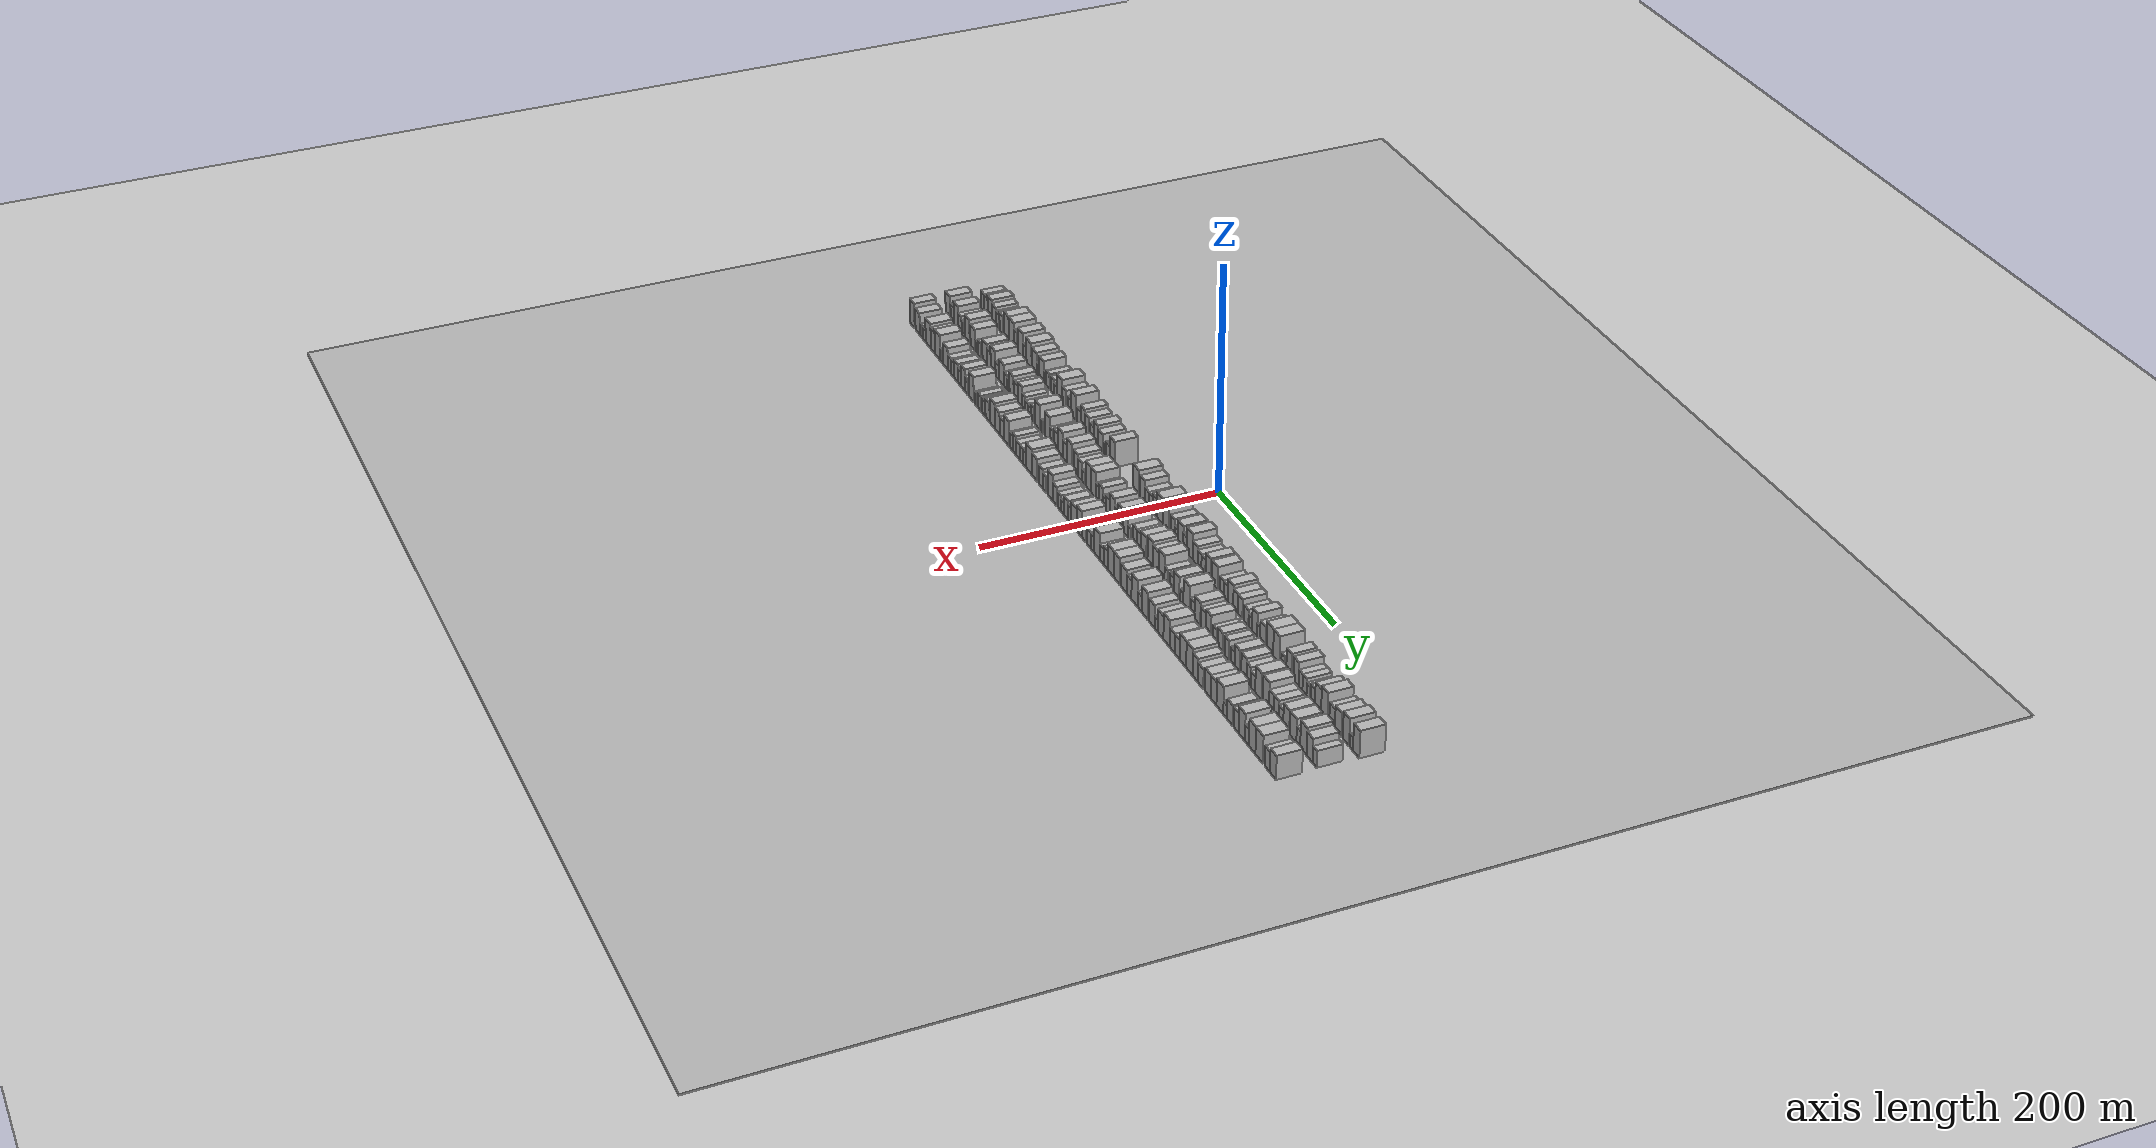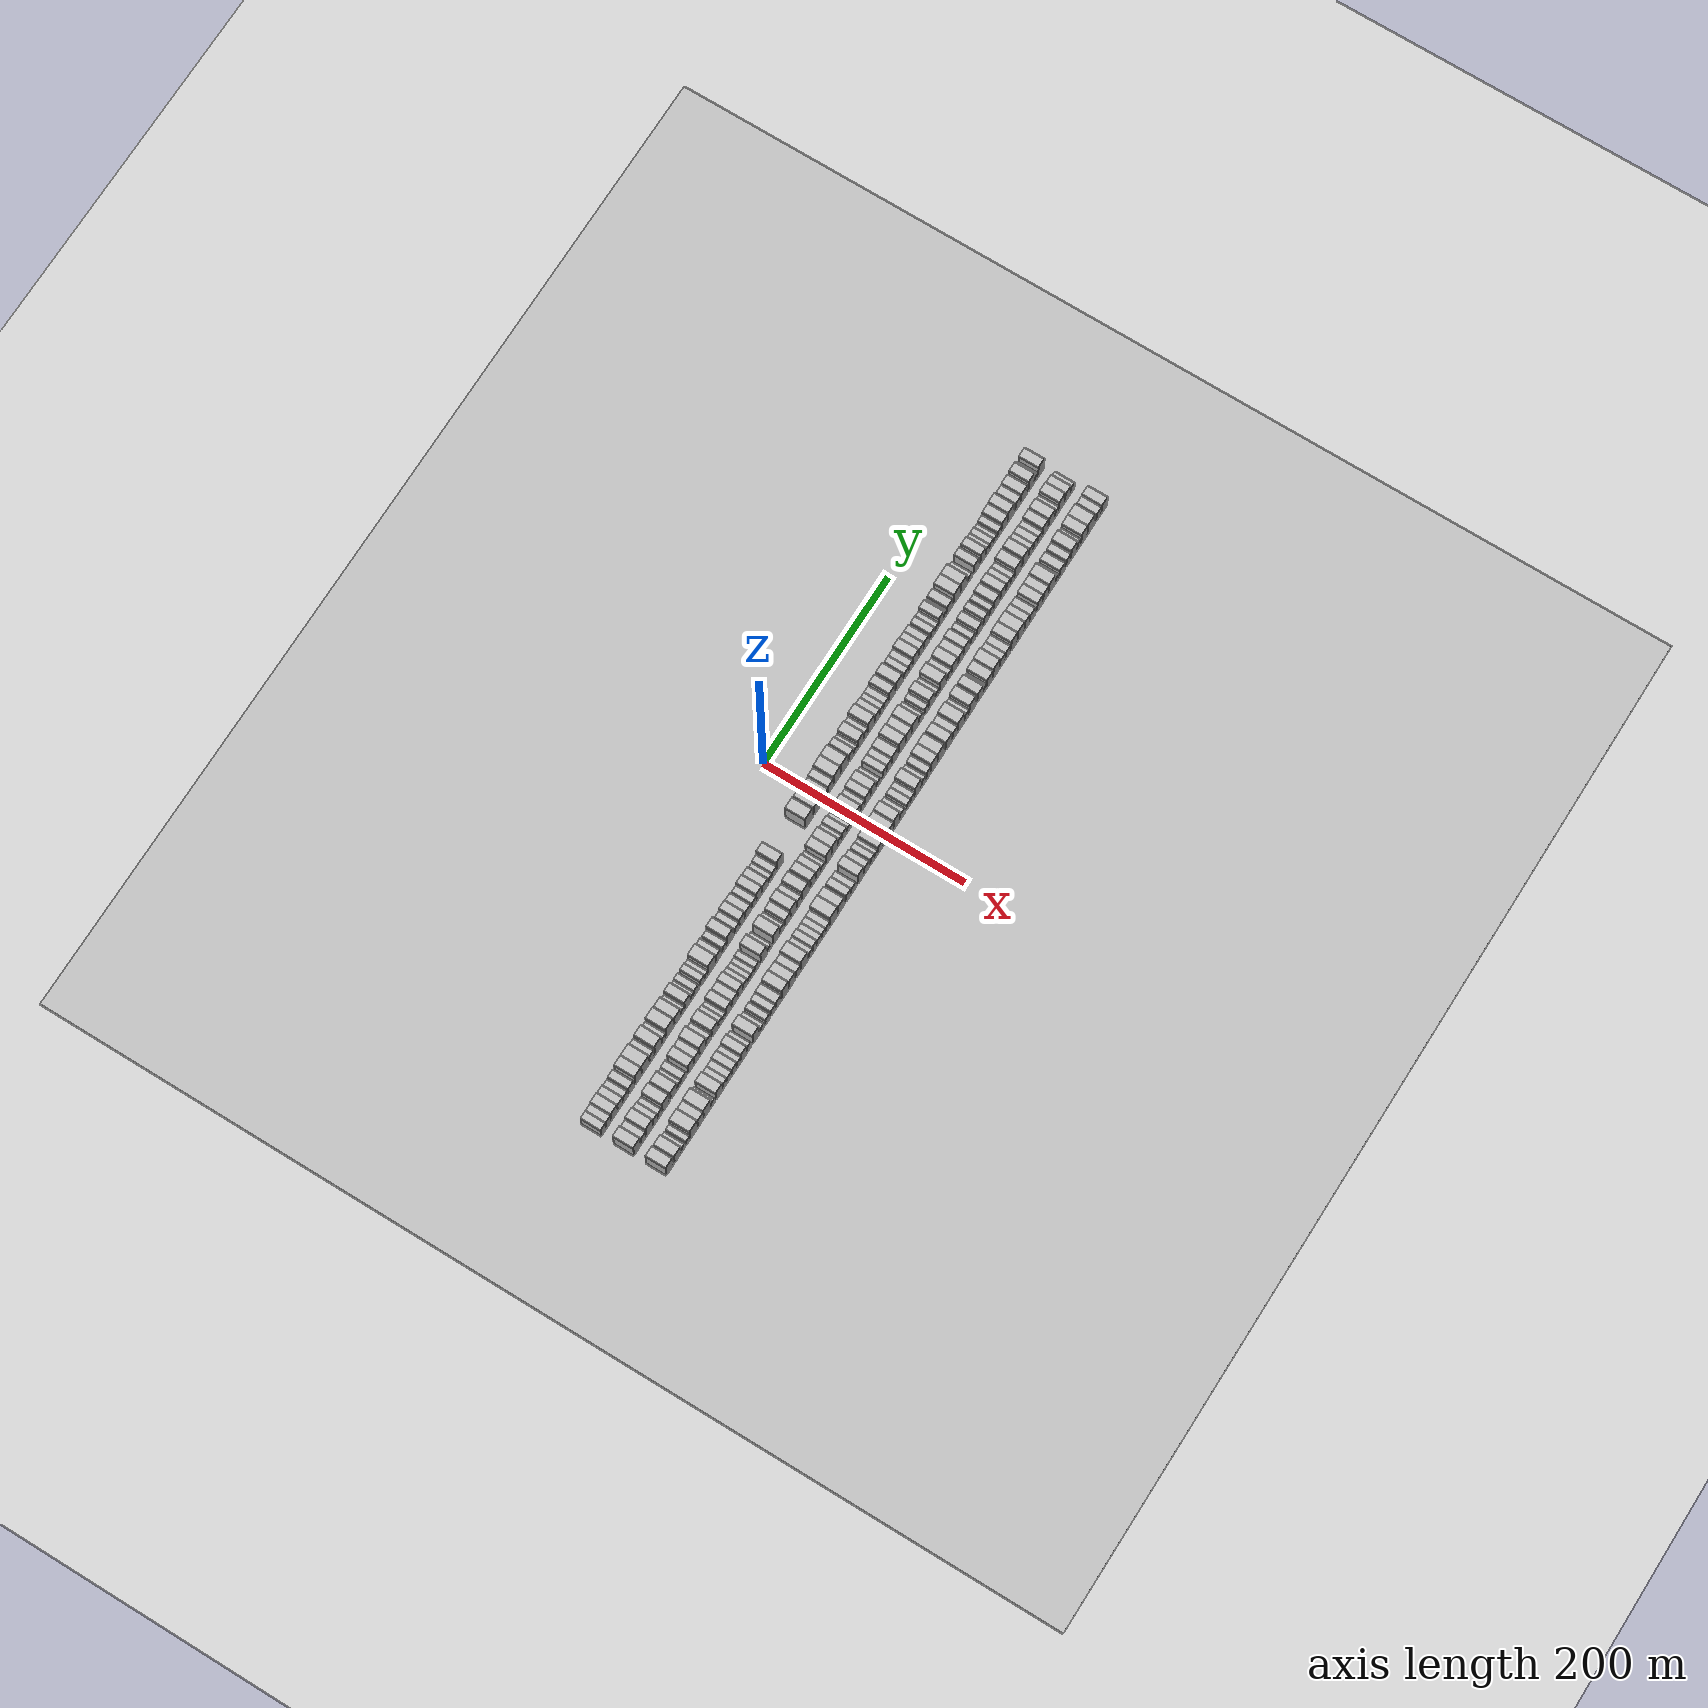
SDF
<?xml version="1.0" encoding="utf-8"?>

<sdf version="1.6">

   <world name="default">

      <gui fullscreen="0">

         <camera name="user_camera">

            <pose>-15 0 4.57585 0 0 0</pose>

            <view_controller>orbit</view_controller>

         </camera>

      </gui>

      <scene>

         <sky>

           <clouds>

             <speed>12</speed>

           </clouds>

         </sky>

         <ambient>0.4 0.4 0.4 1</ambient>

         <background>0.7 0.7 0.7 1</background>

         <shadows>1</shadows>

      </scene>

      <gravity>0 0 -9.8066</gravity>

      <magnetic_field>6e-06 2.3e-05 -4.2e-05</magnetic_field>

      <physics default="0" name="default_physics" type="ode">

         <ode>

            <solver>

               <type>quick</type>

               <iters>10</iters>

               <sor>1.0</sor>

               <use_dynamic_moi_rescaling>0</use_dynamic_moi_rescaling>

            </solver>

            <constraints>

               <cfm>0</cfm>

               <erp>0.2</erp>

               <contact_max_correcting_vel>100</contact_max_correcting_vel>

               <contact_surface_layer>0.001</contact_surface_layer>

            </constraints>

         </ode>

         <max_step_size>0.004</max_step_size>

         <real_time_factor>1</real_time_factor>

         <real_time_update_rate>250</real_time_update_rate>

      </physics>

      <light name="sun" type="directional">

         <cast_shadows>1</cast_shadows>

         <pose>0 0 10 0 0 0</pose>

         <diffuse>0.8 0.8 0.8 1</diffuse>

         <specular>0.2 0.2 0.2 1</specular>

         <attenuation>

            <range>1000</range>

            <constant>0.9</constant>

            <linear>0.01</linear>

            <quadratic>0.001</quadratic>

         </attenuation>

         <direction>-0.5 0.1 -0.9</direction>

      </light>

      <include>

         <name>ground_plane_1</name>

         <uri>model://HANNAS_ground_plane</uri>

         <pose>0 0 0  0 0 0</pose>

      </include>

      <include>

         <name>ground_plane_2</name>

         <uri>model://HANNAS_ground_plane</uri>

         <pose>100 0 0  0 0 0</pose>

      </include>

      <model name="building_1">

         <static>1</static>

         <pose frame="">50.0000 -344.0926 0 0.000000 0.000000 0.000000</pose>

         <link name="link">

            <pose frame="">0 0 9.00 0 0 0</pose>

            <collision name="collision">

               <geometry>

                  <box>

                     <size>20.0000 7.8148 18.0000</size>

                  </box>

               </geometry>

               <max_contacts>10</max_contacts>

               <surface>

                  <contact>

                     <ode/>

                  </contact>

                  <bounce/>

                  <friction>

                     <torsional>

                        <ode/>

                     </torsional>

                     <ode/>

                  </friction>

               </surface>

            </collision>

            <visual name="visual">

               <cast_shadows>0</cast_shadows>

               <geometry>

                  <box>

                     <size>20.0000 7.8148 18.0000</size>

                  </box>

               </geometry>

               <material>

                  <script>

                     <uri>model://HANNAS_wall/materials/scripts</uri>

                     <uri>model://HANNAS_wall/materials/textures</uri>

                     <name>vrc/HANNAS_wall</name>

                  </script>

               </material>

            </visual>

            <self_collide>0</self_collide>

            <enable_wind>0</enable_wind>

            <kinematic>0</kinematic>

         </link>

      </model>

      <model name="building_2">

         <static>1</static>

         <pose frame="">50.0000 -336.4454 0 0.000000 0.000000 0.000000</pose>

         <link name="link">

            <pose frame="">0 0 9.00 0 0 0</pose>

            <collision name="collision">

               <geometry>

                  <box>

                     <size>20.0000 7.4797 18.0000</size>

                  </box>

               </geometry>

               <max_contacts>10</max_contacts>

               <surface>

                  <contact>

                     <ode/>

                  </contact>

                  <bounce/>

                  <friction>

                     <torsional>

                        <ode/>

                     </torsional>

                     <ode/>

                  </friction>

               </surface>

            </collision>

            <visual name="visual">

               <cast_shadows>0</cast_shadows>

               <geometry>

                  <box>

                     <size>20.0000 7.4797 18.0000</size>

                  </box>

               </geometry>

               <material>

                  <script>

                     <uri>model://HANNAS_wall/materials/scripts</uri>

                     <uri>model://HANNAS_wall/materials/textures</uri>

                     <name>vrc/HANNAS_wall</name>

                  </script>

               </material>

            </visual>

            <self_collide>0</self_collide>

            <enable_wind>0</enable_wind>

            <kinematic>0</kinematic>

         </link>

      </model>

      <model name="building_3">

         <static>1</static>

         <pose frame="">50.0000 -327.8060 0 0.000000 0.000000 0.000000</pose>

         <link name="link">

            <pose frame="">0 0 10.50 0 0 0</pose>

            <collision name="collision">

               <geometry>

                  <box>

                     <size>20.0000 9.7990 21.0000</size>

                  </box>

               </geometry>

               <max_contacts>10</max_contacts>

               <surface>

                  <contact>

                     <ode/>

                  </contact>

                  <bounce/>

                  <friction>

                     <torsional>

                        <ode/>

                     </torsional>

                     <ode/>

                  </friction>

               </surface>

            </collision>

            <visual name="visual">

               <cast_shadows>0</cast_shadows>

               <geometry>

                  <box>

                     <size>20.0000 9.7990 21.0000</size>

                  </box>

               </geometry>

               <material>

                  <script>

                     <uri>model://HANNAS_wall/materials/scripts</uri>

                     <uri>model://HANNAS_wall/materials/textures</uri>

                     <name>vrc/HANNAS_wall</name>

                  </script>

               </material>

            </visual>

            <self_collide>0</self_collide>

            <enable_wind>0</enable_wind>

            <kinematic>0</kinematic>

         </link>

      </model>

      <model name="building_4">

         <static>1</static>

         <pose frame="">50.0000 -318.6539 0 0.000000 0.000000 0.000000</pose>

         <link name="link">

            <pose frame="">0 0 9.00 0 0 0</pose>

            <collision name="collision">

               <geometry>

                  <box>

                     <size>20.0000 8.5051 18.0000</size>

                  </box>

               </geometry>

               <max_contacts>10</max_contacts>

               <surface>

                  <contact>

                     <ode/>

                  </contact>

                  <bounce/>

                  <friction>

                     <torsional>

                        <ode/>

                     </torsional>

                     <ode/>

                  </friction>

               </surface>

            </collision>

            <visual name="visual">

               <cast_shadows>0</cast_shadows>

               <geometry>

                  <box>

                     <size>20.0000 8.5051 18.0000</size>

                  </box>

               </geometry>

               <material>

                  <script>

                     <uri>model://HANNAS_wall/materials/scripts</uri>

                     <uri>model://HANNAS_wall/materials/textures</uri>

                     <name>vrc/HANNAS_wall</name>

                  </script>

               </material>

            </visual>

            <self_collide>0</self_collide>

            <enable_wind>0</enable_wind>

            <kinematic>0</kinematic>

         </link>

      </model>

      <model name="building_5">

         <static>1</static>

         <pose frame="">50.0000 -310.8094 0 0.000000 0.000000 0.000000</pose>

         <link name="link">

            <pose frame="">0 0 7.50 0 0 0</pose>

            <collision name="collision">

               <geometry>

                  <box>

                     <size>20.0000 7.1840 15.0000</size>

                  </box>

               </geometry>

               <max_contacts>10</max_contacts>

               <surface>

                  <contact>

                     <ode/>

                  </contact>

                  <bounce/>

                  <friction>

                     <torsional>

                        <ode/>

                     </torsional>

                     <ode/>

                  </friction>

               </surface>

            </collision>

            <visual name="visual">

               <cast_shadows>0</cast_shadows>

               <geometry>

                  <box>

                     <size>20.0000 7.1840 15.0000</size>

                  </box>

               </geometry>

               <material>

                  <script>

                     <uri>model://HANNAS_wall/materials/scripts</uri>

                     <uri>model://HANNAS_wall/materials/textures</uri>

                     <name>vrc/HANNAS_wall</name>

                  </script>

               </material>

            </visual>

            <self_collide>0</self_collide>

            <enable_wind>0</enable_wind>

            <kinematic>0</kinematic>

         </link>

      </model>

      <model name="building_6">

         <static>1</static>

         <pose frame="">50.0000 -302.1716 0 0.000000 0.000000 0.000000</pose>

         <link name="link">

            <pose frame="">0 0 9.00 0 0 0</pose>

            <collision name="collision">

               <geometry>

                  <box>

                     <size>20.0000 8.0914 18.0000</size>

                  </box>

               </geometry>

               <max_contacts>10</max_contacts>

               <surface>

                  <contact>

                     <ode/>

                  </contact>

                  <bounce/>

                  <friction>

                     <torsional>

                        <ode/>

                     </torsional>

                     <ode/>

                  </friction>

               </surface>

            </collision>

            <visual name="visual">

               <cast_shadows>0</cast_shadows>

               <geometry>

                  <box>

                     <size>20.0000 8.0914 18.0000</size>

                  </box>

               </geometry>

               <material>

                  <script>

                     <uri>model://HANNAS_wall/materials/scripts</uri>

                     <uri>model://HANNAS_wall/materials/textures</uri>

                     <name>vrc/HANNAS_wall</name>

                  </script>

               </material>

            </visual>

            <self_collide>0</self_collide>

            <enable_wind>0</enable_wind>

            <kinematic>0</kinematic>

         </link>

      </model>

      <model name="building_7">

         <static>1</static>

         <pose frame="">50.0000 -291.0364 0 0.000000 0.000000 0.000000</pose>

         <link name="link">

            <pose frame="">0 0 12.00 0 0 0</pose>

            <collision name="collision">

               <geometry>

                  <box>

                     <size>20.0000 10.1791 24.0000</size>

                  </box>

               </geometry>

               <max_contacts>10</max_contacts>

               <surface>

                  <contact>

                     <ode/>

                  </contact>

                  <bounce/>

                  <friction>

                     <torsional>

                        <ode/>

                     </torsional>

                     <ode/>

                  </friction>

               </surface>

            </collision>

            <visual name="visual">

               <cast_shadows>0</cast_shadows>

               <geometry>

                  <box>

                     <size>20.0000 10.1791 24.0000</size>

                  </box>

               </geometry>

               <material>

                  <script>

                     <uri>model://HANNAS_wall/materials/scripts</uri>

                     <uri>model://HANNAS_wall/materials/textures</uri>

                     <name>vrc/HANNAS_wall</name>

                  </script>

               </material>

            </visual>

            <self_collide>0</self_collide>

            <enable_wind>0</enable_wind>

            <kinematic>0</kinematic>

         </link>

      </model>

      <model name="building_8">

         <static>1</static>

         <pose frame="">50.0000 -279.9908 0 0.000000 0.000000 0.000000</pose>

         <link name="link">

            <pose frame="">0 0 12.00 0 0 0</pose>

            <collision name="collision">

               <geometry>

                  <box>

                     <size>20.0000 11.9121 24.0000</size>

                  </box>

               </geometry>

               <max_contacts>10</max_contacts>

               <surface>

                  <contact>

                     <ode/>

                  </contact>

                  <bounce/>

                  <friction>

                     <torsional>

                        <ode/>

                     </torsional>

                     <ode/>

                  </friction>

               </surface>

            </collision>

            <visual name="visual">

               <cast_shadows>0</cast_shadows>

               <geometry>

                  <box>

                     <size>20.0000 11.9121 24.0000</size>

                  </box>

               </geometry>

               <material>

                  <script>

                     <uri>model://HANNAS_wall/materials/scripts</uri>

                     <uri>model://HANNAS_wall/materials/textures</uri>

                     <name>vrc/HANNAS_wall</name>

                  </script>

               </material>

            </visual>

            <self_collide>0</self_collide>

            <enable_wind>0</enable_wind>

            <kinematic>0</kinematic>

         </link>

      </model>

      <model name="building_9">

         <static>1</static>

         <pose frame="">50.0000 -270.4188 0 0.000000 0.000000 0.000000</pose>

         <link name="link">

            <pose frame="">0 0 9.00 0 0 0</pose>

            <collision name="collision">

               <geometry>

                  <box>

                     <size>20.0000 7.2318 18.0000</size>

                  </box>

               </geometry>

               <max_contacts>10</max_contacts>

               <surface>

                  <contact>

                     <ode/>

                  </contact>

                  <bounce/>

                  <friction>

                     <torsional>

                        <ode/>

                     </torsional>

                     <ode/>

                  </friction>

               </surface>

            </collision>

            <visual name="visual">

               <cast_shadows>0</cast_shadows>

               <geometry>

                  <box>

                     <size>20.0000 7.2318 18.0000</size>

                  </box>

               </geometry>

               <material>

                  <script>

                     <uri>model://HANNAS_wall/materials/scripts</uri>

                     <uri>model://HANNAS_wall/materials/textures</uri>

                     <name>vrc/HANNAS_wall</name>

                  </script>

               </material>

            </visual>

            <self_collide>0</self_collide>

            <enable_wind>0</enable_wind>

            <kinematic>0</kinematic>

         </link>

      </model>

      <model name="building_10">

         <static>1</static>

         <pose frame="">50.0000 -260.4068 0 0.000000 0.000000 0.000000</pose>

         <link name="link">

            <pose frame="">0 0 12.00 0 0 0</pose>

            <collision name="collision">

               <geometry>

                  <box>

                     <size>20.0000 10.7923 24.0000</size>

                  </box>

               </geometry>

               <max_contacts>10</max_contacts>

               <surface>

                  <contact>

                     <ode/>

                  </contact>

                  <bounce/>

                  <friction>

                     <torsional>

                        <ode/>

                     </torsional>

                     <ode/>

                  </friction>

               </surface>

            </collision>

            <visual name="visual">

               <cast_shadows>0</cast_shadows>

               <geometry>

                  <box>

                     <size>20.0000 10.7923 24.0000</size>

                  </box>

               </geometry>

               <material>

                  <script>

                     <uri>model://HANNAS_wall/materials/scripts</uri>

                     <uri>model://HANNAS_wall/materials/textures</uri>

                     <name>vrc/HANNAS_wall</name>

                  </script>

               </material>

            </visual>

            <self_collide>0</self_collide>

            <enable_wind>0</enable_wind>

            <kinematic>0</kinematic>

         </link>

      </model>

      <model name="building_11">

         <static>1</static>

         <pose frame="">50.0000 -251.6411 0 0.000000 0.000000 0.000000</pose>

         <link name="link">

            <pose frame="">0 0 7.50 0 0 0</pose>

            <collision name="collision">

               <geometry>

                  <box>

                     <size>20.0000 6.7391 15.0000</size>

                  </box>

               </geometry>

               <max_contacts>10</max_contacts>

               <surface>

                  <contact>

                     <ode/>

                  </contact>

                  <bounce/>

                  <friction>

                     <torsional>

                        <ode/>

                     </torsional>

                     <ode/>

                  </friction>

               </surface>

            </collision>

            <visual name="visual">

               <cast_shadows>0</cast_shadows>

               <geometry>

                  <box>

                     <size>20.0000 6.7391 15.0000</size>

                  </box>

               </geometry>

               <material>

                  <script>

                     <uri>model://HANNAS_wall/materials/scripts</uri>

                     <uri>model://HANNAS_wall/materials/textures</uri>

                     <name>vrc/HANNAS_wall</name>

                  </script>

               </material>

            </visual>

            <self_collide>0</self_collide>

            <enable_wind>0</enable_wind>

            <kinematic>0</kinematic>

         </link>

      </model>

      <model name="building_12">

         <static>1</static>

         <pose frame="">50.0000 -242.3853 0 0.000000 0.000000 0.000000</pose>

         <link name="link">

            <pose frame="">0 0 12.00 0 0 0</pose>

            <collision name="collision">

               <geometry>

                  <box>

                     <size>20.0000 11.7725 24.0000</size>

                  </box>

               </geometry>

               <max_contacts>10</max_contacts>

               <surface>

                  <contact>

                     <ode/>

                  </contact>

                  <bounce/>

                  <friction>

                     <torsional>

                        <ode/>

                     </torsional>

                     <ode/>

                  </friction>

               </surface>

            </collision>

            <visual name="visual">

               <cast_shadows>0</cast_shadows>

               <geometry>

                  <box>

                     <size>20.0000 11.7725 24.0000</size>

                  </box>

               </geometry>

               <material>

                  <script>

                     <uri>model://HANNAS_wall/materials/scripts</uri>

                     <uri>model://HANNAS_wall/materials/textures</uri>

                     <name>vrc/HANNAS_wall</name>

                  </script>

               </material>

            </visual>

            <self_collide>0</self_collide>

            <enable_wind>0</enable_wind>

            <kinematic>0</kinematic>

         </link>

      </model>

      <model name="building_13">

         <static>1</static>

         <pose frame="">50.0000 -230.5434 0 0.000000 0.000000 0.000000</pose>

         <link name="link">

            <pose frame="">0 0 10.50 0 0 0</pose>

            <collision name="collision">

               <geometry>

                  <box>

                     <size>20.0000 9.9112 21.0000</size>

                  </box>

               </geometry>

               <max_contacts>10</max_contacts>

               <surface>

                  <contact>

                     <ode/>

                  </contact>

                  <bounce/>

                  <friction>

                     <torsional>

                        <ode/>

                     </torsional>

                     <ode/>

                  </friction>

               </surface>

            </collision>

            <visual name="visual">

               <cast_shadows>0</cast_shadows>

               <geometry>

                  <box>

                     <size>20.0000 9.9112 21.0000</size>

                  </box>

               </geometry>

               <material>

                  <script>

                     <uri>model://HANNAS_wall/materials/scripts</uri>

                     <uri>model://HANNAS_wall/materials/textures</uri>

                     <name>vrc/HANNAS_wall</name>

                  </script>

               </material>

            </visual>

            <self_collide>0</self_collide>

            <enable_wind>0</enable_wind>

            <kinematic>0</kinematic>

         </link>

      </model>

      <model name="building_14">

         <static>1</static>

         <pose frame="">50.0000 -222.6430 0 0.000000 0.000000 0.000000</pose>

         <link name="link">

            <pose frame="">0 0 6.00 0 0 0</pose>

            <collision name="collision">

               <geometry>

                  <box>

                     <size>20.0000 5.8896 12.0000</size>

                  </box>

               </geometry>

               <max_contacts>10</max_contacts>

               <surface>

                  <contact>

                     <ode/>

                  </contact>

                  <bounce/>

                  <friction>

                     <torsional>

                        <ode/>

                     </torsional>

                     <ode/>

                  </friction>

               </surface>

            </collision>

            <visual name="visual">

               <cast_shadows>0</cast_shadows>

               <geometry>

                  <box>

                     <size>20.0000 5.8896 12.0000</size>

                  </box>

               </geometry>

               <material>

                  <script>

                     <uri>model://HANNAS_wall/materials/scripts</uri>

                     <uri>model://HANNAS_wall/materials/textures</uri>

                     <name>vrc/HANNAS_wall</name>

                  </script>

               </material>

            </visual>

            <self_collide>0</self_collide>

            <enable_wind>0</enable_wind>

            <kinematic>0</kinematic>

         </link>

      </model>

      <model name="building_15">

         <static>1</static>

         <pose frame="">50.0000 -215.0859 0 0.000000 0.000000 0.000000</pose>

         <link name="link">

            <pose frame="">0 0 10.50 0 0 0</pose>

            <collision name="collision">

               <geometry>

                  <box>

                     <size>20.0000 9.2246 21.0000</size>

                  </box>

               </geometry>

               <max_contacts>10</max_contacts>

               <surface>

                  <contact>

                     <ode/>

                  </contact>

                  <bounce/>

                  <friction>

                     <torsional>

                        <ode/>

                     </torsional>

                     <ode/>

                  </friction>

               </surface>

            </collision>

            <visual name="visual">

               <cast_shadows>0</cast_shadows>

               <geometry>

                  <box>

                     <size>20.0000 9.2246 21.0000</size>

                  </box>

               </geometry>

               <material>

                  <script>

                     <uri>model://HANNAS_wall/materials/scripts</uri>

                     <uri>model://HANNAS_wall/materials/textures</uri>

                     <name>vrc/HANNAS_wall</name>

                  </script>

               </material>

            </visual>

            <self_collide>0</self_collide>

            <enable_wind>0</enable_wind>

            <kinematic>0</kinematic>

         </link>

      </model>

      <model name="building_16">

         <static>1</static>

         <pose frame="">50.0000 -207.7414 0 0.000000 0.000000 0.000000</pose>

         <link name="link">

            <pose frame="">0 0 6.00 0 0 0</pose>

            <collision name="collision">

               <geometry>

                  <box>

                     <size>20.0000 5.4645 12.0000</size>

                  </box>

               </geometry>

               <max_contacts>10</max_contacts>

               <surface>

                  <contact>

                     <ode/>

                  </contact>

                  <bounce/>

                  <friction>

                     <torsional>

                        <ode/>

                     </torsional>

                     <ode/>

                  </friction>

               </surface>

            </collision>

            <visual name="visual">

               <cast_shadows>0</cast_shadows>

               <geometry>

                  <box>

                     <size>20.0000 5.4645 12.0000</size>

                  </box>

               </geometry>

               <material>

                  <script>

                     <uri>model://HANNAS_wall/materials/scripts</uri>

                     <uri>model://HANNAS_wall/materials/textures</uri>

                     <name>vrc/HANNAS_wall</name>

                  </script>

               </material>

            </visual>

            <self_collide>0</self_collide>

            <enable_wind>0</enable_wind>

            <kinematic>0</kinematic>

         </link>

      </model>

      <model name="building_17">

         <static>1</static>

         <pose frame="">50.0000 -201.7079 0 0.000000 0.000000 0.000000</pose>

         <link name="link">

            <pose frame="">0 0 7.50 0 0 0</pose>

            <collision name="collision">

               <geometry>

                  <box>

                     <size>20.0000 6.6024 15.0000</size>

                  </box>

               </geometry>

               <max_contacts>10</max_contacts>

               <surface>

                  <contact>

                     <ode/>

                  </contact>

                  <bounce/>

                  <friction>

                     <torsional>

                        <ode/>

                     </torsional>

                     <ode/>

                  </friction>

               </surface>

            </collision>

            <visual name="visual">

               <cast_shadows>0</cast_shadows>

               <geometry>

                  <box>

                     <size>20.0000 6.6024 15.0000</size>

                  </box>

               </geometry>

               <material>

                  <script>

                     <uri>model://HANNAS_wall/materials/scripts</uri>

                     <uri>model://HANNAS_wall/materials/textures</uri>

                     <name>vrc/HANNAS_wall</name>

                  </script>

               </material>

            </visual>

            <self_collide>0</self_collide>

            <enable_wind>0</enable_wind>

            <kinematic>0</kinematic>

         </link>

      </model>

      <model name="building_18">

         <static>1</static>

         <pose frame="">50.0000 -191.9863 0 0.000000 0.000000 0.000000</pose>

         <link name="link">

            <pose frame="">0 0 7.50 0 0 0</pose>

            <collision name="collision">

               <geometry>

                  <box>

                     <size>20.0000 6.8409 15.0000</size>

                  </box>

               </geometry>

               <max_contacts>10</max_contacts>

               <surface>

                  <contact>

                     <ode/>

                  </contact>

                  <bounce/>

                  <friction>

                     <torsional>

                        <ode/>

                     </torsional>

                     <ode/>

                  </friction>

               </surface>

            </collision>

            <visual name="visual">

               <cast_shadows>0</cast_shadows>

               <geometry>

                  <box>

                     <size>20.0000 6.8409 15.0000</size>

                  </box>

               </geometry>

               <material>

                  <script>

                     <uri>model://HANNAS_wall/materials/scripts</uri>

                     <uri>model://HANNAS_wall/materials/textures</uri>

                     <name>vrc/HANNAS_wall</name>

                  </script>

               </material>

            </visual>

            <self_collide>0</self_collide>

            <enable_wind>0</enable_wind>

            <kinematic>0</kinematic>

         </link>

      </model>

      <model name="building_19">

         <static>1</static>

         <pose frame="">50.0000 -185.9158 0 0.000000 0.000000 0.000000</pose>

         <link name="link">

            <pose frame="">0 0 6.00 0 0 0</pose>

            <collision name="collision">

               <geometry>

                  <box>

                     <size>20.0000 5.3001 12.0000</size>

                  </box>

               </geometry>

               <max_contacts>10</max_contacts>

               <surface>

                  <contact>

                     <ode/>

                  </contact>

                  <bounce/>

                  <friction>

                     <torsional>

                        <ode/>

                     </torsional>

                     <ode/>

                  </friction>

               </surface>

            </collision>

            <visual name="visual">

               <cast_shadows>0</cast_shadows>

               <geometry>

                  <box>

                     <size>20.0000 5.3001 12.0000</size>

                  </box>

               </geometry>

               <material>

                  <script>

                     <uri>model://HANNAS_wall/materials/scripts</uri>

                     <uri>model://HANNAS_wall/materials/textures</uri>

                     <name>vrc/HANNAS_wall</name>

                  </script>

               </material>

            </visual>

            <self_collide>0</self_collide>

            <enable_wind>0</enable_wind>

            <kinematic>0</kinematic>

         </link>

      </model>

      <model name="building_20">

         <static>1</static>

         <pose frame="">50.0000 -177.3559 0 0.000000 0.000000 0.000000</pose>

         <link name="link">

            <pose frame="">0 0 12.00 0 0 0</pose>

            <collision name="collision">

               <geometry>

                  <box>

                     <size>20.0000 11.8196 24.0000</size>

                  </box>

               </geometry>

               <max_contacts>10</max_contacts>

               <surface>

                  <contact>

                     <ode/>

                  </contact>

                  <bounce/>

                  <friction>

                     <torsional>

                        <ode/>

                     </torsional>

                     <ode/>

                  </friction>

               </surface>

            </collision>

            <visual name="visual">

               <cast_shadows>0</cast_shadows>

               <geometry>

                  <box>

                     <size>20.0000 11.8196 24.0000</size>

                  </box>

               </geometry>

               <material>

                  <script>

                     <uri>model://HANNAS_wall/materials/scripts</uri>

                     <uri>model://HANNAS_wall/materials/textures</uri>

                     <name>vrc/HANNAS_wall</name>

                  </script>

               </material>

            </visual>

            <self_collide>0</self_collide>

            <enable_wind>0</enable_wind>

            <kinematic>0</kinematic>

         </link>

      </model>

      <model name="building_21">

         <static>1</static>

         <pose frame="">50.0000 -167.6378 0 0.000000 0.000000 0.000000</pose>

         <link name="link">

            <pose frame="">0 0 9.00 0 0 0</pose>

            <collision name="collision">

               <geometry>

                  <box>

                     <size>20.0000 7.6166 18.0000</size>

                  </box>

               </geometry>

               <max_contacts>10</max_contacts>

               <surface>

                  <contact>

                     <ode/>

                  </contact>

                  <bounce/>

                  <friction>

                     <torsional>

                        <ode/>

                     </torsional>

                     <ode/>

                  </friction>

               </surface>

            </collision>

            <visual name="visual">

               <cast_shadows>0</cast_shadows>

               <geometry>

                  <box>

                     <size>20.0000 7.6166 18.0000</size>

                  </box>

               </geometry>

               <material>

                  <script>

                     <uri>model://HANNAS_wall/materials/scripts</uri>

                     <uri>model://HANNAS_wall/materials/textures</uri>

                     <name>vrc/HANNAS_wall</name>

                  </script>

               </material>

            </visual>

            <self_collide>0</self_collide>

            <enable_wind>0</enable_wind>

            <kinematic>0</kinematic>

         </link>

      </model>

      <model name="building_22">

         <static>1</static>

         <pose frame="">50.0000 -157.4717 0 0.000000 0.000000 0.000000</pose>

         <link name="link">

            <pose frame="">0 0 7.50 0 0 0</pose>

            <collision name="collision">

               <geometry>

                  <box>

                     <size>20.0000 6.7156 15.0000</size>

                  </box>

               </geometry>

               <max_contacts>10</max_contacts>

               <surface>

                  <contact>

                     <ode/>

                  </contact>

                  <bounce/>

                  <friction>

                     <torsional>

                        <ode/>

                     </torsional>

                     <ode/>

                  </friction>

               </surface>

            </collision>

            <visual name="visual">

               <cast_shadows>0</cast_shadows>

               <geometry>

                  <box>

                     <size>20.0000 6.7156 15.0000</size>

                  </box>

               </geometry>

               <material>

                  <script>

                     <uri>model://HANNAS_wall/materials/scripts</uri>

                     <uri>model://HANNAS_wall/materials/textures</uri>

                     <name>vrc/HANNAS_wall</name>

                  </script>

               </material>

            </visual>

            <self_collide>0</self_collide>

            <enable_wind>0</enable_wind>

            <kinematic>0</kinematic>

         </link>

      </model>

      <model name="building_23">

         <static>1</static>

         <pose frame="">50.0000 -149.2440 0 0.000000 0.000000 0.000000</pose>

         <link name="link">

            <pose frame="">0 0 12.00 0 0 0</pose>

            <collision name="collision">

               <geometry>

                  <box>

                     <size>20.0000 9.7397 24.0000</size>

                  </box>

               </geometry>

               <max_contacts>10</max_contacts>

               <surface>

                  <contact>

                     <ode/>

                  </contact>

                  <bounce/>

                  <friction>

                     <torsional>

                        <ode/>

                     </torsional>

                     <ode/>

                  </friction>

               </surface>

            </collision>

            <visual name="visual">

               <cast_shadows>0</cast_shadows>

               <geometry>

                  <box>

                     <size>20.0000 9.7397 24.0000</size>

                  </box>

               </geometry>

               <material>

                  <script>

                     <uri>model://HANNAS_wall/materials/scripts</uri>

                     <uri>model://HANNAS_wall/materials/textures</uri>

                     <name>vrc/HANNAS_wall</name>

                  </script>

               </material>

            </visual>

            <self_collide>0</self_collide>

            <enable_wind>0</enable_wind>

            <kinematic>0</kinematic>

         </link>

      </model>

      <model name="building_24">

         <static>1</static>

         <pose frame="">50.0000 -137.9327 0 0.000000 0.000000 0.000000</pose>

         <link name="link">

            <pose frame="">0 0 7.50 0 0 0</pose>

            <collision name="collision">

               <geometry>

                  <box>

                     <size>20.0000 6.8829 15.0000</size>

                  </box>

               </geometry>

               <max_contacts>10</max_contacts>

               <surface>

                  <contact>

                     <ode/>

                  </contact>

                  <bounce/>

                  <friction>

                     <torsional>

                        <ode/>

                     </torsional>

                     <ode/>

                  </friction>

               </surface>

            </collision>

            <visual name="visual">

               <cast_shadows>0</cast_shadows>

               <geometry>

                  <box>

                     <size>20.0000 6.8829 15.0000</size>

                  </box>

               </geometry>

               <material>

                  <script>

                     <uri>model://HANNAS_wall/materials/scripts</uri>

                     <uri>model://HANNAS_wall/materials/textures</uri>

                     <name>vrc/HANNAS_wall</name>

                  </script>

               </material>

            </visual>

            <self_collide>0</self_collide>

            <enable_wind>0</enable_wind>

            <kinematic>0</kinematic>

         </link>

      </model>

      <model name="building_25">

         <static>1</static>

         <pose frame="">50.0000 -130.1155 0 0.000000 0.000000 0.000000</pose>

         <link name="link">

            <pose frame="">0 0 10.50 0 0 0</pose>

            <collision name="collision">

               <geometry>

                  <box>

                     <size>20.0000 8.7515 21.0000</size>

                  </box>

               </geometry>

               <max_contacts>10</max_contacts>

               <surface>

                  <contact>

                     <ode/>

                  </contact>

                  <bounce/>

                  <friction>

                     <torsional>

                        <ode/>

                     </torsional>

                     <ode/>

                  </friction>

               </surface>

            </collision>

            <visual name="visual">

               <cast_shadows>0</cast_shadows>

               <geometry>

                  <box>

                     <size>20.0000 8.7515 21.0000</size>

                  </box>

               </geometry>

               <material>

                  <script>

                     <uri>model://HANNAS_wall/materials/scripts</uri>

                     <uri>model://HANNAS_wall/materials/textures</uri>

                     <name>vrc/HANNAS_wall</name>

                  </script>

               </material>

            </visual>

            <self_collide>0</self_collide>

            <enable_wind>0</enable_wind>

            <kinematic>0</kinematic>

         </link>

      </model>

      <model name="building_26">

         <static>1</static>

         <pose frame="">50.0000 -121.3373 0 0.000000 0.000000 0.000000</pose>

         <link name="link">

            <pose frame="">0 0 9.00 0 0 0</pose>

            <collision name="collision">

               <geometry>

                  <box>

                     <size>20.0000 8.8049 18.0000</size>

                  </box>

               </geometry>

               <max_contacts>10</max_contacts>

               <surface>

                  <contact>

                     <ode/>

                  </contact>

                  <bounce/>

                  <friction>

                     <torsional>

                        <ode/>

                     </torsional>

                     <ode/>

                  </friction>

               </surface>

            </collision>

            <visual name="visual">

               <cast_shadows>0</cast_shadows>

               <geometry>

                  <box>

                     <size>20.0000 8.8049 18.0000</size>

                  </box>

               </geometry>

               <material>

                  <script>

                     <uri>model://HANNAS_wall/materials/scripts</uri>

                     <uri>model://HANNAS_wall/materials/textures</uri>

                     <name>vrc/HANNAS_wall</name>

                  </script>

               </material>

            </visual>

            <self_collide>0</self_collide>

            <enable_wind>0</enable_wind>

            <kinematic>0</kinematic>

         </link>

      </model>

      <model name="building_27">

         <static>1</static>

         <pose frame="">50.0000 -111.3800 0 0.000000 0.000000 0.000000</pose>

         <link name="link">

            <pose frame="">0 0 7.50 0 0 0</pose>

            <collision name="collision">

               <geometry>

                  <box>

                     <size>20.0000 7.1098 15.0000</size>

                  </box>

               </geometry>

               <max_contacts>10</max_contacts>

               <surface>

                  <contact>

                     <ode/>

                  </contact>

                  <bounce/>

                  <friction>

                     <torsional>

                        <ode/>

                     </torsional>

                     <ode/>

                  </friction>

               </surface>

            </collision>

            <visual name="visual">

               <cast_shadows>0</cast_shadows>

               <geometry>

                  <box>

                     <size>20.0000 7.1098 15.0000</size>

                  </box>

               </geometry>

               <material>

                  <script>

                     <uri>model://HANNAS_wall/materials/scripts</uri>

                     <uri>model://HANNAS_wall/materials/textures</uri>

                     <name>vrc/HANNAS_wall</name>

                  </script>

               </material>

            </visual>

            <self_collide>0</self_collide>

            <enable_wind>0</enable_wind>

            <kinematic>0</kinematic>

         </link>

      </model>

      <model name="building_28">

         <static>1</static>

         <pose frame="">50.0000 -103.3615 0 0.000000 0.000000 0.000000</pose>

         <link name="link">

            <pose frame="">0 0 10.50 0 0 0</pose>

            <collision name="collision">

               <geometry>

                  <box>

                     <size>20.0000 8.9272 21.0000</size>

                  </box>

               </geometry>

               <max_contacts>10</max_contacts>

               <surface>

                  <contact>

                     <ode/>

                  </contact>

                  <bounce/>

                  <friction>

                     <torsional>

                        <ode/>

                     </torsional>

                     <ode/>

                  </friction>

               </surface>

            </collision>

            <visual name="visual">

               <cast_shadows>0</cast_shadows>

               <geometry>

                  <box>

                     <size>20.0000 8.9272 21.0000</size>

                  </box>

               </geometry>

               <material>

                  <script>

                     <uri>model://HANNAS_wall/materials/scripts</uri>

                     <uri>model://HANNAS_wall/materials/textures</uri>

                     <name>vrc/HANNAS_wall</name>

                  </script>

               </material>

            </visual>

            <self_collide>0</self_collide>

            <enable_wind>0</enable_wind>

            <kinematic>0</kinematic>

         </link>

      </model>

      <model name="building_29">

         <static>1</static>

         <pose frame="">50.0000 -94.4564 0 0.000000 0.000000 0.000000</pose>

         <link name="link">

            <pose frame="">0 0 9.00 0 0 0</pose>

            <collision name="collision">

               <geometry>

                  <box>

                     <size>20.0000 8.8831 18.0000</size>

                  </box>

               </geometry>

               <max_contacts>10</max_contacts>

               <surface>

                  <contact>

                     <ode/>

                  </contact>

                  <bounce/>

                  <friction>

                     <torsional>

                        <ode/>

                     </torsional>

                     <ode/>

                  </friction>

               </surface>

            </collision>

            <visual name="visual">

               <cast_shadows>0</cast_shadows>

               <geometry>

                  <box>

                     <size>20.0000 8.8831 18.0000</size>

                  </box>

               </geometry>

               <material>

                  <script>

                     <uri>model://HANNAS_wall/materials/scripts</uri>

                     <uri>model://HANNAS_wall/materials/textures</uri>

                     <name>vrc/HANNAS_wall</name>

                  </script>

               </material>

            </visual>

            <self_collide>0</self_collide>

            <enable_wind>0</enable_wind>

            <kinematic>0</kinematic>

         </link>

      </model>

      <model name="building_30">

         <static>1</static>

         <pose frame="">50.0000 -85.5442 0 0.000000 0.000000 0.000000</pose>

         <link name="link">

            <pose frame="">0 0 6.00 0 0 0</pose>

            <collision name="collision">

               <geometry>

                  <box>

                     <size>20.0000 4.9413 12.0000</size>

                  </box>

               </geometry>

               <max_contacts>10</max_contacts>

               <surface>

                  <contact>

                     <ode/>

                  </contact>

                  <bounce/>

                  <friction>

                     <torsional>

                        <ode/>

                     </torsional>

                     <ode/>

                  </friction>

               </surface>

            </collision>

            <visual name="visual">

               <cast_shadows>0</cast_shadows>

               <geometry>

                  <box>

                     <size>20.0000 4.9413 12.0000</size>

                  </box>

               </geometry>

               <material>

                  <script>

                     <uri>model://HANNAS_wall/materials/scripts</uri>

                     <uri>model://HANNAS_wall/materials/textures</uri>

                     <name>vrc/HANNAS_wall</name>

                  </script>

               </material>

            </visual>

            <self_collide>0</self_collide>

            <enable_wind>0</enable_wind>

            <kinematic>0</kinematic>

         </link>

      </model>

      <model name="building_31">

         <static>1</static>

         <pose frame="">50.0000 -79.5141 0 0.000000 0.000000 0.000000</pose>

         <link name="link">

            <pose frame="">0 0 7.50 0 0 0</pose>

            <collision name="collision">

               <geometry>

                  <box>

                     <size>20.0000 7.1188 15.0000</size>

                  </box>

               </geometry>

               <max_contacts>10</max_contacts>

               <surface>

                  <contact>

                     <ode/>

                  </contact>

                  <bounce/>

                  <friction>

                     <torsional>

                        <ode/>

                     </torsional>

                     <ode/>

                  </friction>

               </surface>

            </collision>

            <visual name="visual">

               <cast_shadows>0</cast_shadows>

               <geometry>

                  <box>

                     <size>20.0000 7.1188 15.0000</size>

                  </box>

               </geometry>

               <material>

                  <script>

                     <uri>model://HANNAS_wall/materials/scripts</uri>

                     <uri>model://HANNAS_wall/materials/textures</uri>

                     <name>vrc/HANNAS_wall</name>

                  </script>

               </material>

            </visual>

            <self_collide>0</self_collide>

            <enable_wind>0</enable_wind>

            <kinematic>0</kinematic>

         </link>

      </model>

      <model name="building_32">

         <static>1</static>

         <pose frame="">50.0000 -71.0748 0 0.000000 0.000000 0.000000</pose>

         <link name="link">

            <pose frame="">0 0 12.00 0 0 0</pose>

            <collision name="collision">

               <geometry>

                  <box>

                     <size>20.0000 9.7599 24.0000</size>

                  </box>

               </geometry>

               <max_contacts>10</max_contacts>

               <surface>

                  <contact>

                     <ode/>

                  </contact>

                  <bounce/>

                  <friction>

                     <torsional>

                        <ode/>

                     </torsional>

                     <ode/>

                  </friction>

               </surface>

            </collision>

            <visual name="visual">

               <cast_shadows>0</cast_shadows>

               <geometry>

                  <box>

                     <size>20.0000 9.7599 24.0000</size>

                  </box>

               </geometry>

               <material>

                  <script>

                     <uri>model://HANNAS_wall/materials/scripts</uri>

                     <uri>model://HANNAS_wall/materials/textures</uri>

                     <name>vrc/HANNAS_wall</name>

                  </script>

               </material>

            </visual>

            <self_collide>0</self_collide>

            <enable_wind>0</enable_wind>

            <kinematic>0</kinematic>

         </link>

      </model>

      <model name="building_33">

         <static>1</static>

         <pose frame="">50.0000 -25.0586 0 0.000000 0.000000 0.000000</pose>

         <link name="link">

            <pose frame="">0 0 12.00 0 0 0</pose>

            <collision name="collision">

               <geometry>

                  <box>

                     <size>20.0000 11.4242 24.0000</size>

                  </box>

               </geometry>

               <max_contacts>10</max_contacts>

               <surface>

                  <contact>

                     <ode/>

                  </contact>

                  <bounce/>

                  <friction>

                     <torsional>

                        <ode/>

                     </torsional>

                     <ode/>

                  </friction>

               </surface>

            </collision>

            <visual name="visual">

               <cast_shadows>0</cast_shadows>

               <geometry>

                  <box>

                     <size>20.0000 11.4242 24.0000</size>

                  </box>

               </geometry>

               <material>

                  <script>

                     <uri>model://HANNAS_wall/materials/scripts</uri>

                     <uri>model://HANNAS_wall/materials/textures</uri>

                     <name>vrc/HANNAS_wall</name>

                  </script>

               </material>

            </visual>

            <self_collide>0</self_collide>

            <enable_wind>0</enable_wind>

            <kinematic>0</kinematic>

         </link>

      </model>

      <model name="building_34">

         <static>1</static>

         <pose frame="">50.0000 -12.9446 0 0.000000 0.000000 0.000000</pose>

         <link name="link">

            <pose frame="">0 0 10.50 0 0 0</pose>

            <collision name="collision">

               <geometry>

                  <box>

                     <size>20.0000 8.8038 21.0000</size>

                  </box>

               </geometry>

               <max_contacts>10</max_contacts>

               <surface>

                  <contact>

                     <ode/>

                  </contact>

                  <bounce/>

                  <friction>

                     <torsional>

                        <ode/>

                     </torsional>

                     <ode/>

                  </friction>

               </surface>

            </collision>

            <visual name="visual">

               <cast_shadows>0</cast_shadows>

               <geometry>

                  <box>

                     <size>20.0000 8.8038 21.0000</size>

                  </box>

               </geometry>

               <material>

                  <script>

                     <uri>model://HANNAS_wall/materials/scripts</uri>

                     <uri>model://HANNAS_wall/materials/textures</uri>

                     <name>vrc/HANNAS_wall</name>

                  </script>

               </material>

            </visual>

            <self_collide>0</self_collide>

            <enable_wind>0</enable_wind>

            <kinematic>0</kinematic>

         </link>

      </model>

      <model name="building_35">

         <static>1</static>

         <pose frame="">50.0000 -4.8245 0 0.000000 0.000000 0.000000</pose>

         <link name="link">

            <pose frame="">0 0 7.50 0 0 0</pose>

            <collision name="collision">

               <geometry>

                  <box>

                     <size>20.0000 7.4364 15.0000</size>

                  </box>

               </geometry>

               <max_contacts>10</max_contacts>

               <surface>

                  <contact>

                     <ode/>

                  </contact>

                  <bounce/>

                  <friction>

                     <torsional>

                        <ode/>

                     </torsional>

                     <ode/>

                  </friction>

               </surface>

            </collision>

            <visual name="visual">

               <cast_shadows>0</cast_shadows>

               <geometry>

                  <box>

                     <size>20.0000 7.4364 15.0000</size>

                  </box>

               </geometry>

               <material>

                  <script>

                     <uri>model://HANNAS_wall/materials/scripts</uri>

                     <uri>model://HANNAS_wall/materials/textures</uri>

                     <name>vrc/HANNAS_wall</name>

                  </script>

               </material>

            </visual>

            <self_collide>0</self_collide>

            <enable_wind>0</enable_wind>

            <kinematic>0</kinematic>

         </link>

      </model>

      <model name="building_36">

         <static>1</static>

         <pose frame="">50.0000 2.2574 0 0.000000 0.000000 0.000000</pose>

         <link name="link">

            <pose frame="">0 0 7.50 0 0 0</pose>

            <collision name="collision">

               <geometry>

                  <box>

                     <size>20.0000 6.7274 15.0000</size>

                  </box>

               </geometry>

               <max_contacts>10</max_contacts>

               <surface>

                  <contact>

                     <ode/>

                  </contact>

                  <bounce/>

                  <friction>

                     <torsional>

                        <ode/>

                     </torsional>

                     <ode/>

                  </friction>

               </surface>

            </collision>

            <visual name="visual">

               <cast_shadows>0</cast_shadows>

               <geometry>

                  <box>

                     <size>20.0000 6.7274 15.0000</size>

                  </box>

               </geometry>

               <material>

                  <script>

                     <uri>model://HANNAS_wall/materials/scripts</uri>

                     <uri>model://HANNAS_wall/materials/textures</uri>

                     <name>vrc/HANNAS_wall</name>

                  </script>

               </material>

            </visual>

            <self_collide>0</self_collide>

            <enable_wind>0</enable_wind>

            <kinematic>0</kinematic>

         </link>

      </model>

      <model name="building_37">

         <static>1</static>

         <pose frame="">50.0000 9.7576 0 0.000000 0.000000 0.000000</pose>

         <link name="link">

            <pose frame="">0 0 9.00 0 0 0</pose>

            <collision name="collision">

               <geometry>

                  <box>

                     <size>20.0000 8.2731 18.0000</size>

                  </box>

               </geometry>

               <max_contacts>10</max_contacts>

               <surface>

                  <contact>

                     <ode/>

                  </contact>

                  <bounce/>

                  <friction>

                     <torsional>

                        <ode/>

                     </torsional>

                     <ode/>

                  </friction>

               </surface>

            </collision>

            <visual name="visual">

               <cast_shadows>0</cast_shadows>

               <geometry>

                  <box>

                     <size>20.0000 8.2731 18.0000</size>

                  </box>

               </geometry>

               <material>

                  <script>

                     <uri>model://HANNAS_wall/materials/scripts</uri>

                     <uri>model://HANNAS_wall/materials/textures</uri>

                     <name>vrc/HANNAS_wall</name>

                  </script>

               </material>

            </visual>

            <self_collide>0</self_collide>

            <enable_wind>0</enable_wind>

            <kinematic>0</kinematic>

         </link>

      </model>

      <model name="building_38">

         <static>1</static>

         <pose frame="">50.0000 19.5656 0 0.000000 0.000000 0.000000</pose>

         <link name="link">

            <pose frame="">0 0 12.00 0 0 0</pose>

            <collision name="collision">

               <geometry>

                  <box>

                     <size>20.0000 11.3429 24.0000</size>

                  </box>

               </geometry>

               <max_contacts>10</max_contacts>

               <surface>

                  <contact>

                     <ode/>

                  </contact>

                  <bounce/>

                  <friction>

                     <torsional>

                        <ode/>

                     </torsional>

                     <ode/>

                  </friction>

               </surface>

            </collision>

            <visual name="visual">

               <cast_shadows>0</cast_shadows>

               <geometry>

                  <box>

                     <size>20.0000 11.3429 24.0000</size>

                  </box>

               </geometry>

               <material>

                  <script>

                     <uri>model://HANNAS_wall/materials/scripts</uri>

                     <uri>model://HANNAS_wall/materials/textures</uri>

                     <name>vrc/HANNAS_wall</name>

                  </script>

               </material>

            </visual>

            <self_collide>0</self_collide>

            <enable_wind>0</enable_wind>

            <kinematic>0</kinematic>

         </link>

      </model>

      <model name="building_39">

         <static>1</static>

         <pose frame="">50.0000 30.7202 0 0.000000 0.000000 0.000000</pose>

         <link name="link">

            <pose frame="">0 0 12.00 0 0 0</pose>

            <collision name="collision">

               <geometry>

                  <box>

                     <size>20.0000 10.9663 24.0000</size>

                  </box>

               </geometry>

               <max_contacts>10</max_contacts>

               <surface>

                  <contact>

                     <ode/>

                  </contact>

                  <bounce/>

                  <friction>

                     <torsional>

                        <ode/>

                     </torsional>

                     <ode/>

                  </friction>

               </surface>

            </collision>

            <visual name="visual">

               <cast_shadows>0</cast_shadows>

               <geometry>

                  <box>

                     <size>20.0000 10.9663 24.0000</size>

                  </box>

               </geometry>

               <material>

                  <script>

                     <uri>model://HANNAS_wall/materials/scripts</uri>

                     <uri>model://HANNAS_wall/materials/textures</uri>

                     <name>vrc/HANNAS_wall</name>

                  </script>

               </material>

            </visual>

            <self_collide>0</self_collide>

            <enable_wind>0</enable_wind>

            <kinematic>0</kinematic>

         </link>

      </model>

      <model name="building_40">

         <static>1</static>

         <pose frame="">50.0000 42.9664 0 0.000000 0.000000 0.000000</pose>

         <link name="link">

            <pose frame="">0 0 9.00 0 0 0</pose>

            <collision name="collision">

               <geometry>

                  <box>

                     <size>20.0000 7.5261 18.0000</size>

                  </box>

               </geometry>

               <max_contacts>10</max_contacts>

               <surface>

                  <contact>

                     <ode/>

                  </contact>

                  <bounce/>

                  <friction>

                     <torsional>

                        <ode/>

                     </torsional>

                     <ode/>

                  </friction>

               </surface>

            </collision>

            <visual name="visual">

               <cast_shadows>0</cast_shadows>

               <geometry>

                  <box>

                     <size>20.0000 7.5261 18.0000</size>

                  </box>

               </geometry>

               <material>

                  <script>

                     <uri>model://HANNAS_wall/materials/scripts</uri>

                     <uri>model://HANNAS_wall/materials/textures</uri>

                     <name>vrc/HANNAS_wall</name>

                  </script>

               </material>

            </visual>

            <self_collide>0</self_collide>

            <enable_wind>0</enable_wind>

            <kinematic>0</kinematic>

         </link>

      </model>

      <model name="building_41">

         <static>1</static>

         <pose frame="">50.0000 49.5119 0 0.000000 0.000000 0.000000</pose>

         <link name="link">

            <pose frame="">0 0 6.00 0 0 0</pose>

            <collision name="collision">

               <geometry>

                  <box>

                     <size>20.0000 5.5650 12.0000</size>

                  </box>

               </geometry>

               <max_contacts>10</max_contacts>

               <surface>

                  <contact>

                     <ode/>

                  </contact>

                  <bounce/>

                  <friction>

                     <torsional>

                        <ode/>

                     </torsional>

                     <ode/>

                  </friction>

               </surface>

            </collision>

            <visual name="visual">

               <cast_shadows>0</cast_shadows>

               <geometry>

                  <box>

                     <size>20.0000 5.5650 12.0000</size>

                  </box>

               </geometry>

               <material>

                  <script>

                     <uri>model://HANNAS_wall/materials/scripts</uri>

                     <uri>model://HANNAS_wall/materials/textures</uri>

                     <name>vrc/HANNAS_wall</name>

                  </script>

               </material>

            </visual>

            <self_collide>0</self_collide>

            <enable_wind>0</enable_wind>

            <kinematic>0</kinematic>

         </link>

      </model>

      <model name="building_42">

         <static>1</static>

         <pose frame="">50.0000 57.4234 0 0.000000 0.000000 0.000000</pose>

         <link name="link">

            <pose frame="">0 0 10.50 0 0 0</pose>

            <collision name="collision">

               <geometry>

                  <box>

                     <size>20.0000 10.2580 21.0000</size>

                  </box>

               </geometry>

               <max_contacts>10</max_contacts>

               <surface>

                  <contact>

                     <ode/>

                  </contact>

                  <bounce/>

                  <friction>

                     <torsional>

                        <ode/>

                     </torsional>

                     <ode/>

                  </friction>

               </surface>

            </collision>

            <visual name="visual">

               <cast_shadows>0</cast_shadows>

               <geometry>

                  <box>

                     <size>20.0000 10.2580 21.0000</size>

                  </box>

               </geometry>

               <material>

                  <script>

                     <uri>model://HANNAS_wall/materials/scripts</uri>

                     <uri>model://HANNAS_wall/materials/textures</uri>

                     <name>vrc/HANNAS_wall</name>

                  </script>

               </material>

            </visual>

            <self_collide>0</self_collide>

            <enable_wind>0</enable_wind>

            <kinematic>0</kinematic>

         </link>

      </model>

      <model name="building_43">

         <static>1</static>

         <pose frame="">50.0000 66.0309 0 0.000000 0.000000 0.000000</pose>

         <link name="link">

            <pose frame="">0 0 7.50 0 0 0</pose>

            <collision name="collision">

               <geometry>

                  <box>

                     <size>20.0000 6.9572 15.0000</size>

                  </box>

               </geometry>

               <max_contacts>10</max_contacts>

               <surface>

                  <contact>

                     <ode/>

                  </contact>

                  <bounce/>

                  <friction>

                     <torsional>

                        <ode/>

                     </torsional>

                     <ode/>

                  </friction>

               </surface>

            </collision>

            <visual name="visual">

               <cast_shadows>0</cast_shadows>

               <geometry>

                  <box>

                     <size>20.0000 6.9572 15.0000</size>

                  </box>

               </geometry>

               <material>

                  <script>

                     <uri>model://HANNAS_wall/materials/scripts</uri>

                     <uri>model://HANNAS_wall/materials/textures</uri>

                     <name>vrc/HANNAS_wall</name>

                  </script>

               </material>

            </visual>

            <self_collide>0</self_collide>

            <enable_wind>0</enable_wind>

            <kinematic>0</kinematic>

         </link>

      </model>

      <model name="building_44">

         <static>1</static>

         <pose frame="">50.0000 74.6777 0 0.000000 0.000000 0.000000</pose>

         <link name="link">

            <pose frame="">0 0 12.00 0 0 0</pose>

            <collision name="collision">

               <geometry>

                  <box>

                     <size>20.0000 10.3363 24.0000</size>

                  </box>

               </geometry>

               <max_contacts>10</max_contacts>

               <surface>

                  <contact>

                     <ode/>

                  </contact>

                  <bounce/>

                  <friction>

                     <torsional>

                        <ode/>

                     </torsional>

                     <ode/>

                  </friction>

               </surface>

            </collision>

            <visual name="visual">

               <cast_shadows>0</cast_shadows>

               <geometry>

                  <box>

                     <size>20.0000 10.3363 24.0000</size>

                  </box>

               </geometry>

               <material>

                  <script>

                     <uri>model://HANNAS_wall/materials/scripts</uri>

                     <uri>model://HANNAS_wall/materials/textures</uri>

                     <name>vrc/HANNAS_wall</name>

                  </script>

               </material>

            </visual>

            <self_collide>0</self_collide>

            <enable_wind>0</enable_wind>

            <kinematic>0</kinematic>

         </link>

      </model>

      <model name="building_45">

         <static>1</static>

         <pose frame="">50.0000 84.1705 0 0.000000 0.000000 0.000000</pose>

         <link name="link">

            <pose frame="">0 0 9.00 0 0 0</pose>

            <collision name="collision">

               <geometry>

                  <box>

                     <size>20.0000 8.6493 18.0000</size>

                  </box>

               </geometry>

               <max_contacts>10</max_contacts>

               <surface>

                  <contact>

                     <ode/>

                  </contact>

                  <bounce/>

                  <friction>

                     <torsional>

                        <ode/>

                     </torsional>

                     <ode/>

                  </friction>

               </surface>

            </collision>

            <visual name="visual">

               <cast_shadows>0</cast_shadows>

               <geometry>

                  <box>

                     <size>20.0000 8.6493 18.0000</size>

                  </box>

               </geometry>

               <material>

                  <script>

                     <uri>model://HANNAS_wall/materials/scripts</uri>

                     <uri>model://HANNAS_wall/materials/textures</uri>

                     <name>vrc/HANNAS_wall</name>

                  </script>

               </material>

            </visual>

            <self_collide>0</self_collide>

            <enable_wind>0</enable_wind>

            <kinematic>0</kinematic>

         </link>

      </model>

      <model name="building_46">

         <static>1</static>

         <pose frame="">50.0000 91.8174 0 0.000000 0.000000 0.000000</pose>

         <link name="link">

            <pose frame="">0 0 7.50 0 0 0</pose>

            <collision name="collision">

               <geometry>

                  <box>

                     <size>20.0000 6.6445 15.0000</size>

                  </box>

               </geometry>

               <max_contacts>10</max_contacts>

               <surface>

                  <contact>

                     <ode/>

                  </contact>

                  <bounce/>

                  <friction>

                     <torsional>

                        <ode/>

                     </torsional>

                     <ode/>

                  </friction>

               </surface>

            </collision>

            <visual name="visual">

               <cast_shadows>0</cast_shadows>

               <geometry>

                  <box>

                     <size>20.0000 6.6445 15.0000</size>

                  </box>

               </geometry>

               <material>

                  <script>

                     <uri>model://HANNAS_wall/materials/scripts</uri>

                     <uri>model://HANNAS_wall/materials/textures</uri>

                     <name>vrc/HANNAS_wall</name>

                  </script>

               </material>

            </visual>

            <self_collide>0</self_collide>

            <enable_wind>0</enable_wind>

            <kinematic>0</kinematic>

         </link>

      </model>

      <model name="building_47">

         <static>1</static>

         <pose frame="">50.0000 98.6717 0 0.000000 0.000000 0.000000</pose>

         <link name="link">

            <pose frame="">0 0 7.50 0 0 0</pose>

            <collision name="collision">

               <geometry>

                  <box>

                     <size>20.0000 7.0641 15.0000</size>

                  </box>

               </geometry>

               <max_contacts>10</max_contacts>

               <surface>

                  <contact>

                     <ode/>

                  </contact>

                  <bounce/>

                  <friction>

                     <torsional>

                        <ode/>

                     </torsional>

                     <ode/>

                  </friction>

               </surface>

            </collision>

            <visual name="visual">

               <cast_shadows>0</cast_shadows>

               <geometry>

                  <box>

                     <size>20.0000 7.0641 15.0000</size>

                  </box>

               </geometry>

               <material>

                  <script>

                     <uri>model://HANNAS_wall/materials/scripts</uri>

                     <uri>model://HANNAS_wall/materials/textures</uri>

                     <name>vrc/HANNAS_wall</name>

                  </script>

               </material>

            </visual>

            <self_collide>0</self_collide>

            <enable_wind>0</enable_wind>

            <kinematic>0</kinematic>

         </link>

      </model>

      <model name="building_48">

         <static>1</static>

         <pose frame="">50.0000 107.5928 0 0.000000 0.000000 0.000000</pose>

         <link name="link">

            <pose frame="">0 0 10.50 0 0 0</pose>

            <collision name="collision">

               <geometry>

                  <box>

                     <size>20.0000 8.7780 21.0000</size>

                  </box>

               </geometry>

               <max_contacts>10</max_contacts>

               <surface>

                  <contact>

                     <ode/>

                  </contact>

                  <bounce/>

                  <friction>

                     <torsional>

                        <ode/>

                     </torsional>

                     <ode/>

                  </friction>

               </surface>

            </collision>

            <visual name="visual">

               <cast_shadows>0</cast_shadows>

               <geometry>

                  <box>

                     <size>20.0000 8.7780 21.0000</size>

                  </box>

               </geometry>

               <material>

                  <script>

                     <uri>model://HANNAS_wall/materials/scripts</uri>

                     <uri>model://HANNAS_wall/materials/textures</uri>

                     <name>vrc/HANNAS_wall</name>

                  </script>

               </material>

            </visual>

            <self_collide>0</self_collide>

            <enable_wind>0</enable_wind>

            <kinematic>0</kinematic>

         </link>

      </model>

      <model name="building_49">

         <static>1</static>

         <pose frame="">50.0000 119.1943 0 0.000000 0.000000 0.000000</pose>

         <link name="link">

            <pose frame="">0 0 10.50 0 0 0</pose>

            <collision name="collision">

               <geometry>

                  <box>

                     <size>20.0000 10.4250 21.0000</size>

                  </box>

               </geometry>

               <max_contacts>10</max_contacts>

               <surface>

                  <contact>

                     <ode/>

                  </contact>

                  <bounce/>

                  <friction>

                     <torsional>

                        <ode/>

                     </torsional>

                     <ode/>

                  </friction>

               </surface>

            </collision>

            <visual name="visual">

               <cast_shadows>0</cast_shadows>

               <geometry>

                  <box>

                     <size>20.0000 10.4250 21.0000</size>

                  </box>

               </geometry>

               <material>

                  <script>

                     <uri>model://HANNAS_wall/materials/scripts</uri>

                     <uri>model://HANNAS_wall/materials/textures</uri>

                     <name>vrc/HANNAS_wall</name>

                  </script>

               </material>

            </visual>

            <self_collide>0</self_collide>

            <enable_wind>0</enable_wind>

            <kinematic>0</kinematic>

         </link>

      </model>

      <model name="building_50">

         <static>1</static>

         <pose frame="">50.0000 130.8357 0 0.000000 0.000000 0.000000</pose>

         <link name="link">

            <pose frame="">0 0 7.50 0 0 0</pose>

            <collision name="collision">

               <geometry>

                  <box>

                     <size>20.0000 6.8579 15.0000</size>

                  </box>

               </geometry>

               <max_contacts>10</max_contacts>

               <surface>

                  <contact>

                     <ode/>

                  </contact>

                  <bounce/>

                  <friction>

                     <torsional>

                        <ode/>

                     </torsional>

                     <ode/>

                  </friction>

               </surface>

            </collision>

            <visual name="visual">

               <cast_shadows>0</cast_shadows>

               <geometry>

                  <box>

                     <size>20.0000 6.8579 15.0000</size>

                  </box>

               </geometry>

               <material>

                  <script>

                     <uri>model://HANNAS_wall/materials/scripts</uri>

                     <uri>model://HANNAS_wall/materials/textures</uri>

                     <name>vrc/HANNAS_wall</name>

                  </script>

               </material>

            </visual>

            <self_collide>0</self_collide>

            <enable_wind>0</enable_wind>

            <kinematic>0</kinematic>

         </link>

      </model>

      <model name="building_51">

         <static>1</static>

         <pose frame="">50.0000 137.8700 0 0.000000 0.000000 0.000000</pose>

         <link name="link">

            <pose frame="">0 0 7.50 0 0 0</pose>

            <collision name="collision">

               <geometry>

                  <box>

                     <size>20.0000 7.2107 15.0000</size>

                  </box>

               </geometry>

               <max_contacts>10</max_contacts>

               <surface>

                  <contact>

                     <ode/>

                  </contact>

                  <bounce/>

                  <friction>

                     <torsional>

                        <ode/>

                     </torsional>

                     <ode/>

                  </friction>

               </surface>

            </collision>

            <visual name="visual">

               <cast_shadows>0</cast_shadows>

               <geometry>

                  <box>

                     <size>20.0000 7.2107 15.0000</size>

                  </box>

               </geometry>

               <material>

                  <script>

                     <uri>model://HANNAS_wall/materials/scripts</uri>

                     <uri>model://HANNAS_wall/materials/textures</uri>

                     <name>vrc/HANNAS_wall</name>

                  </script>

               </material>

            </visual>

            <self_collide>0</self_collide>

            <enable_wind>0</enable_wind>

            <kinematic>0</kinematic>

         </link>

      </model>

      <model name="building_52">

         <static>1</static>

         <pose frame="">50.0000 146.2125 0 0.000000 0.000000 0.000000</pose>

         <link name="link">

            <pose frame="">0 0 10.50 0 0 0</pose>

            <collision name="collision">

               <geometry>

                  <box>

                     <size>20.0000 9.4743 21.0000</size>

                  </box>

               </geometry>

               <max_contacts>10</max_contacts>

               <surface>

                  <contact>

                     <ode/>

                  </contact>

                  <bounce/>

                  <friction>

                     <torsional>

                        <ode/>

                     </torsional>

                     <ode/>

                  </friction>

               </surface>

            </collision>

            <visual name="visual">

               <cast_shadows>0</cast_shadows>

               <geometry>

                  <box>

                     <size>20.0000 9.4743 21.0000</size>

                  </box>

               </geometry>

               <material>

                  <script>

                     <uri>model://HANNAS_wall/materials/scripts</uri>

                     <uri>model://HANNAS_wall/materials/textures</uri>

                     <name>vrc/HANNAS_wall</name>

                  </script>

               </material>

            </visual>

            <self_collide>0</self_collide>

            <enable_wind>0</enable_wind>

            <kinematic>0</kinematic>

         </link>

      </model>

      <model name="building_53">

         <static>1</static>

         <pose frame="">50.0000 155.0759 0 0.000000 0.000000 0.000000</pose>

         <link name="link">

            <pose frame="">0 0 9.00 0 0 0</pose>

            <collision name="collision">

               <geometry>

                  <box>

                     <size>20.0000 8.2526 18.0000</size>

                  </box>

               </geometry>

               <max_contacts>10</max_contacts>

               <surface>

                  <contact>

                     <ode/>

                  </contact>

                  <bounce/>

                  <friction>

                     <torsional>

                        <ode/>

                     </torsional>

                     <ode/>

                  </friction>

               </surface>

            </collision>

            <visual name="visual">

               <cast_shadows>0</cast_shadows>

               <geometry>

                  <box>

                     <size>20.0000 8.2526 18.0000</size>

                  </box>

               </geometry>

               <material>

                  <script>

                     <uri>model://HANNAS_wall/materials/scripts</uri>

                     <uri>model://HANNAS_wall/materials/textures</uri>

                     <name>vrc/HANNAS_wall</name>

                  </script>

               </material>

            </visual>

            <self_collide>0</self_collide>

            <enable_wind>0</enable_wind>

            <kinematic>0</kinematic>

         </link>

      </model>

      <model name="building_54">

         <static>1</static>

         <pose frame="">50.0000 162.9392 0 0.000000 0.000000 0.000000</pose>

         <link name="link">

            <pose frame="">0 0 9.00 0 0 0</pose>

            <collision name="collision">

               <geometry>

                  <box>

                     <size>20.0000 7.4738 18.0000</size>

                  </box>

               </geometry>

               <max_contacts>10</max_contacts>

               <surface>

                  <contact>

                     <ode/>

                  </contact>

                  <bounce/>

                  <friction>

                     <torsional>

                        <ode/>

                     </torsional>

                     <ode/>

                  </friction>

               </surface>

            </collision>

            <visual name="visual">

               <cast_shadows>0</cast_shadows>

               <geometry>

                  <box>

                     <size>20.0000 7.4738 18.0000</size>

                  </box>

               </geometry>

               <material>

                  <script>

                     <uri>model://HANNAS_wall/materials/scripts</uri>

                     <uri>model://HANNAS_wall/materials/textures</uri>

                     <name>vrc/HANNAS_wall</name>

                  </script>

               </material>

            </visual>

            <self_collide>0</self_collide>

            <enable_wind>0</enable_wind>

            <kinematic>0</kinematic>

         </link>

      </model>

      <model name="building_55">

         <static>1</static>

         <pose frame="">50.0000 173.2959 0 0.000000 0.000000 0.000000</pose>

         <link name="link">

            <pose frame="">0 0 7.50 0 0 0</pose>

            <collision name="collision">

               <geometry>

                  <box>

                     <size>20.0000 7.2395 15.0000</size>

                  </box>

               </geometry>

               <max_contacts>10</max_contacts>

               <surface>

                  <contact>

                     <ode/>

                  </contact>

                  <bounce/>

                  <friction>

                     <torsional>

                        <ode/>

                     </torsional>

                     <ode/>

                  </friction>

               </surface>

            </collision>

            <visual name="visual">

               <cast_shadows>0</cast_shadows>

               <geometry>

                  <box>

                     <size>20.0000 7.2395 15.0000</size>

                  </box>

               </geometry>

               <material>

                  <script>

                     <uri>model://HANNAS_wall/materials/scripts</uri>

                     <uri>model://HANNAS_wall/materials/textures</uri>

                     <name>vrc/HANNAS_wall</name>

                  </script>

               </material>

            </visual>

            <self_collide>0</self_collide>

            <enable_wind>0</enable_wind>

            <kinematic>0</kinematic>

         </link>

      </model>

      <model name="building_56">

         <static>1</static>

         <pose frame="">50.0000 180.5669 0 0.000000 0.000000 0.000000</pose>

         <link name="link">

            <pose frame="">0 0 6.00 0 0 0</pose>

            <collision name="collision">

               <geometry>

                  <box>

                     <size>20.0000 5.3025 12.0000</size>

                  </box>

               </geometry>

               <max_contacts>10</max_contacts>

               <surface>

                  <contact>

                     <ode/>

                  </contact>

                  <bounce/>

                  <friction>

                     <torsional>

                        <ode/>

                     </torsional>

                     <ode/>

                  </friction>

               </surface>

            </collision>

            <visual name="visual">

               <cast_shadows>0</cast_shadows>

               <geometry>

                  <box>

                     <size>20.0000 5.3025 12.0000</size>

                  </box>

               </geometry>

               <material>

                  <script>

                     <uri>model://HANNAS_wall/materials/scripts</uri>

                     <uri>model://HANNAS_wall/materials/textures</uri>

                     <name>vrc/HANNAS_wall</name>

                  </script>

               </material>

            </visual>

            <self_collide>0</self_collide>

            <enable_wind>0</enable_wind>

            <kinematic>0</kinematic>

         </link>

      </model>

      <model name="building_57">

         <static>1</static>

         <pose frame="">50.0000 187.5243 0 0.000000 0.000000 0.000000</pose>

         <link name="link">

            <pose frame="">0 0 10.50 0 0 0</pose>

            <collision name="collision">

               <geometry>

                  <box>

                     <size>20.0000 8.6123 21.0000</size>

                  </box>

               </geometry>

               <max_contacts>10</max_contacts>

               <surface>

                  <contact>

                     <ode/>

                  </contact>

                  <bounce/>

                  <friction>

                     <torsional>

                        <ode/>

                     </torsional>

                     <ode/>

                  </friction>

               </surface>

            </collision>

            <visual name="visual">

               <cast_shadows>0</cast_shadows>

               <geometry>

                  <box>

                     <size>20.0000 8.6123 21.0000</size>

                  </box>

               </geometry>

               <material>

                  <script>

                     <uri>model://HANNAS_wall/materials/scripts</uri>

                     <uri>model://HANNAS_wall/materials/textures</uri>

                     <name>vrc/HANNAS_wall</name>

                  </script>

               </material>

            </visual>

            <self_collide>0</self_collide>

            <enable_wind>0</enable_wind>

            <kinematic>0</kinematic>

         </link>

      </model>

      <model name="building_58">

         <static>1</static>

         <pose frame="">50.0000 194.3068 0 0.000000 0.000000 0.000000</pose>

         <link name="link">

            <pose frame="">0 0 6.00 0 0 0</pose>

            <collision name="collision">

               <geometry>

                  <box>

                     <size>20.0000 4.9527 12.0000</size>

                  </box>

               </geometry>

               <max_contacts>10</max_contacts>

               <surface>

                  <contact>

                     <ode/>

                  </contact>

                  <bounce/>

                  <friction>

                     <torsional>

                        <ode/>

                     </torsional>

                     <ode/>

                  </friction>

               </surface>

            </collision>

            <visual name="visual">

               <cast_shadows>0</cast_shadows>

               <geometry>

                  <box>

                     <size>20.0000 4.9527 12.0000</size>

                  </box>

               </geometry>

               <material>

                  <script>

                     <uri>model://HANNAS_wall/materials/scripts</uri>

                     <uri>model://HANNAS_wall/materials/textures</uri>

                     <name>vrc/HANNAS_wall</name>

                  </script>

               </material>

            </visual>

            <self_collide>0</self_collide>

            <enable_wind>0</enable_wind>

            <kinematic>0</kinematic>

         </link>

      </model>

      <model name="building_59">

         <static>1</static>

         <pose frame="">50.0000 201.2192 0 0.000000 0.000000 0.000000</pose>

         <link name="link">

            <pose frame="">0 0 9.00 0 0 0</pose>

            <collision name="collision">

               <geometry>

                  <box>

                     <size>20.0000 8.8721 18.0000</size>

                  </box>

               </geometry>

               <max_contacts>10</max_contacts>

               <surface>

                  <contact>

                     <ode/>

                  </contact>

                  <bounce/>

                  <friction>

                     <torsional>

                        <ode/>

                     </torsional>

                     <ode/>

                  </friction>

               </surface>

            </collision>

            <visual name="visual">

               <cast_shadows>0</cast_shadows>

               <geometry>

                  <box>

                     <size>20.0000 8.8721 18.0000</size>

                  </box>

               </geometry>

               <material>

                  <script>

                     <uri>model://HANNAS_wall/materials/scripts</uri>

                     <uri>model://HANNAS_wall/materials/textures</uri>

                     <name>vrc/HANNAS_wall</name>

                  </script>

               </material>

            </visual>

            <self_collide>0</self_collide>

            <enable_wind>0</enable_wind>

            <kinematic>0</kinematic>

         </link>

      </model>

      <model name="building_60">

         <static>1</static>

         <pose frame="">50.0000 213.1062 0 0.000000 0.000000 0.000000</pose>

         <link name="link">

            <pose frame="">0 0 12.00 0 0 0</pose>

            <collision name="collision">

               <geometry>

                  <box>

                     <size>20.0000 10.9019 24.0000</size>

                  </box>

               </geometry>

               <max_contacts>10</max_contacts>

               <surface>

                  <contact>

                     <ode/>

                  </contact>

                  <bounce/>

                  <friction>

                     <torsional>

                        <ode/>

                     </torsional>

                     <ode/>

                  </friction>

               </surface>

            </collision>

            <visual name="visual">

               <cast_shadows>0</cast_shadows>

               <geometry>

                  <box>

                     <size>20.0000 10.9019 24.0000</size>

                  </box>

               </geometry>

               <material>

                  <script>

                     <uri>model://HANNAS_wall/materials/scripts</uri>

                     <uri>model://HANNAS_wall/materials/textures</uri>

                     <name>vrc/HANNAS_wall</name>

                  </script>

               </material>

            </visual>

            <self_collide>0</self_collide>

            <enable_wind>0</enable_wind>

            <kinematic>0</kinematic>

         </link>

      </model>

      <model name="building_61">

         <static>1</static>

         <pose frame="">50.0000 223.7945 0 0.000000 0.000000 0.000000</pose>

         <link name="link">

            <pose frame="">0 0 12.00 0 0 0</pose>

            <collision name="collision">

               <geometry>

                  <box>

                     <size>20.0000 10.4748 24.0000</size>

                  </box>

               </geometry>

               <max_contacts>10</max_contacts>

               <surface>

                  <contact>

                     <ode/>

                  </contact>

                  <bounce/>

                  <friction>

                     <torsional>

                        <ode/>

                     </torsional>

                     <ode/>

                  </friction>

               </surface>

            </collision>

            <visual name="visual">

               <cast_shadows>0</cast_shadows>

               <geometry>

                  <box>

                     <size>20.0000 10.4748 24.0000</size>

                  </box>

               </geometry>

               <material>

                  <script>

                     <uri>model://HANNAS_wall/materials/scripts</uri>

                     <uri>model://HANNAS_wall/materials/textures</uri>

                     <name>vrc/HANNAS_wall</name>

                  </script>

               </material>

            </visual>

            <self_collide>0</self_collide>

            <enable_wind>0</enable_wind>

            <kinematic>0</kinematic>

         </link>

      </model>

      <model name="building_62">

         <static>1</static>

         <pose frame="">50.0000 234.5943 0 0.000000 0.000000 0.000000</pose>

         <link name="link">

            <pose frame="">0 0 6.00 0 0 0</pose>

            <collision name="collision">

               <geometry>

                  <box>

                     <size>20.0000 5.1248 12.0000</size>

                  </box>

               </geometry>

               <max_contacts>10</max_contacts>

               <surface>

                  <contact>

                     <ode/>

                  </contact>

                  <bounce/>

                  <friction>

                     <torsional>

                        <ode/>

                     </torsional>

                     <ode/>

                  </friction>

               </surface>

            </collision>

            <visual name="visual">

               <cast_shadows>0</cast_shadows>

               <geometry>

                  <box>

                     <size>20.0000 5.1248 12.0000</size>

                  </box>

               </geometry>

               <material>

                  <script>

                     <uri>model://HANNAS_wall/materials/scripts</uri>

                     <uri>model://HANNAS_wall/materials/textures</uri>

                     <name>vrc/HANNAS_wall</name>

                  </script>

               </material>

            </visual>

            <self_collide>0</self_collide>

            <enable_wind>0</enable_wind>

            <kinematic>0</kinematic>

         </link>

      </model>

      <model name="building_63">

         <static>1</static>

         <pose frame="">50.0000 244.4211 0 0.000000 0.000000 0.000000</pose>

         <link name="link">

            <pose frame="">0 0 10.50 0 0 0</pose>

            <collision name="collision">

               <geometry>

                  <box>

                     <size>20.0000 8.5288 21.0000</size>

                  </box>

               </geometry>

               <max_contacts>10</max_contacts>

               <surface>

                  <contact>

                     <ode/>

                  </contact>

                  <bounce/>

                  <friction>

                     <torsional>

                        <ode/>

                     </torsional>

                     <ode/>

                  </friction>

               </surface>

            </collision>

            <visual name="visual">

               <cast_shadows>0</cast_shadows>

               <geometry>

                  <box>

                     <size>20.0000 8.5288 21.0000</size>

                  </box>

               </geometry>

               <material>

                  <script>

                     <uri>model://HANNAS_wall/materials/scripts</uri>

                     <uri>model://HANNAS_wall/materials/textures</uri>

                     <name>vrc/HANNAS_wall</name>

                  </script>

               </material>

            </visual>

            <self_collide>0</self_collide>

            <enable_wind>0</enable_wind>

            <kinematic>0</kinematic>

         </link>

      </model>

      <model name="building_64">

         <static>1</static>

         <pose frame="">50.0000 255.9613 0 0.000000 0.000000 0.000000</pose>

         <link name="link">

            <pose frame="">0 0 10.50 0 0 0</pose>

            <collision name="collision">

               <geometry>

                  <box>

                     <size>20.0000 8.5516 21.0000</size>

                  </box>

               </geometry>

               <max_contacts>10</max_contacts>

               <surface>

                  <contact>

                     <ode/>

                  </contact>

                  <bounce/>

                  <friction>

                     <torsional>

                        <ode/>

                     </torsional>

                     <ode/>

                  </friction>

               </surface>

            </collision>

            <visual name="visual">

               <cast_shadows>0</cast_shadows>

               <geometry>

                  <box>

                     <size>20.0000 8.5516 21.0000</size>

                  </box>

               </geometry>

               <material>

                  <script>

                     <uri>model://HANNAS_wall/materials/scripts</uri>

                     <uri>model://HANNAS_wall/materials/textures</uri>

                     <name>vrc/HANNAS_wall</name>

                  </script>

               </material>

            </visual>

            <self_collide>0</self_collide>

            <enable_wind>0</enable_wind>

            <kinematic>0</kinematic>

         </link>

      </model>

      <model name="building_65">

         <static>1</static>

         <pose frame="">50.0000 263.3479 0 0.000000 0.000000 0.000000</pose>

         <link name="link">

            <pose frame="">0 0 7.50 0 0 0</pose>

            <collision name="collision">

               <geometry>

                  <box>

                     <size>20.0000 6.2216 15.0000</size>

                  </box>

               </geometry>

               <max_contacts>10</max_contacts>

               <surface>

                  <contact>

                     <ode/>

                  </contact>

                  <bounce/>

                  <friction>

                     <torsional>

                        <ode/>

                     </torsional>

                     <ode/>

                  </friction>

               </surface>

            </collision>

            <visual name="visual">

               <cast_shadows>0</cast_shadows>

               <geometry>

                  <box>

                     <size>20.0000 6.2216 15.0000</size>

                  </box>

               </geometry>

               <material>

                  <script>

                     <uri>model://HANNAS_wall/materials/scripts</uri>

                     <uri>model://HANNAS_wall/materials/textures</uri>

                     <name>vrc/HANNAS_wall</name>

                  </script>

               </material>

            </visual>

            <self_collide>0</self_collide>

            <enable_wind>0</enable_wind>

            <kinematic>0</kinematic>

         </link>

      </model>

      <model name="building_66">

         <static>1</static>

         <pose frame="">50.0000 269.7477 0 0.000000 0.000000 0.000000</pose>

         <link name="link">

            <pose frame="">0 0 7.50 0 0 0</pose>

            <collision name="collision">

               <geometry>

                  <box>

                     <size>20.0000 6.5778 15.0000</size>

                  </box>

               </geometry>

               <max_contacts>10</max_contacts>

               <surface>

                  <contact>

                     <ode/>

                  </contact>

                  <bounce/>

                  <friction>

                     <torsional>

                        <ode/>

                     </torsional>

                     <ode/>

                  </friction>

               </surface>

            </collision>

            <visual name="visual">

               <cast_shadows>0</cast_shadows>

               <geometry>

                  <box>

                     <size>20.0000 6.5778 15.0000</size>

                  </box>

               </geometry>

               <material>

                  <script>

                     <uri>model://HANNAS_wall/materials/scripts</uri>

                     <uri>model://HANNAS_wall/materials/textures</uri>

                     <name>vrc/HANNAS_wall</name>

                  </script>

               </material>

            </visual>

            <self_collide>0</self_collide>

            <enable_wind>0</enable_wind>

            <kinematic>0</kinematic>

         </link>

      </model>

      <model name="building_67">

         <static>1</static>

         <pose frame="">50.0000 275.7212 0 0.000000 0.000000 0.000000</pose>

         <link name="link">

            <pose frame="">0 0 6.00 0 0 0</pose>

            <collision name="collision">

               <geometry>

                  <box>

                     <size>20.0000 5.3692 12.0000</size>

                  </box>

               </geometry>

               <max_contacts>10</max_contacts>

               <surface>

                  <contact>

                     <ode/>

                  </contact>

                  <bounce/>

                  <friction>

                     <torsional>

                        <ode/>

                     </torsional>

                     <ode/>

                  </friction>

               </surface>

            </collision>

            <visual name="visual">

               <cast_shadows>0</cast_shadows>

               <geometry>

                  <box>

                     <size>20.0000 5.3692 12.0000</size>

                  </box>

               </geometry>

               <material>

                  <script>

                     <uri>model://HANNAS_wall/materials/scripts</uri>

                     <uri>model://HANNAS_wall/materials/textures</uri>

                     <name>vrc/HANNAS_wall</name>

                  </script>

               </material>

            </visual>

            <self_collide>0</self_collide>

            <enable_wind>0</enable_wind>

            <kinematic>0</kinematic>

         </link>

      </model>

      <model name="building_68">

         <static>1</static>

         <pose frame="">50.0000 282.8761 0 0.000000 0.000000 0.000000</pose>

         <link name="link">

            <pose frame="">0 0 7.50 0 0 0</pose>

            <collision name="collision">

               <geometry>

                  <box>

                     <size>20.0000 6.9406 15.0000</size>

                  </box>

               </geometry>

               <max_contacts>10</max_contacts>

               <surface>

                  <contact>

                     <ode/>

                  </contact>

                  <bounce/>

                  <friction>

                     <torsional>

                        <ode/>

                     </torsional>

                     <ode/>

                  </friction>

               </surface>

            </collision>

            <visual name="visual">

               <cast_shadows>0</cast_shadows>

               <geometry>

                  <box>

                     <size>20.0000 6.9406 15.0000</size>

                  </box>

               </geometry>

               <material>

                  <script>

                     <uri>model://HANNAS_wall/materials/scripts</uri>

                     <uri>model://HANNAS_wall/materials/textures</uri>

                     <name>vrc/HANNAS_wall</name>

                  </script>

               </material>

            </visual>

            <self_collide>0</self_collide>

            <enable_wind>0</enable_wind>

            <kinematic>0</kinematic>

         </link>

      </model>

      <model name="building_69">

         <static>1</static>

         <pose frame="">50.0000 291.2326 0 0.000000 0.000000 0.000000</pose>

         <link name="link">

            <pose frame="">0 0 10.50 0 0 0</pose>

            <collision name="collision">

               <geometry>

                  <box>

                     <size>20.0000 9.7722 21.0000</size>

                  </box>

               </geometry>

               <max_contacts>10</max_contacts>

               <surface>

                  <contact>

                     <ode/>

                  </contact>

                  <bounce/>

                  <friction>

                     <torsional>

                        <ode/>

                     </torsional>

                     <ode/>

                  </friction>

               </surface>

            </collision>

            <visual name="visual">

               <cast_shadows>0</cast_shadows>

               <geometry>

                  <box>

                     <size>20.0000 9.7722 21.0000</size>

                  </box>

               </geometry>

               <material>

                  <script>

                     <uri>model://HANNAS_wall/materials/scripts</uri>

                     <uri>model://HANNAS_wall/materials/textures</uri>

                     <name>vrc/HANNAS_wall</name>

                  </script>

               </material>

            </visual>

            <self_collide>0</self_collide>

            <enable_wind>0</enable_wind>

            <kinematic>0</kinematic>

         </link>

      </model>

      <model name="building_70">

         <static>1</static>

         <pose frame="">50.0000 301.0977 0 0.000000 0.000000 0.000000</pose>

         <link name="link">

            <pose frame="">0 0 12.00 0 0 0</pose>

            <collision name="collision">

               <geometry>

                  <box>

                     <size>20.0000 9.9581 24.0000</size>

                  </box>

               </geometry>

               <max_contacts>10</max_contacts>

               <surface>

                  <contact>

                     <ode/>

                  </contact>

                  <bounce/>

                  <friction>

                     <torsional>

                        <ode/>

                     </torsional>

                     <ode/>

                  </friction>

               </surface>

            </collision>

            <visual name="visual">

               <cast_shadows>0</cast_shadows>

               <geometry>

                  <box>

                     <size>20.0000 9.9581 24.0000</size>

                  </box>

               </geometry>

               <material>

                  <script>

                     <uri>model://HANNAS_wall/materials/scripts</uri>

                     <uri>model://HANNAS_wall/materials/textures</uri>

                     <name>vrc/HANNAS_wall</name>

                  </script>

               </material>

            </visual>

            <self_collide>0</self_collide>

            <enable_wind>0</enable_wind>

            <kinematic>0</kinematic>

         </link>

      </model>

      <model name="building_71">

         <static>1</static>

         <pose frame="">50.0000 313.4425 0 0.000000 0.000000 0.000000</pose>

         <link name="link">

            <pose frame="">0 0 9.00 0 0 0</pose>

            <collision name="collision">

               <geometry>

                  <box>

                     <size>20.0000 8.7315 18.0000</size>

                  </box>

               </geometry>

               <max_contacts>10</max_contacts>

               <surface>

                  <contact>

                     <ode/>

                  </contact>

                  <bounce/>

                  <friction>

                     <torsional>

                        <ode/>

                     </torsional>

                     <ode/>

                  </friction>

               </surface>

            </collision>

            <visual name="visual">

               <cast_shadows>0</cast_shadows>

               <geometry>

                  <box>

                     <size>20.0000 8.7315 18.0000</size>

                  </box>

               </geometry>

               <material>

                  <script>

                     <uri>model://HANNAS_wall/materials/scripts</uri>

                     <uri>model://HANNAS_wall/materials/textures</uri>

                     <name>vrc/HANNAS_wall</name>

                  </script>

               </material>

            </visual>

            <self_collide>0</self_collide>

            <enable_wind>0</enable_wind>

            <kinematic>0</kinematic>

         </link>

      </model>

      <model name="building_72">

         <static>1</static>

         <pose frame="">50.0000 322.9179 0 0.000000 0.000000 0.000000</pose>

         <link name="link">

            <pose frame="">0 0 10.50 0 0 0</pose>

            <collision name="collision">

               <geometry>

                  <box>

                     <size>20.0000 10.2194 21.0000</size>

                  </box>

               </geometry>

               <max_contacts>10</max_contacts>

               <surface>

                  <contact>

                     <ode/>

                  </contact>

                  <bounce/>

                  <friction>

                     <torsional>

                        <ode/>

                     </torsional>

                     <ode/>

                  </friction>

               </surface>

            </collision>

            <visual name="visual">

               <cast_shadows>0</cast_shadows>

               <geometry>

                  <box>

                     <size>20.0000 10.2194 21.0000</size>

                  </box>

               </geometry>

               <material>

                  <script>

                     <uri>model://HANNAS_wall/materials/scripts</uri>

                     <uri>model://HANNAS_wall/materials/textures</uri>

                     <name>vrc/HANNAS_wall</name>

                  </script>

               </material>

            </visual>

            <self_collide>0</self_collide>

            <enable_wind>0</enable_wind>

            <kinematic>0</kinematic>

         </link>

      </model>

      <model name="building_73">

         <static>1</static>

         <pose frame="">50.0000 334.9105 0 0.000000 0.000000 0.000000</pose>

         <link name="link">

            <pose frame="">0 0 12.00 0 0 0</pose>

            <collision name="collision">

               <geometry>

                  <box>

                     <size>20.0000 9.7659 24.0000</size>

                  </box>

               </geometry>

               <max_contacts>10</max_contacts>

               <surface>

                  <contact>

                     <ode/>

                  </contact>

                  <bounce/>

                  <friction>

                     <torsional>

                        <ode/>

                     </torsional>

                     <ode/>

                  </friction>

               </surface>

            </collision>

            <visual name="visual">

               <cast_shadows>0</cast_shadows>

               <geometry>

                  <box>

                     <size>20.0000 9.7659 24.0000</size>

                  </box>

               </geometry>

               <material>

                  <script>

                     <uri>model://HANNAS_wall/materials/scripts</uri>

                     <uri>model://HANNAS_wall/materials/textures</uri>

                     <name>vrc/HANNAS_wall</name>

                  </script>

               </material>

            </visual>

            <self_collide>0</self_collide>

            <enable_wind>0</enable_wind>

            <kinematic>0</kinematic>

         </link>

      </model>

      <model name="building_74">

         <static>1</static>

         <pose frame="">50.0000 343.3175 0 0.000000 0.000000 0.000000</pose>

         <link name="link">

            <pose frame="">0 0 6.00 0 0 0</pose>

            <collision name="collision">

               <geometry>

                  <box>

                     <size>20.0000 5.0479 12.0000</size>

                  </box>

               </geometry>

               <max_contacts>10</max_contacts>

               <surface>

                  <contact>

                     <ode/>

                  </contact>

                  <bounce/>

                  <friction>

                     <torsional>

                        <ode/>

                     </torsional>

                     <ode/>

                  </friction>

               </surface>

            </collision>

            <visual name="visual">

               <cast_shadows>0</cast_shadows>

               <geometry>

                  <box>

                     <size>20.0000 5.0479 12.0000</size>

                  </box>

               </geometry>

               <material>

                  <script>

                     <uri>model://HANNAS_wall/materials/scripts</uri>

                     <uri>model://HANNAS_wall/materials/textures</uri>

                     <name>vrc/HANNAS_wall</name>

                  </script>

               </material>

            </visual>

            <self_collide>0</self_collide>

            <enable_wind>0</enable_wind>

            <kinematic>0</kinematic>

         </link>

      </model>

      <model name="building_75">

         <static>1</static>

         <pose frame="">50.0000 350.7799 0 0.000000 0.000000 0.000000</pose>

         <link name="link">

            <pose frame="">0 0 12.00 0 0 0</pose>

            <collision name="collision">

               <geometry>

                  <box>

                     <size>20.0000 9.8770 24.0000</size>

                  </box>

               </geometry>

               <max_contacts>10</max_contacts>

               <surface>

                  <contact>

                     <ode/>

                  </contact>

                  <bounce/>

                  <friction>

                     <torsional>

                        <ode/>

                     </torsional>

                     <ode/>

                  </friction>

               </surface>

            </collision>

            <visual name="visual">

               <cast_shadows>0</cast_shadows>

               <geometry>

                  <box>

                     <size>20.0000 9.8770 24.0000</size>

                  </box>

               </geometry>

               <material>

                  <script>

                     <uri>model://HANNAS_wall/materials/scripts</uri>

                     <uri>model://HANNAS_wall/materials/textures</uri>

                     <name>vrc/HANNAS_wall</name>

                  </script>

               </material>

            </visual>

            <self_collide>0</self_collide>

            <enable_wind>0</enable_wind>

            <kinematic>0</kinematic>

         </link>

      </model>

      <model name="building_76">

         <static>1</static>

         <pose frame="">82.0000 -342.7598 0 0.000000 0.000000 0.000000</pose>

         <link name="link">

            <pose frame="">0 0 12.00 0 0 0</pose>

            <collision name="collision">

               <geometry>

                  <box>

                     <size>20.0000 10.4804 24.0000</size>

                  </box>

               </geometry>

               <max_contacts>10</max_contacts>

               <surface>

                  <contact>

                     <ode/>

                  </contact>

                  <bounce/>

                  <friction>

                     <torsional>

                        <ode/>

                     </torsional>

                     <ode/>

                  </friction>

               </surface>

            </collision>

            <visual name="visual">

               <cast_shadows>0</cast_shadows>

               <geometry>

                  <box>

                     <size>20.0000 10.4804 24.0000</size>

                  </box>

               </geometry>

               <material>

                  <script>

                     <uri>model://HANNAS_wall/materials/scripts</uri>

                     <uri>model://HANNAS_wall/materials/textures</uri>

                     <name>vrc/HANNAS_wall</name>

                  </script>

               </material>

            </visual>

            <self_collide>0</self_collide>

            <enable_wind>0</enable_wind>

            <kinematic>0</kinematic>

         </link>

      </model>

      <model name="building_77">

         <static>1</static>

         <pose frame="">82.0000 -332.8285 0 0.000000 0.000000 0.000000</pose>

         <link name="link">

            <pose frame="">0 0 9.00 0 0 0</pose>

            <collision name="collision">

               <geometry>

                  <box>

                     <size>20.0000 7.3822 18.0000</size>

                  </box>

               </geometry>

               <max_contacts>10</max_contacts>

               <surface>

                  <contact>

                     <ode/>

                  </contact>

                  <bounce/>

                  <friction>

                     <torsional>

                        <ode/>

                     </torsional>

                     <ode/>

                  </friction>

               </surface>

            </collision>

            <visual name="visual">

               <cast_shadows>0</cast_shadows>

               <geometry>

                  <box>

                     <size>20.0000 7.3822 18.0000</size>

                  </box>

               </geometry>

               <material>

                  <script>

                     <uri>model://HANNAS_wall/materials/scripts</uri>

                     <uri>model://HANNAS_wall/materials/textures</uri>

                     <name>vrc/HANNAS_wall</name>

                  </script>

               </material>

            </visual>

            <self_collide>0</self_collide>

            <enable_wind>0</enable_wind>

            <kinematic>0</kinematic>

         </link>

      </model>

      <model name="building_78">

         <static>1</static>

         <pose frame="">82.0000 -323.9441 0 0.000000 0.000000 0.000000</pose>

         <link name="link">

            <pose frame="">0 0 12.00 0 0 0</pose>

            <collision name="collision">

               <geometry>

                  <box>

                     <size>20.0000 10.3866 24.0000</size>

                  </box>

               </geometry>

               <max_contacts>10</max_contacts>

               <surface>

                  <contact>

                     <ode/>

                  </contact>

                  <bounce/>

                  <friction>

                     <torsional>

                        <ode/>

                     </torsional>

                     <ode/>

                  </friction>

               </surface>

            </collision>

            <visual name="visual">

               <cast_shadows>0</cast_shadows>

               <geometry>

                  <box>

                     <size>20.0000 10.3866 24.0000</size>

                  </box>

               </geometry>

               <material>

                  <script>

                     <uri>model://HANNAS_wall/materials/scripts</uri>

                     <uri>model://HANNAS_wall/materials/textures</uri>

                     <name>vrc/HANNAS_wall</name>

                  </script>

               </material>

            </visual>

            <self_collide>0</self_collide>

            <enable_wind>0</enable_wind>

            <kinematic>0</kinematic>

         </link>

      </model>

      <model name="building_79">

         <static>1</static>

         <pose frame="">82.0000 -315.0712 0 0.000000 0.000000 0.000000</pose>

         <link name="link">

            <pose frame="">0 0 9.00 0 0 0</pose>

            <collision name="collision">

               <geometry>

                  <box>

                     <size>20.0000 7.3592 18.0000</size>

                  </box>

               </geometry>

               <max_contacts>10</max_contacts>

               <surface>

                  <contact>

                     <ode/>

                  </contact>

                  <bounce/>

                  <friction>

                     <torsional>

                        <ode/>

                     </torsional>

                     <ode/>

                  </friction>

               </surface>

            </collision>

            <visual name="visual">

               <cast_shadows>0</cast_shadows>

               <geometry>

                  <box>

                     <size>20.0000 7.3592 18.0000</size>

                  </box>

               </geometry>

               <material>

                  <script>

                     <uri>model://HANNAS_wall/materials/scripts</uri>

                     <uri>model://HANNAS_wall/materials/textures</uri>

                     <name>vrc/HANNAS_wall</name>

                  </script>

               </material>

            </visual>

            <self_collide>0</self_collide>

            <enable_wind>0</enable_wind>

            <kinematic>0</kinematic>

         </link>

      </model>

      <model name="building_80">

         <static>1</static>

         <pose frame="">82.0000 -308.2312 0 0.000000 0.000000 0.000000</pose>

         <link name="link">

            <pose frame="">0 0 7.50 0 0 0</pose>

            <collision name="collision">

               <geometry>

                  <box>

                     <size>20.0000 6.3209 15.0000</size>

                  </box>

               </geometry>

               <max_contacts>10</max_contacts>

               <surface>

                  <contact>

                     <ode/>

                  </contact>

                  <bounce/>

                  <friction>

                     <torsional>

                        <ode/>

                     </torsional>

                     <ode/>

                  </friction>

               </surface>

            </collision>

            <visual name="visual">

               <cast_shadows>0</cast_shadows>

               <geometry>

                  <box>

                     <size>20.0000 6.3209 15.0000</size>

                  </box>

               </geometry>

               <material>

                  <script>

                     <uri>model://HANNAS_wall/materials/scripts</uri>

                     <uri>model://HANNAS_wall/materials/textures</uri>

                     <name>vrc/HANNAS_wall</name>

                  </script>

               </material>

            </visual>

            <self_collide>0</self_collide>

            <enable_wind>0</enable_wind>

            <kinematic>0</kinematic>

         </link>

      </model>

      <model name="building_81">

         <static>1</static>

         <pose frame="">82.0000 -298.8107 0 0.000000 0.000000 0.000000</pose>

         <link name="link">

            <pose frame="">0 0 12.00 0 0 0</pose>

            <collision name="collision">

               <geometry>

                  <box>

                     <size>20.0000 10.5200 24.0000</size>

                  </box>

               </geometry>

               <max_contacts>10</max_contacts>

               <surface>

                  <contact>

                     <ode/>

                  </contact>

                  <bounce/>

                  <friction>

                     <torsional>

                        <ode/>

                     </torsional>

                     <ode/>

                  </friction>

               </surface>

            </collision>

            <visual name="visual">

               <cast_shadows>0</cast_shadows>

               <geometry>

                  <box>

                     <size>20.0000 10.5200 24.0000</size>

                  </box>

               </geometry>

               <material>

                  <script>

                     <uri>model://HANNAS_wall/materials/scripts</uri>

                     <uri>model://HANNAS_wall/materials/textures</uri>

                     <name>vrc/HANNAS_wall</name>

                  </script>

               </material>

            </visual>

            <self_collide>0</self_collide>

            <enable_wind>0</enable_wind>

            <kinematic>0</kinematic>

         </link>

      </model>

      <model name="building_82">

         <static>1</static>

         <pose frame="">82.0000 -286.3657 0 0.000000 0.000000 0.000000</pose>

         <link name="link">

            <pose frame="">0 0 10.50 0 0 0</pose>

            <collision name="collision">

               <geometry>

                  <box>

                     <size>20.0000 10.3700 21.0000</size>

                  </box>

               </geometry>

               <max_contacts>10</max_contacts>

               <surface>

                  <contact>

                     <ode/>

                  </contact>

                  <bounce/>

                  <friction>

                     <torsional>

                        <ode/>

                     </torsional>

                     <ode/>

                  </friction>

               </surface>

            </collision>

            <visual name="visual">

               <cast_shadows>0</cast_shadows>

               <geometry>

                  <box>

                     <size>20.0000 10.3700 21.0000</size>

                  </box>

               </geometry>

               <material>

                  <script>

                     <uri>model://HANNAS_wall/materials/scripts</uri>

                     <uri>model://HANNAS_wall/materials/textures</uri>

                     <name>vrc/HANNAS_wall</name>

                  </script>

               </material>

            </visual>

            <self_collide>0</self_collide>

            <enable_wind>0</enable_wind>

            <kinematic>0</kinematic>

         </link>

      </model>

      <model name="building_83">

         <static>1</static>

         <pose frame="">82.0000 -277.7628 0 0.000000 0.000000 0.000000</pose>

         <link name="link">

            <pose frame="">0 0 6.00 0 0 0</pose>

            <collision name="collision">

               <geometry>

                  <box>

                     <size>20.0000 4.8356 12.0000</size>

                  </box>

               </geometry>

               <max_contacts>10</max_contacts>

               <surface>

                  <contact>

                     <ode/>

                  </contact>

                  <bounce/>

                  <friction>

                     <torsional>

                        <ode/>

                     </torsional>

                     <ode/>

                  </friction>

               </surface>

            </collision>

            <visual name="visual">

               <cast_shadows>0</cast_shadows>

               <geometry>

                  <box>

                     <size>20.0000 4.8356 12.0000</size>

                  </box>

               </geometry>

               <material>

                  <script>

                     <uri>model://HANNAS_wall/materials/scripts</uri>

                     <uri>model://HANNAS_wall/materials/textures</uri>

                     <name>vrc/HANNAS_wall</name>

                  </script>

               </material>

            </visual>

            <self_collide>0</self_collide>

            <enable_wind>0</enable_wind>

            <kinematic>0</kinematic>

         </link>

      </model>

      <model name="building_84">

         <static>1</static>

         <pose frame="">82.0000 -271.6658 0 0.000000 0.000000 0.000000</pose>

         <link name="link">

            <pose frame="">0 0 7.50 0 0 0</pose>

            <collision name="collision">

               <geometry>

                  <box>

                     <size>20.0000 7.3585 15.0000</size>

                  </box>

               </geometry>

               <max_contacts>10</max_contacts>

               <surface>

                  <contact>

                     <ode/>

                  </contact>

                  <bounce/>

                  <friction>

                     <torsional>

                        <ode/>

                     </torsional>

                     <ode/>

                  </friction>

               </surface>

            </collision>

            <visual name="visual">

               <cast_shadows>0</cast_shadows>

               <geometry>

                  <box>

                     <size>20.0000 7.3585 15.0000</size>

                  </box>

               </geometry>

               <material>

                  <script>

                     <uri>model://HANNAS_wall/materials/scripts</uri>

                     <uri>model://HANNAS_wall/materials/textures</uri>

                     <name>vrc/HANNAS_wall</name>

                  </script>

               </material>

            </visual>

            <self_collide>0</self_collide>

            <enable_wind>0</enable_wind>

            <kinematic>0</kinematic>

         </link>

      </model>

      <model name="building_85">

         <static>1</static>

         <pose frame="">82.0000 -260.1269 0 0.000000 0.000000 0.000000</pose>

         <link name="link">

            <pose frame="">0 0 10.50 0 0 0</pose>

            <collision name="collision">

               <geometry>

                  <box>

                     <size>20.0000 9.7193 21.0000</size>

                  </box>

               </geometry>

               <max_contacts>10</max_contacts>

               <surface>

                  <contact>

                     <ode/>

                  </contact>

                  <bounce/>

                  <friction>

                     <torsional>

                        <ode/>

                     </torsional>

                     <ode/>

                  </friction>

               </surface>

            </collision>

            <visual name="visual">

               <cast_shadows>0</cast_shadows>

               <geometry>

                  <box>

                     <size>20.0000 9.7193 21.0000</size>

                  </box>

               </geometry>

               <material>

                  <script>

                     <uri>model://HANNAS_wall/materials/scripts</uri>

                     <uri>model://HANNAS_wall/materials/textures</uri>

                     <name>vrc/HANNAS_wall</name>

                  </script>

               </material>

            </visual>

            <self_collide>0</self_collide>

            <enable_wind>0</enable_wind>

            <kinematic>0</kinematic>

         </link>

      </model>

      <model name="building_86">

         <static>1</static>

         <pose frame="">82.0000 -251.0837 0 0.000000 0.000000 0.000000</pose>

         <link name="link">

            <pose frame="">0 0 9.00 0 0 0</pose>

            <collision name="collision">

               <geometry>

                  <box>

                     <size>20.0000 8.3670 18.0000</size>

                  </box>

               </geometry>

               <max_contacts>10</max_contacts>

               <surface>

                  <contact>

                     <ode/>

                  </contact>

                  <bounce/>

                  <friction>

                     <torsional>

                        <ode/>

                     </torsional>

                     <ode/>

                  </friction>

               </surface>

            </collision>

            <visual name="visual">

               <cast_shadows>0</cast_shadows>

               <geometry>

                  <box>

                     <size>20.0000 8.3670 18.0000</size>

                  </box>

               </geometry>

               <material>

                  <script>

                     <uri>model://HANNAS_wall/materials/scripts</uri>

                     <uri>model://HANNAS_wall/materials/textures</uri>

                     <name>vrc/HANNAS_wall</name>

                  </script>

               </material>

            </visual>

            <self_collide>0</self_collide>

            <enable_wind>0</enable_wind>

            <kinematic>0</kinematic>

         </link>

      </model>

      <model name="building_87">

         <static>1</static>

         <pose frame="">82.0000 -241.6588 0 0.000000 0.000000 0.000000</pose>

         <link name="link">

            <pose frame="">0 0 12.00 0 0 0</pose>

            <collision name="collision">

               <geometry>

                  <box>

                     <size>20.0000 10.4830 24.0000</size>

                  </box>

               </geometry>

               <max_contacts>10</max_contacts>

               <surface>

                  <contact>

                     <ode/>

                  </contact>

                  <bounce/>

                  <friction>

                     <torsional>

                        <ode/>

                     </torsional>

                     <ode/>

                  </friction>

               </surface>

            </collision>

            <visual name="visual">

               <cast_shadows>0</cast_shadows>

               <geometry>

                  <box>

                     <size>20.0000 10.4830 24.0000</size>

                  </box>

               </geometry>

               <material>

                  <script>

                     <uri>model://HANNAS_wall/materials/scripts</uri>

                     <uri>model://HANNAS_wall/materials/textures</uri>

                     <name>vrc/HANNAS_wall</name>

                  </script>

               </material>

            </visual>

            <self_collide>0</self_collide>

            <enable_wind>0</enable_wind>

            <kinematic>0</kinematic>

         </link>

      </model>

      <model name="building_88">

         <static>1</static>

         <pose frame="">82.0000 -232.7505 0 0.000000 0.000000 0.000000</pose>

         <link name="link">

            <pose frame="">0 0 7.50 0 0 0</pose>

            <collision name="collision">

               <geometry>

                  <box>

                     <size>20.0000 7.3336 15.0000</size>

                  </box>

               </geometry>

               <max_contacts>10</max_contacts>

               <surface>

                  <contact>

                     <ode/>

                  </contact>

                  <bounce/>

                  <friction>

                     <torsional>

                        <ode/>

                     </torsional>

                     <ode/>

                  </friction>

               </surface>

            </collision>

            <visual name="visual">

               <cast_shadows>0</cast_shadows>

               <geometry>

                  <box>

                     <size>20.0000 7.3336 15.0000</size>

                  </box>

               </geometry>

               <material>

                  <script>

                     <uri>model://HANNAS_wall/materials/scripts</uri>

                     <uri>model://HANNAS_wall/materials/textures</uri>

                     <name>vrc/HANNAS_wall</name>

                  </script>

               </material>

            </visual>

            <self_collide>0</self_collide>

            <enable_wind>0</enable_wind>

            <kinematic>0</kinematic>

         </link>

      </model>

      <model name="building_89">

         <static>1</static>

         <pose frame="">82.0000 -222.8908 0 0.000000 0.000000 0.000000</pose>

         <link name="link">

            <pose frame="">0 0 10.50 0 0 0</pose>

            <collision name="collision">

               <geometry>

                  <box>

                     <size>20.0000 10.3857 21.0000</size>

                  </box>

               </geometry>

               <max_contacts>10</max_contacts>

               <surface>

                  <contact>

                     <ode/>

                  </contact>

                  <bounce/>

                  <friction>

                     <torsional>

                        <ode/>

                     </torsional>

                     <ode/>

                  </friction>

               </surface>

            </collision>

            <visual name="visual">

               <cast_shadows>0</cast_shadows>

               <geometry>

                  <box>

                     <size>20.0000 10.3857 21.0000</size>

                  </box>

               </geometry>

               <material>

                  <script>

                     <uri>model://HANNAS_wall/materials/scripts</uri>

                     <uri>model://HANNAS_wall/materials/textures</uri>

                     <name>vrc/HANNAS_wall</name>

                  </script>

               </material>

            </visual>

            <self_collide>0</self_collide>

            <enable_wind>0</enable_wind>

            <kinematic>0</kinematic>

         </link>

      </model>

      <model name="building_90">

         <static>1</static>

         <pose frame="">82.0000 -214.5878 0 0.000000 0.000000 0.000000</pose>

         <link name="link">

            <pose frame="">0 0 7.50 0 0 0</pose>

            <collision name="collision">

               <geometry>

                  <box>

                     <size>20.0000 6.2203 15.0000</size>

                  </box>

               </geometry>

               <max_contacts>10</max_contacts>

               <surface>

                  <contact>

                     <ode/>

                  </contact>

                  <bounce/>

                  <friction>

                     <torsional>

                        <ode/>

                     </torsional>

                     <ode/>

                  </friction>

               </surface>

            </collision>

            <visual name="visual">

               <cast_shadows>0</cast_shadows>

               <geometry>

                  <box>

                     <size>20.0000 6.2203 15.0000</size>

                  </box>

               </geometry>

               <material>

                  <script>

                     <uri>model://HANNAS_wall/materials/scripts</uri>

                     <uri>model://HANNAS_wall/materials/textures</uri>

                     <name>vrc/HANNAS_wall</name>

                  </script>

               </material>

            </visual>

            <self_collide>0</self_collide>

            <enable_wind>0</enable_wind>

            <kinematic>0</kinematic>

         </link>

      </model>

      <model name="building_91">

         <static>1</static>

         <pose frame="">82.0000 -208.8663 0 0.000000 0.000000 0.000000</pose>

         <link name="link">

            <pose frame="">0 0 6.00 0 0 0</pose>

            <collision name="collision">

               <geometry>

                  <box>

                     <size>20.0000 5.2226 12.0000</size>

                  </box>

               </geometry>

               <max_contacts>10</max_contacts>

               <surface>

                  <contact>

                     <ode/>

                  </contact>

                  <bounce/>

                  <friction>

                     <torsional>

                        <ode/>

                     </torsional>

                     <ode/>

                  </friction>

               </surface>

            </collision>

            <visual name="visual">

               <cast_shadows>0</cast_shadows>

               <geometry>

                  <box>

                     <size>20.0000 5.2226 12.0000</size>

                  </box>

               </geometry>

               <material>

                  <script>

                     <uri>model://HANNAS_wall/materials/scripts</uri>

                     <uri>model://HANNAS_wall/materials/textures</uri>

                     <name>vrc/HANNAS_wall</name>

                  </script>

               </material>

            </visual>

            <self_collide>0</self_collide>

            <enable_wind>0</enable_wind>

            <kinematic>0</kinematic>

         </link>

      </model>

      <model name="building_92">

         <static>1</static>

         <pose frame="">82.0000 -201.8248 0 0.000000 0.000000 0.000000</pose>

         <link name="link">

            <pose frame="">0 0 10.50 0 0 0</pose>

            <collision name="collision">

               <geometry>

                  <box>

                     <size>20.0000 8.8605 21.0000</size>

                  </box>

               </geometry>

               <max_contacts>10</max_contacts>

               <surface>

                  <contact>

                     <ode/>

                  </contact>

                  <bounce/>

                  <friction>

                     <torsional>

                        <ode/>

                     </torsional>

                     <ode/>

                  </friction>

               </surface>

            </collision>

            <visual name="visual">

               <cast_shadows>0</cast_shadows>

               <geometry>

                  <box>

                     <size>20.0000 8.8605 21.0000</size>

                  </box>

               </geometry>

               <material>

                  <script>

                     <uri>model://HANNAS_wall/materials/scripts</uri>

                     <uri>model://HANNAS_wall/materials/textures</uri>

                     <name>vrc/HANNAS_wall</name>

                  </script>

               </material>

            </visual>

            <self_collide>0</self_collide>

            <enable_wind>0</enable_wind>

            <kinematic>0</kinematic>

         </link>

      </model>

      <model name="building_93">

         <static>1</static>

         <pose frame="">82.0000 -192.0910 0 0.000000 0.000000 0.000000</pose>

         <link name="link">

            <pose frame="">0 0 9.00 0 0 0</pose>

            <collision name="collision">

               <geometry>

                  <box>

                     <size>20.0000 8.6070 18.0000</size>

                  </box>

               </geometry>

               <max_contacts>10</max_contacts>

               <surface>

                  <contact>

                     <ode/>

                  </contact>

                  <bounce/>

                  <friction>

                     <torsional>

                        <ode/>

                     </torsional>

                     <ode/>

                  </friction>

               </surface>

            </collision>

            <visual name="visual">

               <cast_shadows>0</cast_shadows>

               <geometry>

                  <box>

                     <size>20.0000 8.6070 18.0000</size>

                  </box>

               </geometry>

               <material>

                  <script>

                     <uri>model://HANNAS_wall/materials/scripts</uri>

                     <uri>model://HANNAS_wall/materials/textures</uri>

                     <name>vrc/HANNAS_wall</name>

                  </script>

               </material>

            </visual>

            <self_collide>0</self_collide>

            <enable_wind>0</enable_wind>

            <kinematic>0</kinematic>

         </link>

      </model>

      <model name="building_94">

         <static>1</static>

         <pose frame="">82.0000 -183.4375 0 0.000000 0.000000 0.000000</pose>

         <link name="link">

            <pose frame="">0 0 10.50 0 0 0</pose>

            <collision name="collision">

               <geometry>

                  <box>

                     <size>20.0000 8.7000 21.0000</size>

                  </box>

               </geometry>

               <max_contacts>10</max_contacts>

               <surface>

                  <contact>

                     <ode/>

                  </contact>

                  <bounce/>

                  <friction>

                     <torsional>

                        <ode/>

                     </torsional>

                     <ode/>

                  </friction>

               </surface>

            </collision>

            <visual name="visual">

               <cast_shadows>0</cast_shadows>

               <geometry>

                  <box>

                     <size>20.0000 8.7000 21.0000</size>

                  </box>

               </geometry>

               <material>

                  <script>

                     <uri>model://HANNAS_wall/materials/scripts</uri>

                     <uri>model://HANNAS_wall/materials/textures</uri>

                     <name>vrc/HANNAS_wall</name>

                  </script>

               </material>

            </visual>

            <self_collide>0</self_collide>

            <enable_wind>0</enable_wind>

            <kinematic>0</kinematic>

         </link>

      </model>

      <model name="building_95">

         <static>1</static>

         <pose frame="">82.0000 -175.7835 0 0.000000 0.000000 0.000000</pose>

         <link name="link">

            <pose frame="">0 0 7.50 0 0 0</pose>

            <collision name="collision">

               <geometry>

                  <box>

                     <size>20.0000 6.6079 15.0000</size>

                  </box>

               </geometry>

               <max_contacts>10</max_contacts>

               <surface>

                  <contact>

                     <ode/>

                  </contact>

                  <bounce/>

                  <friction>

                     <torsional>

                        <ode/>

                     </torsional>

                     <ode/>

                  </friction>

               </surface>

            </collision>

            <visual name="visual">

               <cast_shadows>0</cast_shadows>

               <geometry>

                  <box>

                     <size>20.0000 6.6079 15.0000</size>

                  </box>

               </geometry>

               <material>

                  <script>

                     <uri>model://HANNAS_wall/materials/scripts</uri>

                     <uri>model://HANNAS_wall/materials/textures</uri>

                     <name>vrc/HANNAS_wall</name>

                  </script>

               </material>

            </visual>

            <self_collide>0</self_collide>

            <enable_wind>0</enable_wind>

            <kinematic>0</kinematic>

         </link>

      </model>

      <model name="building_96">

         <static>1</static>

         <pose frame="">82.0000 -169.5654 0 0.000000 0.000000 0.000000</pose>

         <link name="link">

            <pose frame="">0 0 6.00 0 0 0</pose>

            <collision name="collision">

               <geometry>

                  <box>

                     <size>20.0000 5.8284 12.0000</size>

                  </box>

               </geometry>

               <max_contacts>10</max_contacts>

               <surface>

                  <contact>

                     <ode/>

                  </contact>

                  <bounce/>

                  <friction>

                     <torsional>

                        <ode/>

                     </torsional>

                     <ode/>

                  </friction>

               </surface>

            </collision>

            <visual name="visual">

               <cast_shadows>0</cast_shadows>

               <geometry>

                  <box>

                     <size>20.0000 5.8284 12.0000</size>

                  </box>

               </geometry>

               <material>

                  <script>

                     <uri>model://HANNAS_wall/materials/scripts</uri>

                     <uri>model://HANNAS_wall/materials/textures</uri>

                     <name>vrc/HANNAS_wall</name>

                  </script>

               </material>

            </visual>

            <self_collide>0</self_collide>

            <enable_wind>0</enable_wind>

            <kinematic>0</kinematic>

         </link>

      </model>

      <model name="building_97">

         <static>1</static>

         <pose frame="">82.0000 -163.9446 0 0.000000 0.000000 0.000000</pose>

         <link name="link">

            <pose frame="">0 0 6.00 0 0 0</pose>

            <collision name="collision">

               <geometry>

                  <box>

                     <size>20.0000 5.4131 12.0000</size>

                  </box>

               </geometry>

               <max_contacts>10</max_contacts>

               <surface>

                  <contact>

                     <ode/>

                  </contact>

                  <bounce/>

                  <friction>

                     <torsional>

                        <ode/>

                     </torsional>

                     <ode/>

                  </friction>

               </surface>

            </collision>

            <visual name="visual">

               <cast_shadows>0</cast_shadows>

               <geometry>

                  <box>

                     <size>20.0000 5.4131 12.0000</size>

                  </box>

               </geometry>

               <material>

                  <script>

                     <uri>model://HANNAS_wall/materials/scripts</uri>

                     <uri>model://HANNAS_wall/materials/textures</uri>

                     <name>vrc/HANNAS_wall</name>

                  </script>

               </material>

            </visual>

            <self_collide>0</self_collide>

            <enable_wind>0</enable_wind>

            <kinematic>0</kinematic>

         </link>

      </model>

      <model name="building_98">

         <static>1</static>

         <pose frame="">82.0000 -158.0741 0 0.000000 0.000000 0.000000</pose>

         <link name="link">

            <pose frame="">0 0 7.50 0 0 0</pose>

            <collision name="collision">

               <geometry>

                  <box>

                     <size>20.0000 6.3278 15.0000</size>

                  </box>

               </geometry>

               <max_contacts>10</max_contacts>

               <surface>

                  <contact>

                     <ode/>

                  </contact>

                  <bounce/>

                  <friction>

                     <torsional>

                        <ode/>

                     </torsional>

                     <ode/>

                  </friction>

               </surface>

            </collision>

            <visual name="visual">

               <cast_shadows>0</cast_shadows>

               <geometry>

                  <box>

                     <size>20.0000 6.3278 15.0000</size>

                  </box>

               </geometry>

               <material>

                  <script>

                     <uri>model://HANNAS_wall/materials/scripts</uri>

                     <uri>model://HANNAS_wall/materials/textures</uri>

                     <name>vrc/HANNAS_wall</name>

                  </script>

               </material>

            </visual>

            <self_collide>0</self_collide>

            <enable_wind>0</enable_wind>

            <kinematic>0</kinematic>

         </link>

      </model>

      <model name="building_99">

         <static>1</static>

         <pose frame="">82.0000 -147.0016 0 0.000000 0.000000 0.000000</pose>

         <link name="link">

            <pose frame="">0 0 12.00 0 0 0</pose>

            <collision name="collision">

               <geometry>

                  <box>

                     <size>20.0000 9.8173 24.0000</size>

                  </box>

               </geometry>

               <max_contacts>10</max_contacts>

               <surface>

                  <contact>

                     <ode/>

                  </contact>

                  <bounce/>

                  <friction>

                     <torsional>

                        <ode/>

                     </torsional>

                     <ode/>

                  </friction>

               </surface>

            </collision>

            <visual name="visual">

               <cast_shadows>0</cast_shadows>

               <geometry>

                  <box>

                     <size>20.0000 9.8173 24.0000</size>

                  </box>

               </geometry>

               <material>

                  <script>

                     <uri>model://HANNAS_wall/materials/scripts</uri>

                     <uri>model://HANNAS_wall/materials/textures</uri>

                     <name>vrc/HANNAS_wall</name>

                  </script>

               </material>

            </visual>

            <self_collide>0</self_collide>

            <enable_wind>0</enable_wind>

            <kinematic>0</kinematic>

         </link>

      </model>

      <model name="building_100">

         <static>1</static>

         <pose frame="">82.0000 -137.6411 0 0.000000 0.000000 0.000000</pose>

         <link name="link">

            <pose frame="">0 0 6.00 0 0 0</pose>

            <collision name="collision">

               <geometry>

                  <box>

                     <size>20.0000 4.9037 12.0000</size>

                  </box>

               </geometry>

               <max_contacts>10</max_contacts>

               <surface>

                  <contact>

                     <ode/>

                  </contact>

                  <bounce/>

                  <friction>

                     <torsional>

                        <ode/>

                     </torsional>

                     <ode/>

                  </friction>

               </surface>

            </collision>

            <visual name="visual">

               <cast_shadows>0</cast_shadows>

               <geometry>

                  <box>

                     <size>20.0000 4.9037 12.0000</size>

                  </box>

               </geometry>

               <material>

                  <script>

                     <uri>model://HANNAS_wall/materials/scripts</uri>

                     <uri>model://HANNAS_wall/materials/textures</uri>

                     <name>vrc/HANNAS_wall</name>

                  </script>

               </material>

            </visual>

            <self_collide>0</self_collide>

            <enable_wind>0</enable_wind>

            <kinematic>0</kinematic>

         </link>

      </model>

      <model name="building_101">

         <static>1</static>

         <pose frame="">82.0000 -126.9586 0 0.000000 0.000000 0.000000</pose>

         <link name="link">

            <pose frame="">0 0 12.00 0 0 0</pose>

            <collision name="collision">

               <geometry>

                  <box>

                     <size>20.0000 10.4613 24.0000</size>

                  </box>

               </geometry>

               <max_contacts>10</max_contacts>

               <surface>

                  <contact>

                     <ode/>

                  </contact>

                  <bounce/>

                  <friction>

                     <torsional>

                        <ode/>

                     </torsional>

                     <ode/>

                  </friction>

               </surface>

            </collision>

            <visual name="visual">

               <cast_shadows>0</cast_shadows>

               <geometry>

                  <box>

                     <size>20.0000 10.4613 24.0000</size>

                  </box>

               </geometry>

               <material>

                  <script>

                     <uri>model://HANNAS_wall/materials/scripts</uri>

                     <uri>model://HANNAS_wall/materials/textures</uri>

                     <name>vrc/HANNAS_wall</name>

                  </script>

               </material>

            </visual>

            <self_collide>0</self_collide>

            <enable_wind>0</enable_wind>

            <kinematic>0</kinematic>

         </link>

      </model>

      <model name="building_102">

         <static>1</static>

         <pose frame="">82.0000 -118.6799 0 0.000000 0.000000 0.000000</pose>

         <link name="link">

            <pose frame="">0 0 7.50 0 0 0</pose>

            <collision name="collision">

               <geometry>

                  <box>

                     <size>20.0000 6.0960 15.0000</size>

                  </box>

               </geometry>

               <max_contacts>10</max_contacts>

               <surface>

                  <contact>

                     <ode/>

                  </contact>

                  <bounce/>

                  <friction>

                     <torsional>

                        <ode/>

                     </torsional>

                     <ode/>

                  </friction>

               </surface>

            </collision>

            <visual name="visual">

               <cast_shadows>0</cast_shadows>

               <geometry>

                  <box>

                     <size>20.0000 6.0960 15.0000</size>

                  </box>

               </geometry>

               <material>

                  <script>

                     <uri>model://HANNAS_wall/materials/scripts</uri>

                     <uri>model://HANNAS_wall/materials/textures</uri>

                     <name>vrc/HANNAS_wall</name>

                  </script>

               </material>

            </visual>

            <self_collide>0</self_collide>

            <enable_wind>0</enable_wind>

            <kinematic>0</kinematic>

         </link>

      </model>

      <model name="building_103">

         <static>1</static>

         <pose frame="">82.0000 -109.3745 0 0.000000 0.000000 0.000000</pose>

         <link name="link">

            <pose frame="">0 0 9.00 0 0 0</pose>

            <collision name="collision">

               <geometry>

                  <box>

                     <size>20.0000 8.5147 18.0000</size>

                  </box>

               </geometry>

               <max_contacts>10</max_contacts>

               <surface>

                  <contact>

                     <ode/>

                  </contact>

                  <bounce/>

                  <friction>

                     <torsional>

                        <ode/>

                     </torsional>

                     <ode/>

                  </friction>

               </surface>

            </collision>

            <visual name="visual">

               <cast_shadows>0</cast_shadows>

               <geometry>

                  <box>

                     <size>20.0000 8.5147 18.0000</size>

                  </box>

               </geometry>

               <material>

                  <script>

                     <uri>model://HANNAS_wall/materials/scripts</uri>

                     <uri>model://HANNAS_wall/materials/textures</uri>

                     <name>vrc/HANNAS_wall</name>

                  </script>

               </material>

            </visual>

            <self_collide>0</self_collide>

            <enable_wind>0</enable_wind>

            <kinematic>0</kinematic>

         </link>

      </model>

      <model name="building_104">

         <static>1</static>

         <pose frame="">82.0000 -100.1767 0 0.000000 0.000000 0.000000</pose>

         <link name="link">

            <pose frame="">0 0 12.00 0 0 0</pose>

            <collision name="collision">

               <geometry>

                  <box>

                     <size>20.0000 9.8809 24.0000</size>

                  </box>

               </geometry>

               <max_contacts>10</max_contacts>

               <surface>

                  <contact>

                     <ode/>

                  </contact>

                  <bounce/>

                  <friction>

                     <torsional>

                        <ode/>

                     </torsional>

                     <ode/>

                  </friction>

               </surface>

            </collision>

            <visual name="visual">

               <cast_shadows>0</cast_shadows>

               <geometry>

                  <box>

                     <size>20.0000 9.8809 24.0000</size>

                  </box>

               </geometry>

               <material>

                  <script>

                     <uri>model://HANNAS_wall/materials/scripts</uri>

                     <uri>model://HANNAS_wall/materials/textures</uri>

                     <name>vrc/HANNAS_wall</name>

                  </script>

               </material>

            </visual>

            <self_collide>0</self_collide>

            <enable_wind>0</enable_wind>

            <kinematic>0</kinematic>

         </link>

      </model>

      <model name="building_105">

         <static>1</static>

         <pose frame="">82.0000 -91.4153 0 0.000000 0.000000 0.000000</pose>

         <link name="link">

            <pose frame="">0 0 9.00 0 0 0</pose>

            <collision name="collision">

               <geometry>

                  <box>

                     <size>20.0000 7.6420 18.0000</size>

                  </box>

               </geometry>

               <max_contacts>10</max_contacts>

               <surface>

                  <contact>

                     <ode/>

                  </contact>

                  <bounce/>

                  <friction>

                     <torsional>

                        <ode/>

                     </torsional>

                     <ode/>

                  </friction>

               </surface>

            </collision>

            <visual name="visual">

               <cast_shadows>0</cast_shadows>

               <geometry>

                  <box>

                     <size>20.0000 7.6420 18.0000</size>

                  </box>

               </geometry>

               <material>

                  <script>

                     <uri>model://HANNAS_wall/materials/scripts</uri>

                     <uri>model://HANNAS_wall/materials/textures</uri>

                     <name>vrc/HANNAS_wall</name>

                  </script>

               </material>

            </visual>

            <self_collide>0</self_collide>

            <enable_wind>0</enable_wind>

            <kinematic>0</kinematic>

         </link>

      </model>

      <model name="building_106">

         <static>1</static>

         <pose frame="">82.0000 -81.5985 0 0.000000 0.000000 0.000000</pose>

         <link name="link">

            <pose frame="">0 0 12.00 0 0 0</pose>

            <collision name="collision">

               <geometry>

                  <box>

                     <size>20.0000 9.9914 24.0000</size>

                  </box>

               </geometry>

               <max_contacts>10</max_contacts>

               <surface>

                  <contact>

                     <ode/>

                  </contact>

                  <bounce/>

                  <friction>

                     <torsional>

                        <ode/>

                     </torsional>

                     <ode/>

                  </friction>

               </surface>

            </collision>

            <visual name="visual">

               <cast_shadows>0</cast_shadows>

               <geometry>

                  <box>

                     <size>20.0000 9.9914 24.0000</size>

                  </box>

               </geometry>

               <material>

                  <script>

                     <uri>model://HANNAS_wall/materials/scripts</uri>

                     <uri>model://HANNAS_wall/materials/textures</uri>

                     <name>vrc/HANNAS_wall</name>

                  </script>

               </material>

            </visual>

            <self_collide>0</self_collide>

            <enable_wind>0</enable_wind>

            <kinematic>0</kinematic>

         </link>

      </model>

      <model name="building_107">

         <static>1</static>

         <pose frame="">82.0000 -69.0923 0 0.000000 0.000000 0.000000</pose>

         <link name="link">

            <pose frame="">0 0 10.50 0 0 0</pose>

            <collision name="collision">

               <geometry>

                  <box>

                     <size>20.0000 9.0211 21.0000</size>

                  </box>

               </geometry>

               <max_contacts>10</max_contacts>

               <surface>

                  <contact>

                     <ode/>

                  </contact>

                  <bounce/>

                  <friction>

                     <torsional>

                        <ode/>

                     </torsional>

                     <ode/>

                  </friction>

               </surface>

            </collision>

            <visual name="visual">

               <cast_shadows>0</cast_shadows>

               <geometry>

                  <box>

                     <size>20.0000 9.0211 21.0000</size>

                  </box>

               </geometry>

               <material>

                  <script>

                     <uri>model://HANNAS_wall/materials/scripts</uri>

                     <uri>model://HANNAS_wall/materials/textures</uri>

                     <name>vrc/HANNAS_wall</name>

                  </script>

               </material>

            </visual>

            <self_collide>0</self_collide>

            <enable_wind>0</enable_wind>

            <kinematic>0</kinematic>

         </link>

      </model>

      <model name="building_108">

         <static>1</static>

         <pose frame="">82.0000 -60.5206 0 0.000000 0.000000 0.000000</pose>

         <link name="link">

            <pose frame="">0 0 9.00 0 0 0</pose>

            <collision name="collision">

               <geometry>

                  <box>

                     <size>20.0000 8.1223 18.0000</size>

                  </box>

               </geometry>

               <max_contacts>10</max_contacts>

               <surface>

                  <contact>

                     <ode/>

                  </contact>

                  <bounce/>

                  <friction>

                     <torsional>

                        <ode/>

                     </torsional>

                     <ode/>

                  </friction>

               </surface>

            </collision>

            <visual name="visual">

               <cast_shadows>0</cast_shadows>

               <geometry>

                  <box>

                     <size>20.0000 8.1223 18.0000</size>

                  </box>

               </geometry>

               <material>

                  <script>

                     <uri>model://HANNAS_wall/materials/scripts</uri>

                     <uri>model://HANNAS_wall/materials/textures</uri>

                     <name>vrc/HANNAS_wall</name>

                  </script>

               </material>

            </visual>

            <self_collide>0</self_collide>

            <enable_wind>0</enable_wind>

            <kinematic>0</kinematic>

         </link>

      </model>

      <model name="building_109">

         <static>1</static>

         <pose frame="">82.0000 -53.5738 0 0.000000 0.000000 0.000000</pose>

         <link name="link">

            <pose frame="">0 0 6.00 0 0 0</pose>

            <collision name="collision">

               <geometry>

                  <box>

                     <size>20.0000 5.7713 12.0000</size>

                  </box>

               </geometry>

               <max_contacts>10</max_contacts>

               <surface>

                  <contact>

                     <ode/>

                  </contact>

                  <bounce/>

                  <friction>

                     <torsional>

                        <ode/>

                     </torsional>

                     <ode/>

                  </friction>

               </surface>

            </collision>

            <visual name="visual">

               <cast_shadows>0</cast_shadows>

               <geometry>

                  <box>

                     <size>20.0000 5.7713 12.0000</size>

                  </box>

               </geometry>

               <material>

                  <script>

                     <uri>model://HANNAS_wall/materials/scripts</uri>

                     <uri>model://HANNAS_wall/materials/textures</uri>

                     <name>vrc/HANNAS_wall</name>

                  </script>

               </material>

            </visual>

            <self_collide>0</self_collide>

            <enable_wind>0</enable_wind>

            <kinematic>0</kinematic>

         </link>

      </model>

      <model name="building_110">

         <static>1</static>

         <pose frame="">82.0000 -44.7830 0 0.000000 0.000000 0.000000</pose>

         <link name="link">

            <pose frame="">0 0 12.00 0 0 0</pose>

            <collision name="collision">

               <geometry>

                  <box>

                     <size>20.0000 9.8101 24.0000</size>

                  </box>

               </geometry>

               <max_contacts>10</max_contacts>

               <surface>

                  <contact>

                     <ode/>

                  </contact>

                  <bounce/>

                  <friction>

                     <torsional>

                        <ode/>

                     </torsional>

                     <ode/>

                  </friction>

               </surface>

            </collision>

            <visual name="visual">

               <cast_shadows>0</cast_shadows>

               <geometry>

                  <box>

                     <size>20.0000 9.8101 24.0000</size>

                  </box>

               </geometry>

               <material>

                  <script>

                     <uri>model://HANNAS_wall/materials/scripts</uri>

                     <uri>model://HANNAS_wall/materials/textures</uri>

                     <name>vrc/HANNAS_wall</name>

                  </script>

               </material>

            </visual>

            <self_collide>0</self_collide>

            <enable_wind>0</enable_wind>

            <kinematic>0</kinematic>

         </link>

      </model>

      <model name="building_111">

         <static>1</static>

         <pose frame="">82.0000 -34.9851 0 0.000000 0.000000 0.000000</pose>

         <link name="link">

            <pose frame="">0 0 12.00 0 0 0</pose>

            <collision name="collision">

               <geometry>

                  <box>

                     <size>20.0000 9.7856 24.0000</size>

                  </box>

               </geometry>

               <max_contacts>10</max_contacts>

               <surface>

                  <contact>

                     <ode/>

                  </contact>

                  <bounce/>

                  <friction>

                     <torsional>

                        <ode/>

                     </torsional>

                     <ode/>

                  </friction>

               </surface>

            </collision>

            <visual name="visual">

               <cast_shadows>0</cast_shadows>

               <geometry>

                  <box>

                     <size>20.0000 9.7856 24.0000</size>

                  </box>

               </geometry>

               <material>

                  <script>

                     <uri>model://HANNAS_wall/materials/scripts</uri>

                     <uri>model://HANNAS_wall/materials/textures</uri>

                     <name>vrc/HANNAS_wall</name>

                  </script>

               </material>

            </visual>

            <self_collide>0</self_collide>

            <enable_wind>0</enable_wind>

            <kinematic>0</kinematic>

         </link>

      </model>

      <model name="building_112">

         <static>1</static>

         <pose frame="">82.0000 -26.7664 0 0.000000 0.000000 0.000000</pose>

         <link name="link">

            <pose frame="">0 0 7.50 0 0 0</pose>

            <collision name="collision">

               <geometry>

                  <box>

                     <size>20.0000 6.6518 15.0000</size>

                  </box>

               </geometry>

               <max_contacts>10</max_contacts>

               <surface>

                  <contact>

                     <ode/>

                  </contact>

                  <bounce/>

                  <friction>

                     <torsional>

                        <ode/>

                     </torsional>

                     <ode/>

                  </friction>

               </surface>

            </collision>

            <visual name="visual">

               <cast_shadows>0</cast_shadows>

               <geometry>

                  <box>

                     <size>20.0000 6.6518 15.0000</size>

                  </box>

               </geometry>

               <material>

                  <script>

                     <uri>model://HANNAS_wall/materials/scripts</uri>

                     <uri>model://HANNAS_wall/materials/textures</uri>

                     <name>vrc/HANNAS_wall</name>

                  </script>

               </material>

            </visual>

            <self_collide>0</self_collide>

            <enable_wind>0</enable_wind>

            <kinematic>0</kinematic>

         </link>

      </model>

      <model name="building_113">

         <static>1</static>

         <pose frame="">82.0000 -19.7251 0 0.000000 0.000000 0.000000</pose>

         <link name="link">

            <pose frame="">0 0 9.00 0 0 0</pose>

            <collision name="collision">

               <geometry>

                  <box>

                     <size>20.0000 7.4307 18.0000</size>

                  </box>

               </geometry>

               <max_contacts>10</max_contacts>

               <surface>

                  <contact>

                     <ode/>

                  </contact>

                  <bounce/>

                  <friction>

                     <torsional>

                        <ode/>

                     </torsional>

                     <ode/>

                  </friction>

               </surface>

            </collision>

            <visual name="visual">

               <cast_shadows>0</cast_shadows>

               <geometry>

                  <box>

                     <size>20.0000 7.4307 18.0000</size>

                  </box>

               </geometry>

               <material>

                  <script>

                     <uri>model://HANNAS_wall/materials/scripts</uri>

                     <uri>model://HANNAS_wall/materials/textures</uri>

                     <name>vrc/HANNAS_wall</name>

                  </script>

               </material>

            </visual>

            <self_collide>0</self_collide>

            <enable_wind>0</enable_wind>

            <kinematic>0</kinematic>

         </link>

      </model>

      <model name="building_114">

         <static>1</static>

         <pose frame="">82.0000 -13.0212 0 0.000000 0.000000 0.000000</pose>

         <link name="link">

            <pose frame="">0 0 6.00 0 0 0</pose>

            <collision name="collision">

               <geometry>

                  <box>

                     <size>20.0000 5.9772 12.0000</size>

                  </box>

               </geometry>

               <max_contacts>10</max_contacts>

               <surface>

                  <contact>

                     <ode/>

                  </contact>

                  <bounce/>

                  <friction>

                     <torsional>

                        <ode/>

                     </torsional>

                     <ode/>

                  </friction>

               </surface>

            </collision>

            <visual name="visual">

               <cast_shadows>0</cast_shadows>

               <geometry>

                  <box>

                     <size>20.0000 5.9772 12.0000</size>

                  </box>

               </geometry>

               <material>

                  <script>

                     <uri>model://HANNAS_wall/materials/scripts</uri>

                     <uri>model://HANNAS_wall/materials/textures</uri>

                     <name>vrc/HANNAS_wall</name>

                  </script>

               </material>

            </visual>

            <self_collide>0</self_collide>

            <enable_wind>0</enable_wind>

            <kinematic>0</kinematic>

         </link>

      </model>

      <model name="building_115">

         <static>1</static>

         <pose frame="">82.0000 -6.7858 0 0.000000 0.000000 0.000000</pose>

         <link name="link">

            <pose frame="">0 0 7.50 0 0 0</pose>

            <collision name="collision">

               <geometry>

                  <box>

                     <size>20.0000 6.4937 15.0000</size>

                  </box>

               </geometry>

               <max_contacts>10</max_contacts>

               <surface>

                  <contact>

                     <ode/>

                  </contact>

                  <bounce/>

                  <friction>

                     <torsional>

                        <ode/>

                     </torsional>

                     <ode/>

                  </friction>

               </surface>

            </collision>

            <visual name="visual">

               <cast_shadows>0</cast_shadows>

               <geometry>

                  <box>

                     <size>20.0000 6.4937 15.0000</size>

                  </box>

               </geometry>

               <material>

                  <script>

                     <uri>model://HANNAS_wall/materials/scripts</uri>

                     <uri>model://HANNAS_wall/materials/textures</uri>

                     <name>vrc/HANNAS_wall</name>

                  </script>

               </material>

            </visual>

            <self_collide>0</self_collide>

            <enable_wind>0</enable_wind>

            <kinematic>0</kinematic>

         </link>

      </model>

      <model name="building_116">

         <static>1</static>

         <pose frame="">82.0000 1.2370 0 0.000000 0.000000 0.000000</pose>

         <link name="link">

            <pose frame="">0 0 10.50 0 0 0</pose>

            <collision name="collision">

               <geometry>

                  <box>

                     <size>20.0000 9.5518 21.0000</size>

                  </box>

               </geometry>

               <max_contacts>10</max_contacts>

               <surface>

                  <contact>

                     <ode/>

                  </contact>

                  <bounce/>

                  <friction>

                     <torsional>

                        <ode/>

                     </torsional>

                     <ode/>

                  </friction>

               </surface>

            </collision>

            <visual name="visual">

               <cast_shadows>0</cast_shadows>

               <geometry>

                  <box>

                     <size>20.0000 9.5518 21.0000</size>

                  </box>

               </geometry>

               <material>

                  <script>

                     <uri>model://HANNAS_wall/materials/scripts</uri>

                     <uri>model://HANNAS_wall/materials/textures</uri>

                     <name>vrc/HANNAS_wall</name>

                  </script>

               </material>

            </visual>

            <self_collide>0</self_collide>

            <enable_wind>0</enable_wind>

            <kinematic>0</kinematic>

         </link>

      </model>

      <model name="building_117">

         <static>1</static>

         <pose frame="">82.0000 9.5567 0 0.000000 0.000000 0.000000</pose>

         <link name="link">

            <pose frame="">0 0 7.50 0 0 0</pose>

            <collision name="collision">

               <geometry>

                  <box>

                     <size>20.0000 7.0877 15.0000</size>

                  </box>

               </geometry>

               <max_contacts>10</max_contacts>

               <surface>

                  <contact>

                     <ode/>

                  </contact>

                  <bounce/>

                  <friction>

                     <torsional>

                        <ode/>

                     </torsional>

                     <ode/>

                  </friction>

               </surface>

            </collision>

            <visual name="visual">

               <cast_shadows>0</cast_shadows>

               <geometry>

                  <box>

                     <size>20.0000 7.0877 15.0000</size>

                  </box>

               </geometry>

               <material>

                  <script>

                     <uri>model://HANNAS_wall/materials/scripts</uri>

                     <uri>model://HANNAS_wall/materials/textures</uri>

                     <name>vrc/HANNAS_wall</name>

                  </script>

               </material>

            </visual>

            <self_collide>0</self_collide>

            <enable_wind>0</enable_wind>

            <kinematic>0</kinematic>

         </link>

      </model>

      <model name="building_118">

         <static>1</static>

         <pose frame="">82.0000 17.3574 0 0.000000 0.000000 0.000000</pose>

         <link name="link">

            <pose frame="">0 0 10.50 0 0 0</pose>

            <collision name="collision">

               <geometry>

                  <box>

                     <size>20.0000 8.5138 21.0000</size>

                  </box>

               </geometry>

               <max_contacts>10</max_contacts>

               <surface>

                  <contact>

                     <ode/>

                  </contact>

                  <bounce/>

                  <friction>

                     <torsional>

                        <ode/>

                     </torsional>

                     <ode/>

                  </friction>

               </surface>

            </collision>

            <visual name="visual">

               <cast_shadows>0</cast_shadows>

               <geometry>

                  <box>

                     <size>20.0000 8.5138 21.0000</size>

                  </box>

               </geometry>

               <material>

                  <script>

                     <uri>model://HANNAS_wall/materials/scripts</uri>

                     <uri>model://HANNAS_wall/materials/textures</uri>

                     <name>vrc/HANNAS_wall</name>

                  </script>

               </material>

            </visual>

            <self_collide>0</self_collide>

            <enable_wind>0</enable_wind>

            <kinematic>0</kinematic>

         </link>

      </model>

      <model name="building_119">

         <static>1</static>

         <pose frame="">82.0000 26.1764 0 0.000000 0.000000 0.000000</pose>

         <link name="link">

            <pose frame="">0 0 10.50 0 0 0</pose>

            <collision name="collision">

               <geometry>

                  <box>

                     <size>20.0000 9.1240 21.0000</size>

                  </box>

               </geometry>

               <max_contacts>10</max_contacts>

               <surface>

                  <contact>

                     <ode/>

                  </contact>

                  <bounce/>

                  <friction>

                     <torsional>

                        <ode/>

                     </torsional>

                     <ode/>

                  </friction>

               </surface>

            </collision>

            <visual name="visual">

               <cast_shadows>0</cast_shadows>

               <geometry>

                  <box>

                     <size>20.0000 9.1240 21.0000</size>

                  </box>

               </geometry>

               <material>

                  <script>

                     <uri>model://HANNAS_wall/materials/scripts</uri>

                     <uri>model://HANNAS_wall/materials/textures</uri>

                     <name>vrc/HANNAS_wall</name>

                  </script>

               </material>

            </visual>

            <self_collide>0</self_collide>

            <enable_wind>0</enable_wind>

            <kinematic>0</kinematic>

         </link>

      </model>

      <model name="building_120">

         <static>1</static>

         <pose frame="">82.0000 34.6956 0 0.000000 0.000000 0.000000</pose>

         <link name="link">

            <pose frame="">0 0 6.00 0 0 0</pose>

            <collision name="collision">

               <geometry>

                  <box>

                     <size>20.0000 5.9145 12.0000</size>

                  </box>

               </geometry>

               <max_contacts>10</max_contacts>

               <surface>

                  <contact>

                     <ode/>

                  </contact>

                  <bounce/>

                  <friction>

                     <torsional>

                        <ode/>

                     </torsional>

                     <ode/>

                  </friction>

               </surface>

            </collision>

            <visual name="visual">

               <cast_shadows>0</cast_shadows>

               <geometry>

                  <box>

                     <size>20.0000 5.9145 12.0000</size>

                  </box>

               </geometry>

               <material>

                  <script>

                     <uri>model://HANNAS_wall/materials/scripts</uri>

                     <uri>model://HANNAS_wall/materials/textures</uri>

                     <name>vrc/HANNAS_wall</name>

                  </script>

               </material>

            </visual>

            <self_collide>0</self_collide>

            <enable_wind>0</enable_wind>

            <kinematic>0</kinematic>

         </link>

      </model>

      <model name="building_121">

         <static>1</static>

         <pose frame="">82.0000 44.5150 0 0.000000 0.000000 0.000000</pose>

         <link name="link">

            <pose frame="">0 0 9.00 0 0 0</pose>

            <collision name="collision">

               <geometry>

                  <box>

                     <size>20.0000 7.7242 18.0000</size>

                  </box>

               </geometry>

               <max_contacts>10</max_contacts>

               <surface>

                  <contact>

                     <ode/>

                  </contact>

                  <bounce/>

                  <friction>

                     <torsional>

                        <ode/>

                     </torsional>

                     <ode/>

                  </friction>

               </surface>

            </collision>

            <visual name="visual">

               <cast_shadows>0</cast_shadows>

               <geometry>

                  <box>

                     <size>20.0000 7.7242 18.0000</size>

                  </box>

               </geometry>

               <material>

                  <script>

                     <uri>model://HANNAS_wall/materials/scripts</uri>

                     <uri>model://HANNAS_wall/materials/textures</uri>

                     <name>vrc/HANNAS_wall</name>

                  </script>

               </material>

            </visual>

            <self_collide>0</self_collide>

            <enable_wind>0</enable_wind>

            <kinematic>0</kinematic>

         </link>

      </model>

      <model name="building_122">

         <static>1</static>

         <pose frame="">82.0000 51.9857 0 0.000000 0.000000 0.000000</pose>

         <link name="link">

            <pose frame="">0 0 9.00 0 0 0</pose>

            <collision name="collision">

               <geometry>

                  <box>

                     <size>20.0000 7.2173 18.0000</size>

                  </box>

               </geometry>

               <max_contacts>10</max_contacts>

               <surface>

                  <contact>

                     <ode/>

                  </contact>

                  <bounce/>

                  <friction>

                     <torsional>

                        <ode/>

                     </torsional>

                     <ode/>

                  </friction>

               </surface>

            </collision>

            <visual name="visual">

               <cast_shadows>0</cast_shadows>

               <geometry>

                  <box>

                     <size>20.0000 7.2173 18.0000</size>

                  </box>

               </geometry>

               <material>

                  <script>

                     <uri>model://HANNAS_wall/materials/scripts</uri>

                     <uri>model://HANNAS_wall/materials/textures</uri>

                     <name>vrc/HANNAS_wall</name>

                  </script>

               </material>

            </visual>

            <self_collide>0</self_collide>

            <enable_wind>0</enable_wind>

            <kinematic>0</kinematic>

         </link>

      </model>

      <model name="building_123">

         <static>1</static>

         <pose frame="">82.0000 60.6389 0 0.000000 0.000000 0.000000</pose>

         <link name="link">

            <pose frame="">0 0 10.50 0 0 0</pose>

            <collision name="collision">

               <geometry>

                  <box>

                     <size>20.0000 10.0891 21.0000</size>

                  </box>

               </geometry>

               <max_contacts>10</max_contacts>

               <surface>

                  <contact>

                     <ode/>

                  </contact>

                  <bounce/>

                  <friction>

                     <torsional>

                        <ode/>

                     </torsional>

                     <ode/>

                  </friction>

               </surface>

            </collision>

            <visual name="visual">

               <cast_shadows>0</cast_shadows>

               <geometry>

                  <box>

                     <size>20.0000 10.0891 21.0000</size>

                  </box>

               </geometry>

               <material>

                  <script>

                     <uri>model://HANNAS_wall/materials/scripts</uri>

                     <uri>model://HANNAS_wall/materials/textures</uri>

                     <name>vrc/HANNAS_wall</name>

                  </script>

               </material>

            </visual>

            <self_collide>0</self_collide>

            <enable_wind>0</enable_wind>

            <kinematic>0</kinematic>

         </link>

      </model>

      <model name="building_124">

         <static>1</static>

         <pose frame="">82.0000 72.8171 0 0.000000 0.000000 0.000000</pose>

         <link name="link">

            <pose frame="">0 0 12.00 0 0 0</pose>

            <collision name="collision">

               <geometry>

                  <box>

                     <size>20.0000 10.2672 24.0000</size>

                  </box>

               </geometry>

               <max_contacts>10</max_contacts>

               <surface>

                  <contact>

                     <ode/>

                  </contact>

                  <bounce/>

                  <friction>

                     <torsional>

                        <ode/>

                     </torsional>

                     <ode/>

                  </friction>

               </surface>

            </collision>

            <visual name="visual">

               <cast_shadows>0</cast_shadows>

               <geometry>

                  <box>

                     <size>20.0000 10.2672 24.0000</size>

                  </box>

               </geometry>

               <material>

                  <script>

                     <uri>model://HANNAS_wall/materials/scripts</uri>

                     <uri>model://HANNAS_wall/materials/textures</uri>

                     <name>vrc/HANNAS_wall</name>

                  </script>

               </material>

            </visual>

            <self_collide>0</self_collide>

            <enable_wind>0</enable_wind>

            <kinematic>0</kinematic>

         </link>

      </model>

      <model name="building_125">

         <static>1</static>

         <pose frame="">82.0000 82.9547 0 0.000000 0.000000 0.000000</pose>

         <link name="link">

            <pose frame="">0 0 10.50 0 0 0</pose>

            <collision name="collision">

               <geometry>

                  <box>

                     <size>20.0000 10.0079 21.0000</size>

                  </box>

               </geometry>

               <max_contacts>10</max_contacts>

               <surface>

                  <contact>

                     <ode/>

                  </contact>

                  <bounce/>

                  <friction>

                     <torsional>

                        <ode/>

                     </torsional>

                     <ode/>

                  </friction>

               </surface>

            </collision>

            <visual name="visual">

               <cast_shadows>0</cast_shadows>

               <geometry>

                  <box>

                     <size>20.0000 10.0079 21.0000</size>

                  </box>

               </geometry>

               <material>

                  <script>

                     <uri>model://HANNAS_wall/materials/scripts</uri>

                     <uri>model://HANNAS_wall/materials/textures</uri>

                     <name>vrc/HANNAS_wall</name>

                  </script>

               </material>

            </visual>

            <self_collide>0</self_collide>

            <enable_wind>0</enable_wind>

            <kinematic>0</kinematic>

         </link>

      </model>

      <model name="building_126">

         <static>1</static>

         <pose frame="">82.0000 93.2808 0 0.000000 0.000000 0.000000</pose>

         <link name="link">

            <pose frame="">0 0 12.00 0 0 0</pose>

            <collision name="collision">

               <geometry>

                  <box>

                     <size>20.0000 10.6443 24.0000</size>

                  </box>

               </geometry>

               <max_contacts>10</max_contacts>

               <surface>

                  <contact>

                     <ode/>

                  </contact>

                  <bounce/>

                  <friction>

                     <torsional>

                        <ode/>

                     </torsional>

                     <ode/>

                  </friction>

               </surface>

            </collision>

            <visual name="visual">

               <cast_shadows>0</cast_shadows>

               <geometry>

                  <box>

                     <size>20.0000 10.6443 24.0000</size>

                  </box>

               </geometry>

               <material>

                  <script>

                     <uri>model://HANNAS_wall/materials/scripts</uri>

                     <uri>model://HANNAS_wall/materials/textures</uri>

                     <name>vrc/HANNAS_wall</name>

                  </script>

               </material>

            </visual>

            <self_collide>0</self_collide>

            <enable_wind>0</enable_wind>

            <kinematic>0</kinematic>

         </link>

      </model>

      <model name="building_127">

         <static>1</static>

         <pose frame="">82.0000 101.9803 0 0.000000 0.000000 0.000000</pose>

         <link name="link">

            <pose frame="">0 0 7.50 0 0 0</pose>

            <collision name="collision">

               <geometry>

                  <box>

                     <size>20.0000 6.7547 15.0000</size>

                  </box>

               </geometry>

               <max_contacts>10</max_contacts>

               <surface>

                  <contact>

                     <ode/>

                  </contact>

                  <bounce/>

                  <friction>

                     <torsional>

                        <ode/>

                     </torsional>

                     <ode/>

                  </friction>

               </surface>

            </collision>

            <visual name="visual">

               <cast_shadows>0</cast_shadows>

               <geometry>

                  <box>

                     <size>20.0000 6.7547 15.0000</size>

                  </box>

               </geometry>

               <material>

                  <script>

                     <uri>model://HANNAS_wall/materials/scripts</uri>

                     <uri>model://HANNAS_wall/materials/textures</uri>

                     <name>vrc/HANNAS_wall</name>

                  </script>

               </material>

            </visual>

            <self_collide>0</self_collide>

            <enable_wind>0</enable_wind>

            <kinematic>0</kinematic>

         </link>

      </model>

      <model name="building_128">

         <static>1</static>

         <pose frame="">82.0000 111.5706 0 0.000000 0.000000 0.000000</pose>

         <link name="link">

            <pose frame="">0 0 7.50 0 0 0</pose>

            <collision name="collision">

               <geometry>

                  <box>

                     <size>20.0000 6.4258 15.0000</size>

                  </box>

               </geometry>

               <max_contacts>10</max_contacts>

               <surface>

                  <contact>

                     <ode/>

                  </contact>

                  <bounce/>

                  <friction>

                     <torsional>

                        <ode/>

                     </torsional>

                     <ode/>

                  </friction>

               </surface>

            </collision>

            <visual name="visual">

               <cast_shadows>0</cast_shadows>

               <geometry>

                  <box>

                     <size>20.0000 6.4258 15.0000</size>

                  </box>

               </geometry>

               <material>

                  <script>

                     <uri>model://HANNAS_wall/materials/scripts</uri>

                     <uri>model://HANNAS_wall/materials/textures</uri>

                     <name>vrc/HANNAS_wall</name>

                  </script>

               </material>

            </visual>

            <self_collide>0</self_collide>

            <enable_wind>0</enable_wind>

            <kinematic>0</kinematic>

         </link>

      </model>

      <model name="building_129">

         <static>1</static>

         <pose frame="">82.0000 120.5264 0 0.000000 0.000000 0.000000</pose>

         <link name="link">

            <pose frame="">0 0 10.50 0 0 0</pose>

            <collision name="collision">

               <geometry>

                  <box>

                     <size>20.0000 9.4859 21.0000</size>

                  </box>

               </geometry>

               <max_contacts>10</max_contacts>

               <surface>

                  <contact>

                     <ode/>

                  </contact>

                  <bounce/>

                  <friction>

                     <torsional>

                        <ode/>

                     </torsional>

                     <ode/>

                  </friction>

               </surface>

            </collision>

            <visual name="visual">

               <cast_shadows>0</cast_shadows>

               <geometry>

                  <box>

                     <size>20.0000 9.4859 21.0000</size>

                  </box>

               </geometry>

               <material>

                  <script>

                     <uri>model://HANNAS_wall/materials/scripts</uri>

                     <uri>model://HANNAS_wall/materials/textures</uri>

                     <name>vrc/HANNAS_wall</name>

                  </script>

               </material>

            </visual>

            <self_collide>0</self_collide>

            <enable_wind>0</enable_wind>

            <kinematic>0</kinematic>

         </link>

      </model>

      <model name="building_130">

         <static>1</static>

         <pose frame="">82.0000 129.8745 0 0.000000 0.000000 0.000000</pose>

         <link name="link">

            <pose frame="">0 0 6.00 0 0 0</pose>

            <collision name="collision">

               <geometry>

                  <box>

                     <size>20.0000 5.2103 12.0000</size>

                  </box>

               </geometry>

               <max_contacts>10</max_contacts>

               <surface>

                  <contact>

                     <ode/>

                  </contact>

                  <bounce/>

                  <friction>

                     <torsional>

                        <ode/>

                     </torsional>

                     <ode/>

                  </friction>

               </surface>

            </collision>

            <visual name="visual">

               <cast_shadows>0</cast_shadows>

               <geometry>

                  <box>

                     <size>20.0000 5.2103 12.0000</size>

                  </box>

               </geometry>

               <material>

                  <script>

                     <uri>model://HANNAS_wall/materials/scripts</uri>

                     <uri>model://HANNAS_wall/materials/textures</uri>

                     <name>vrc/HANNAS_wall</name>

                  </script>

               </material>

            </visual>

            <self_collide>0</self_collide>

            <enable_wind>0</enable_wind>

            <kinematic>0</kinematic>

         </link>

      </model>

      <model name="building_131">

         <static>1</static>

         <pose frame="">82.0000 137.9131 0 0.000000 0.000000 0.000000</pose>

         <link name="link">

            <pose frame="">0 0 12.00 0 0 0</pose>

            <collision name="collision">

               <geometry>

                  <box>

                     <size>20.0000 10.8669 24.0000</size>

                  </box>

               </geometry>

               <max_contacts>10</max_contacts>

               <surface>

                  <contact>

                     <ode/>

                  </contact>

                  <bounce/>

                  <friction>

                     <torsional>

                        <ode/>

                     </torsional>

                     <ode/>

                  </friction>

               </surface>

            </collision>

            <visual name="visual">

               <cast_shadows>0</cast_shadows>

               <geometry>

                  <box>

                     <size>20.0000 10.8669 24.0000</size>

                  </box>

               </geometry>

               <material>

                  <script>

                     <uri>model://HANNAS_wall/materials/scripts</uri>

                     <uri>model://HANNAS_wall/materials/textures</uri>

                     <name>vrc/HANNAS_wall</name>

                  </script>

               </material>

            </visual>

            <self_collide>0</self_collide>

            <enable_wind>0</enable_wind>

            <kinematic>0</kinematic>

         </link>

      </model>

      <model name="building_132">

         <static>1</static>

         <pose frame="">82.0000 148.6790 0 0.000000 0.000000 0.000000</pose>

         <link name="link">

            <pose frame="">0 0 7.50 0 0 0</pose>

            <collision name="collision">

               <geometry>

                  <box>

                     <size>20.0000 6.6649 15.0000</size>

                  </box>

               </geometry>

               <max_contacts>10</max_contacts>

               <surface>

                  <contact>

                     <ode/>

                  </contact>

                  <bounce/>

                  <friction>

                     <torsional>

                        <ode/>

                     </torsional>

                     <ode/>

                  </friction>

               </surface>

            </collision>

            <visual name="visual">

               <cast_shadows>0</cast_shadows>

               <geometry>

                  <box>

                     <size>20.0000 6.6649 15.0000</size>

                  </box>

               </geometry>

               <material>

                  <script>

                     <uri>model://HANNAS_wall/materials/scripts</uri>

                     <uri>model://HANNAS_wall/materials/textures</uri>

                     <name>vrc/HANNAS_wall</name>

                  </script>

               </material>

            </visual>

            <self_collide>0</self_collide>

            <enable_wind>0</enable_wind>

            <kinematic>0</kinematic>

         </link>

      </model>

      <model name="building_133">

         <static>1</static>

         <pose frame="">82.0000 157.1454 0 0.000000 0.000000 0.000000</pose>

         <link name="link">

            <pose frame="">0 0 10.50 0 0 0</pose>

            <collision name="collision">

               <geometry>

                  <box>

                     <size>20.0000 10.2679 21.0000</size>

                  </box>

               </geometry>

               <max_contacts>10</max_contacts>

               <surface>

                  <contact>

                     <ode/>

                  </contact>

                  <bounce/>

                  <friction>

                     <torsional>

                        <ode/>

                     </torsional>

                     <ode/>

                  </friction>

               </surface>

            </collision>

            <visual name="visual">

               <cast_shadows>0</cast_shadows>

               <geometry>

                  <box>

                     <size>20.0000 10.2679 21.0000</size>

                  </box>

               </geometry>

               <material>

                  <script>

                     <uri>model://HANNAS_wall/materials/scripts</uri>

                     <uri>model://HANNAS_wall/materials/textures</uri>

                     <name>vrc/HANNAS_wall</name>

                  </script>

               </material>

            </visual>

            <self_collide>0</self_collide>

            <enable_wind>0</enable_wind>

            <kinematic>0</kinematic>

         </link>

      </model>

      <model name="building_134">

         <static>1</static>

         <pose frame="">82.0000 167.7029 0 0.000000 0.000000 0.000000</pose>

         <link name="link">

            <pose frame="">0 0 9.00 0 0 0</pose>

            <collision name="collision">

               <geometry>

                  <box>

                     <size>20.0000 8.8473 18.0000</size>

                  </box>

               </geometry>

               <max_contacts>10</max_contacts>

               <surface>

                  <contact>

                     <ode/>

                  </contact>

                  <bounce/>

                  <friction>

                     <torsional>

                        <ode/>

                     </torsional>

                     <ode/>

                  </friction>

               </surface>

            </collision>

            <visual name="visual">

               <cast_shadows>0</cast_shadows>

               <geometry>

                  <box>

                     <size>20.0000 8.8473 18.0000</size>

                  </box>

               </geometry>

               <material>

                  <script>

                     <uri>model://HANNAS_wall/materials/scripts</uri>

                     <uri>model://HANNAS_wall/materials/textures</uri>

                     <name>vrc/HANNAS_wall</name>

                  </script>

               </material>

            </visual>

            <self_collide>0</self_collide>

            <enable_wind>0</enable_wind>

            <kinematic>0</kinematic>

         </link>

      </model>

      <model name="building_135">

         <static>1</static>

         <pose frame="">82.0000 176.5846 0 0.000000 0.000000 0.000000</pose>

         <link name="link">

            <pose frame="">0 0 10.50 0 0 0</pose>

            <collision name="collision">

               <geometry>

                  <box>

                     <size>20.0000 8.9161 21.0000</size>

                  </box>

               </geometry>

               <max_contacts>10</max_contacts>

               <surface>

                  <contact>

                     <ode/>

                  </contact>

                  <bounce/>

                  <friction>

                     <torsional>

                        <ode/>

                     </torsional>

                     <ode/>

                  </friction>

               </surface>

            </collision>

            <visual name="visual">

               <cast_shadows>0</cast_shadows>

               <geometry>

                  <box>

                     <size>20.0000 8.9161 21.0000</size>

                  </box>

               </geometry>

               <material>

                  <script>

                     <uri>model://HANNAS_wall/materials/scripts</uri>

                     <uri>model://HANNAS_wall/materials/textures</uri>

                     <name>vrc/HANNAS_wall</name>

                  </script>

               </material>

            </visual>

            <self_collide>0</self_collide>

            <enable_wind>0</enable_wind>

            <kinematic>0</kinematic>

         </link>

      </model>

      <model name="building_136">

         <static>1</static>

         <pose frame="">82.0000 187.3117 0 0.000000 0.000000 0.000000</pose>

         <link name="link">

            <pose frame="">0 0 7.50 0 0 0</pose>

            <collision name="collision">

               <geometry>

                  <box>

                     <size>20.0000 6.5380 15.0000</size>

                  </box>

               </geometry>

               <max_contacts>10</max_contacts>

               <surface>

                  <contact>

                     <ode/>

                  </contact>

                  <bounce/>

                  <friction>

                     <torsional>

                        <ode/>

                     </torsional>

                     <ode/>

                  </friction>

               </surface>

            </collision>

            <visual name="visual">

               <cast_shadows>0</cast_shadows>

               <geometry>

                  <box>

                     <size>20.0000 6.5380 15.0000</size>

                  </box>

               </geometry>

               <material>

                  <script>

                     <uri>model://HANNAS_wall/materials/scripts</uri>

                     <uri>model://HANNAS_wall/materials/textures</uri>

                     <name>vrc/HANNAS_wall</name>

                  </script>

               </material>

            </visual>

            <self_collide>0</self_collide>

            <enable_wind>0</enable_wind>

            <kinematic>0</kinematic>

         </link>

      </model>

      <model name="building_137">

         <static>1</static>

         <pose frame="">82.0000 196.9333 0 0.000000 0.000000 0.000000</pose>

         <link name="link">

            <pose frame="">0 0 9.00 0 0 0</pose>

            <collision name="collision">

               <geometry>

                  <box>

                     <size>20.0000 8.7052 18.0000</size>

                  </box>

               </geometry>

               <max_contacts>10</max_contacts>

               <surface>

                  <contact>

                     <ode/>

                  </contact>

                  <bounce/>

                  <friction>

                     <torsional>

                        <ode/>

                     </torsional>

                     <ode/>

                  </friction>

               </surface>

            </collision>

            <visual name="visual">

               <cast_shadows>0</cast_shadows>

               <geometry>

                  <box>

                     <size>20.0000 8.7052 18.0000</size>

                  </box>

               </geometry>

               <material>

                  <script>

                     <uri>model://HANNAS_wall/materials/scripts</uri>

                     <uri>model://HANNAS_wall/materials/textures</uri>

                     <name>vrc/HANNAS_wall</name>

                  </script>

               </material>

            </visual>

            <self_collide>0</self_collide>

            <enable_wind>0</enable_wind>

            <kinematic>0</kinematic>

         </link>

      </model>

      <model name="building_138">

         <static>1</static>

         <pose frame="">82.0000 207.9379 0 0.000000 0.000000 0.000000</pose>

         <link name="link">

            <pose frame="">0 0 9.00 0 0 0</pose>

            <collision name="collision">

               <geometry>

                  <box>

                     <size>20.0000 7.3039 18.0000</size>

                  </box>

               </geometry>

               <max_contacts>10</max_contacts>

               <surface>

                  <contact>

                     <ode/>

                  </contact>

                  <bounce/>

                  <friction>

                     <torsional>

                        <ode/>

                     </torsional>

                     <ode/>

                  </friction>

               </surface>

            </collision>

            <visual name="visual">

               <cast_shadows>0</cast_shadows>

               <geometry>

                  <box>

                     <size>20.0000 7.3039 18.0000</size>

                  </box>

               </geometry>

               <material>

                  <script>

                     <uri>model://HANNAS_wall/materials/scripts</uri>

                     <uri>model://HANNAS_wall/materials/textures</uri>

                     <name>vrc/HANNAS_wall</name>

                  </script>

               </material>

            </visual>

            <self_collide>0</self_collide>

            <enable_wind>0</enable_wind>

            <kinematic>0</kinematic>

         </link>

      </model>

      <model name="building_139">

         <static>1</static>

         <pose frame="">82.0000 217.7088 0 0.000000 0.000000 0.000000</pose>

         <link name="link">

            <pose frame="">0 0 7.50 0 0 0</pose>

            <collision name="collision">

               <geometry>

                  <box>

                     <size>20.0000 6.2378 15.0000</size>

                  </box>

               </geometry>

               <max_contacts>10</max_contacts>

               <surface>

                  <contact>

                     <ode/>

                  </contact>

                  <bounce/>

                  <friction>

                     <torsional>

                        <ode/>

                     </torsional>

                     <ode/>

                  </friction>

               </surface>

            </collision>

            <visual name="visual">

               <cast_shadows>0</cast_shadows>

               <geometry>

                  <box>

                     <size>20.0000 6.2378 15.0000</size>

                  </box>

               </geometry>

               <material>

                  <script>

                     <uri>model://HANNAS_wall/materials/scripts</uri>

                     <uri>model://HANNAS_wall/materials/textures</uri>

                     <name>vrc/HANNAS_wall</name>

                  </script>

               </material>

            </visual>

            <self_collide>0</self_collide>

            <enable_wind>0</enable_wind>

            <kinematic>0</kinematic>

         </link>

      </model>

      <model name="building_140">

         <static>1</static>

         <pose frame="">82.0000 225.4096 0 0.000000 0.000000 0.000000</pose>

         <link name="link">

            <pose frame="">0 0 10.50 0 0 0</pose>

            <collision name="collision">

               <geometry>

                  <box>

                     <size>20.0000 9.1638 21.0000</size>

                  </box>

               </geometry>

               <max_contacts>10</max_contacts>

               <surface>

                  <contact>

                     <ode/>

                  </contact>

                  <bounce/>

                  <friction>

                     <torsional>

                        <ode/>

                     </torsional>

                     <ode/>

                  </friction>

               </surface>

            </collision>

            <visual name="visual">

               <cast_shadows>0</cast_shadows>

               <geometry>

                  <box>

                     <size>20.0000 9.1638 21.0000</size>

                  </box>

               </geometry>

               <material>

                  <script>

                     <uri>model://HANNAS_wall/materials/scripts</uri>

                     <uri>model://HANNAS_wall/materials/textures</uri>

                     <name>vrc/HANNAS_wall</name>

                  </script>

               </material>

            </visual>

            <self_collide>0</self_collide>

            <enable_wind>0</enable_wind>

            <kinematic>0</kinematic>

         </link>

      </model>

      <model name="building_141">

         <static>1</static>

         <pose frame="">82.0000 236.5571 0 0.000000 0.000000 0.000000</pose>

         <link name="link">

            <pose frame="">0 0 10.50 0 0 0</pose>

            <collision name="collision">

               <geometry>

                  <box>

                     <size>20.0000 9.1312 21.0000</size>

                  </box>

               </geometry>

               <max_contacts>10</max_contacts>

               <surface>

                  <contact>

                     <ode/>

                  </contact>

                  <bounce/>

                  <friction>

                     <torsional>

                        <ode/>

                     </torsional>

                     <ode/>

                  </friction>

               </surface>

            </collision>

            <visual name="visual">

               <cast_shadows>0</cast_shadows>

               <geometry>

                  <box>

                     <size>20.0000 9.1312 21.0000</size>

                  </box>

               </geometry>

               <material>

                  <script>

                     <uri>model://HANNAS_wall/materials/scripts</uri>

                     <uri>model://HANNAS_wall/materials/textures</uri>

                     <name>vrc/HANNAS_wall</name>

                  </script>

               </material>

            </visual>

            <self_collide>0</self_collide>

            <enable_wind>0</enable_wind>

            <kinematic>0</kinematic>

         </link>

      </model>

      <model name="building_142">

         <static>1</static>

         <pose frame="">82.0000 244.7655 0 0.000000 0.000000 0.000000</pose>

         <link name="link">

            <pose frame="">0 0 9.00 0 0 0</pose>

            <collision name="collision">

               <geometry>

                  <box>

                     <size>20.0000 7.2855 18.0000</size>

                  </box>

               </geometry>

               <max_contacts>10</max_contacts>

               <surface>

                  <contact>

                     <ode/>

                  </contact>

                  <bounce/>

                  <friction>

                     <torsional>

                        <ode/>

                     </torsional>

                     <ode/>

                  </friction>

               </surface>

            </collision>

            <visual name="visual">

               <cast_shadows>0</cast_shadows>

               <geometry>

                  <box>

                     <size>20.0000 7.2855 18.0000</size>

                  </box>

               </geometry>

               <material>

                  <script>

                     <uri>model://HANNAS_wall/materials/scripts</uri>

                     <uri>model://HANNAS_wall/materials/textures</uri>

                     <name>vrc/HANNAS_wall</name>

                  </script>

               </material>

            </visual>

            <self_collide>0</self_collide>

            <enable_wind>0</enable_wind>

            <kinematic>0</kinematic>

         </link>

      </model>

      <model name="building_143">

         <static>1</static>

         <pose frame="">82.0000 251.8441 0 0.000000 0.000000 0.000000</pose>

         <link name="link">

            <pose frame="">0 0 7.50 0 0 0</pose>

            <collision name="collision">

               <geometry>

                  <box>

                     <size>20.0000 6.8716 15.0000</size>

                  </box>

               </geometry>

               <max_contacts>10</max_contacts>

               <surface>

                  <contact>

                     <ode/>

                  </contact>

                  <bounce/>

                  <friction>

                     <torsional>

                        <ode/>

                     </torsional>

                     <ode/>

                  </friction>

               </surface>

            </collision>

            <visual name="visual">

               <cast_shadows>0</cast_shadows>

               <geometry>

                  <box>

                     <size>20.0000 6.8716 15.0000</size>

                  </box>

               </geometry>

               <material>

                  <script>

                     <uri>model://HANNAS_wall/materials/scripts</uri>

                     <uri>model://HANNAS_wall/materials/textures</uri>

                     <name>vrc/HANNAS_wall</name>

                  </script>

               </material>

            </visual>

            <self_collide>0</self_collide>

            <enable_wind>0</enable_wind>

            <kinematic>0</kinematic>

         </link>

      </model>

      <model name="building_144">

         <static>1</static>

         <pose frame="">82.0000 260.5525 0 0.000000 0.000000 0.000000</pose>

         <link name="link">

            <pose frame="">0 0 12.00 0 0 0</pose>

            <collision name="collision">

               <geometry>

                  <box>

                     <size>20.0000 10.5453 24.0000</size>

                  </box>

               </geometry>

               <max_contacts>10</max_contacts>

               <surface>

                  <contact>

                     <ode/>

                  </contact>

                  <bounce/>

                  <friction>

                     <torsional>

                        <ode/>

                     </torsional>

                     <ode/>

                  </friction>

               </surface>

            </collision>

            <visual name="visual">

               <cast_shadows>0</cast_shadows>

               <geometry>

                  <box>

                     <size>20.0000 10.5453 24.0000</size>

                  </box>

               </geometry>

               <material>

                  <script>

                     <uri>model://HANNAS_wall/materials/scripts</uri>

                     <uri>model://HANNAS_wall/materials/textures</uri>

                     <name>vrc/HANNAS_wall</name>

                  </script>

               </material>

            </visual>

            <self_collide>0</self_collide>

            <enable_wind>0</enable_wind>

            <kinematic>0</kinematic>

         </link>

      </model>

      <model name="building_145">

         <static>1</static>

         <pose frame="">82.0000 272.8520 0 0.000000 0.000000 0.000000</pose>

         <link name="link">

            <pose frame="">0 0 12.00 0 0 0</pose>

            <collision name="collision">

               <geometry>

                  <box>

                     <size>20.0000 10.0537 24.0000</size>

                  </box>

               </geometry>

               <max_contacts>10</max_contacts>

               <surface>

                  <contact>

                     <ode/>

                  </contact>

                  <bounce/>

                  <friction>

                     <torsional>

                        <ode/>

                     </torsional>

                     <ode/>

                  </friction>

               </surface>

            </collision>

            <visual name="visual">

               <cast_shadows>0</cast_shadows>

               <geometry>

                  <box>

                     <size>20.0000 10.0537 24.0000</size>

                  </box>

               </geometry>

               <material>

                  <script>

                     <uri>model://HANNAS_wall/materials/scripts</uri>

                     <uri>model://HANNAS_wall/materials/textures</uri>

                     <name>vrc/HANNAS_wall</name>

                  </script>

               </material>

            </visual>

            <self_collide>0</self_collide>

            <enable_wind>0</enable_wind>

            <kinematic>0</kinematic>

         </link>

      </model>

      <model name="building_146">

         <static>1</static>

         <pose frame="">82.0000 281.7895 0 0.000000 0.000000 0.000000</pose>

         <link name="link">

            <pose frame="">0 0 9.00 0 0 0</pose>

            <collision name="collision">

               <geometry>

                  <box>

                     <size>20.0000 7.8212 18.0000</size>

                  </box>

               </geometry>

               <max_contacts>10</max_contacts>

               <surface>

                  <contact>

                     <ode/>

                  </contact>

                  <bounce/>

                  <friction>

                     <torsional>

                        <ode/>

                     </torsional>

                     <ode/>

                  </friction>

               </surface>

            </collision>

            <visual name="visual">

               <cast_shadows>0</cast_shadows>

               <geometry>

                  <box>

                     <size>20.0000 7.8212 18.0000</size>

                  </box>

               </geometry>

               <material>

                  <script>

                     <uri>model://HANNAS_wall/materials/scripts</uri>

                     <uri>model://HANNAS_wall/materials/textures</uri>

                     <name>vrc/HANNAS_wall</name>

                  </script>

               </material>

            </visual>

            <self_collide>0</self_collide>

            <enable_wind>0</enable_wind>

            <kinematic>0</kinematic>

         </link>

      </model>

      <model name="building_147">

         <static>1</static>

         <pose frame="">82.0000 289.6127 0 0.000000 0.000000 0.000000</pose>

         <link name="link">

            <pose frame="">0 0 9.00 0 0 0</pose>

            <collision name="collision">

               <geometry>

                  <box>

                     <size>20.0000 7.8253 18.0000</size>

                  </box>

               </geometry>

               <max_contacts>10</max_contacts>

               <surface>

                  <contact>

                     <ode/>

                  </contact>

                  <bounce/>

                  <friction>

                     <torsional>

                        <ode/>

                     </torsional>

                     <ode/>

                  </friction>

               </surface>

            </collision>

            <visual name="visual">

               <cast_shadows>0</cast_shadows>

               <geometry>

                  <box>

                     <size>20.0000 7.8253 18.0000</size>

                  </box>

               </geometry>

               <material>

                  <script>

                     <uri>model://HANNAS_wall/materials/scripts</uri>

                     <uri>model://HANNAS_wall/materials/textures</uri>

                     <name>vrc/HANNAS_wall</name>

                  </script>

               </material>

            </visual>

            <self_collide>0</self_collide>

            <enable_wind>0</enable_wind>

            <kinematic>0</kinematic>

         </link>

      </model>

      <model name="building_148">

         <static>1</static>

         <pose frame="">82.0000 297.1384 0 0.000000 0.000000 0.000000</pose>

         <link name="link">

            <pose frame="">0 0 7.50 0 0 0</pose>

            <collision name="collision">

               <geometry>

                  <box>

                     <size>20.0000 7.2260 15.0000</size>

                  </box>

               </geometry>

               <max_contacts>10</max_contacts>

               <surface>

                  <contact>

                     <ode/>

                  </contact>

                  <bounce/>

                  <friction>

                     <torsional>

                        <ode/>

                     </torsional>

                     <ode/>

                  </friction>

               </surface>

            </collision>

            <visual name="visual">

               <cast_shadows>0</cast_shadows>

               <geometry>

                  <box>

                     <size>20.0000 7.2260 15.0000</size>

                  </box>

               </geometry>

               <material>

                  <script>

                     <uri>model://HANNAS_wall/materials/scripts</uri>

                     <uri>model://HANNAS_wall/materials/textures</uri>

                     <name>vrc/HANNAS_wall</name>

                  </script>

               </material>

            </visual>

            <self_collide>0</self_collide>

            <enable_wind>0</enable_wind>

            <kinematic>0</kinematic>

         </link>

      </model>

      <model name="building_149">

         <static>1</static>

         <pose frame="">82.0000 305.5249 0 0.000000 0.000000 0.000000</pose>

         <link name="link">

            <pose frame="">0 0 10.50 0 0 0</pose>

            <collision name="collision">

               <geometry>

                  <box>

                     <size>20.0000 9.5469 21.0000</size>

                  </box>

               </geometry>

               <max_contacts>10</max_contacts>

               <surface>

                  <contact>

                     <ode/>

                  </contact>

                  <bounce/>

                  <friction>

                     <torsional>

                        <ode/>

                     </torsional>

                     <ode/>

                  </friction>

               </surface>

            </collision>

            <visual name="visual">

               <cast_shadows>0</cast_shadows>

               <geometry>

                  <box>

                     <size>20.0000 9.5469 21.0000</size>

                  </box>

               </geometry>

               <material>

                  <script>

                     <uri>model://HANNAS_wall/materials/scripts</uri>

                     <uri>model://HANNAS_wall/materials/textures</uri>

                     <name>vrc/HANNAS_wall</name>

                  </script>

               </material>

            </visual>

            <self_collide>0</self_collide>

            <enable_wind>0</enable_wind>

            <kinematic>0</kinematic>

         </link>

      </model>

      <model name="building_150">

         <static>1</static>

         <pose frame="">82.0000 316.5131 0 0.000000 0.000000 0.000000</pose>

         <link name="link">

            <pose frame="">0 0 10.50 0 0 0</pose>

            <collision name="collision">

               <geometry>

                  <box>

                     <size>20.0000 10.4296 21.0000</size>

                  </box>

               </geometry>

               <max_contacts>10</max_contacts>

               <surface>

                  <contact>

                     <ode/>

                  </contact>

                  <bounce/>

                  <friction>

                     <torsional>

                        <ode/>

                     </torsional>

                     <ode/>

                  </friction>

               </surface>

            </collision>

            <visual name="visual">

               <cast_shadows>0</cast_shadows>

               <geometry>

                  <box>

                     <size>20.0000 10.4296 21.0000</size>

                  </box>

               </geometry>

               <material>

                  <script>

                     <uri>model://HANNAS_wall/materials/scripts</uri>

                     <uri>model://HANNAS_wall/materials/textures</uri>

                     <name>vrc/HANNAS_wall</name>

                  </script>

               </material>

            </visual>

            <self_collide>0</self_collide>

            <enable_wind>0</enable_wind>

            <kinematic>0</kinematic>

         </link>

      </model>

      <model name="building_151">

         <static>1</static>

         <pose frame="">82.0000 324.7616 0 0.000000 0.000000 0.000000</pose>

         <link name="link">

            <pose frame="">0 0 7.50 0 0 0</pose>

            <collision name="collision">

               <geometry>

                  <box>

                     <size>20.0000 6.0674 15.0000</size>

                  </box>

               </geometry>

               <max_contacts>10</max_contacts>

               <surface>

                  <contact>

                     <ode/>

                  </contact>

                  <bounce/>

                  <friction>

                     <torsional>

                        <ode/>

                     </torsional>

                     <ode/>

                  </friction>

               </surface>

            </collision>

            <visual name="visual">

               <cast_shadows>0</cast_shadows>

               <geometry>

                  <box>

                     <size>20.0000 6.0674 15.0000</size>

                  </box>

               </geometry>

               <material>

                  <script>

                     <uri>model://HANNAS_wall/materials/scripts</uri>

                     <uri>model://HANNAS_wall/materials/textures</uri>

                     <name>vrc/HANNAS_wall</name>

                  </script>

               </material>

            </visual>

            <self_collide>0</self_collide>

            <enable_wind>0</enable_wind>

            <kinematic>0</kinematic>

         </link>

      </model>

      <model name="building_152">

         <static>1</static>

         <pose frame="">82.0000 332.8796 0 0.000000 0.000000 0.000000</pose>

         <link name="link">

            <pose frame="">0 0 12.00 0 0 0</pose>

            <collision name="collision">

               <geometry>

                  <box>

                     <size>20.0000 10.1684 24.0000</size>

                  </box>

               </geometry>

               <max_contacts>10</max_contacts>

               <surface>

                  <contact>

                     <ode/>

                  </contact>

                  <bounce/>

                  <friction>

                     <torsional>

                        <ode/>

                     </torsional>

                     <ode/>

                  </friction>

               </surface>

            </collision>

            <visual name="visual">

               <cast_shadows>0</cast_shadows>

               <geometry>

                  <box>

                     <size>20.0000 10.1684 24.0000</size>

                  </box>

               </geometry>

               <material>

                  <script>

                     <uri>model://HANNAS_wall/materials/scripts</uri>

                     <uri>model://HANNAS_wall/materials/textures</uri>

                     <name>vrc/HANNAS_wall</name>

                  </script>

               </material>

            </visual>

            <self_collide>0</self_collide>

            <enable_wind>0</enable_wind>

            <kinematic>0</kinematic>

         </link>

      </model>

      <model name="building_153">

         <static>1</static>

         <pose frame="">82.0000 342.6883 0 0.000000 0.000000 0.000000</pose>

         <link name="link">

            <pose frame="">0 0 10.50 0 0 0</pose>

            <collision name="collision">

               <geometry>

                  <box>

                     <size>20.0000 9.4491 21.0000</size>

                  </box>

               </geometry>

               <max_contacts>10</max_contacts>

               <surface>

                  <contact>

                     <ode/>

                  </contact>

                  <bounce/>

                  <friction>

                     <torsional>

                        <ode/>

                     </torsional>

                     <ode/>

                  </friction>

               </surface>

            </collision>

            <visual name="visual">

               <cast_shadows>0</cast_shadows>

               <geometry>

                  <box>

                     <size>20.0000 9.4491 21.0000</size>

                  </box>

               </geometry>

               <material>

                  <script>

                     <uri>model://HANNAS_wall/materials/scripts</uri>

                     <uri>model://HANNAS_wall/materials/textures</uri>

                     <name>vrc/HANNAS_wall</name>

                  </script>

               </material>

            </visual>

            <self_collide>0</self_collide>

            <enable_wind>0</enable_wind>

            <kinematic>0</kinematic>

         </link>

      </model>

      <model name="building_154">

         <static>1</static>

         <pose frame="">82.0000 350.6098 0 0.000000 0.000000 0.000000</pose>

         <link name="link">

            <pose frame="">0 0 7.50 0 0 0</pose>

            <collision name="collision">

               <geometry>

                  <box>

                     <size>20.0000 6.3940 15.0000</size>

                  </box>

               </geometry>

               <max_contacts>10</max_contacts>

               <surface>

                  <contact>

                     <ode/>

                  </contact>

                  <bounce/>

                  <friction>

                     <torsional>

                        <ode/>

                     </torsional>

                     <ode/>

                  </friction>

               </surface>

            </collision>

            <visual name="visual">

               <cast_shadows>0</cast_shadows>

               <geometry>

                  <box>

                     <size>20.0000 6.3940 15.0000</size>

                  </box>

               </geometry>

               <material>

                  <script>

                     <uri>model://HANNAS_wall/materials/scripts</uri>

                     <uri>model://HANNAS_wall/materials/textures</uri>

                     <name>vrc/HANNAS_wall</name>

                  </script>

               </material>

            </visual>

            <self_collide>0</self_collide>

            <enable_wind>0</enable_wind>

            <kinematic>0</kinematic>

         </link>

      </model>

      <model name="building_155">

         <static>1</static>

         <pose frame="">114.0000 -342.8465 0 0.000000 0.000000 0.000000</pose>

         <link name="link">

            <pose frame="">0 0 12.00 0 0 0</pose>

            <collision name="collision">

               <geometry>

                  <box>

                     <size>20.0000 10.3070 24.0000</size>

                  </box>

               </geometry>

               <max_contacts>10</max_contacts>

               <surface>

                  <contact>

                     <ode/>

                  </contact>

                  <bounce/>

                  <friction>

                     <torsional>

                        <ode/>

                     </torsional>

                     <ode/>

                  </friction>

               </surface>

            </collision>

            <visual name="visual">

               <cast_shadows>0</cast_shadows>

               <geometry>

                  <box>

                     <size>20.0000 10.3070 24.0000</size>

                  </box>

               </geometry>

               <material>

                  <script>

                     <uri>model://HANNAS_wall/materials/scripts</uri>

                     <uri>model://HANNAS_wall/materials/textures</uri>

                     <name>vrc/HANNAS_wall</name>

                  </script>

               </material>

            </visual>

            <self_collide>0</self_collide>

            <enable_wind>0</enable_wind>

            <kinematic>0</kinematic>

         </link>

      </model>

      <model name="building_156">

         <static>1</static>

         <pose frame="">114.0000 -330.5276 0 0.000000 0.000000 0.000000</pose>

         <link name="link">

            <pose frame="">0 0 10.50 0 0 0</pose>

            <collision name="collision">

               <geometry>

                  <box>

                     <size>20.0000 10.3308 21.0000</size>

                  </box>

               </geometry>

               <max_contacts>10</max_contacts>

               <surface>

                  <contact>

                     <ode/>

                  </contact>

                  <bounce/>

                  <friction>

                     <torsional>

                        <ode/>

                     </torsional>

                     <ode/>

                  </friction>

               </surface>

            </collision>

            <visual name="visual">

               <cast_shadows>0</cast_shadows>

               <geometry>

                  <box>

                     <size>20.0000 10.3308 21.0000</size>

                  </box>

               </geometry>

               <material>

                  <script>

                     <uri>model://HANNAS_wall/materials/scripts</uri>

                     <uri>model://HANNAS_wall/materials/textures</uri>

                     <name>vrc/HANNAS_wall</name>

                  </script>

               </material>

            </visual>

            <self_collide>0</self_collide>

            <enable_wind>0</enable_wind>

            <kinematic>0</kinematic>

         </link>

      </model>

      <model name="building_157">

         <static>1</static>

         <pose frame="">114.0000 -321.9489 0 0.000000 0.000000 0.000000</pose>

         <link name="link">

            <pose frame="">0 0 6.00 0 0 0</pose>

            <collision name="collision">

               <geometry>

                  <box>

                     <size>20.0000 4.8267 12.0000</size>

                  </box>

               </geometry>

               <max_contacts>10</max_contacts>

               <surface>

                  <contact>

                     <ode/>

                  </contact>

                  <bounce/>

                  <friction>

                     <torsional>

                        <ode/>

                     </torsional>

                     <ode/>

                  </friction>

               </surface>

            </collision>

            <visual name="visual">

               <cast_shadows>0</cast_shadows>

               <geometry>

                  <box>

                     <size>20.0000 4.8267 12.0000</size>

                  </box>

               </geometry>

               <material>

                  <script>

                     <uri>model://HANNAS_wall/materials/scripts</uri>

                     <uri>model://HANNAS_wall/materials/textures</uri>

                     <name>vrc/HANNAS_wall</name>

                  </script>

               </material>

            </visual>

            <self_collide>0</self_collide>

            <enable_wind>0</enable_wind>

            <kinematic>0</kinematic>

         </link>

      </model>

      <model name="building_158">

         <static>1</static>

         <pose frame="">114.0000 -314.6603 0 0.000000 0.000000 0.000000</pose>

         <link name="link">

            <pose frame="">0 0 6.00 0 0 0</pose>

            <collision name="collision">

               <geometry>

                  <box>

                     <size>20.0000 5.7504 12.0000</size>

                  </box>

               </geometry>

               <max_contacts>10</max_contacts>

               <surface>

                  <contact>

                     <ode/>

                  </contact>

                  <bounce/>

                  <friction>

                     <torsional>

                        <ode/>

                     </torsional>

                     <ode/>

                  </friction>

               </surface>

            </collision>

            <visual name="visual">

               <cast_shadows>0</cast_shadows>

               <geometry>

                  <box>

                     <size>20.0000 5.7504 12.0000</size>

                  </box>

               </geometry>

               <material>

                  <script>

                     <uri>model://HANNAS_wall/materials/scripts</uri>

                     <uri>model://HANNAS_wall/materials/textures</uri>

                     <name>vrc/HANNAS_wall</name>

                  </script>

               </material>

            </visual>

            <self_collide>0</self_collide>

            <enable_wind>0</enable_wind>

            <kinematic>0</kinematic>

         </link>

      </model>

      <model name="building_159">

         <static>1</static>

         <pose frame="">114.0000 -305.8716 0 0.000000 0.000000 0.000000</pose>

         <link name="link">

            <pose frame="">0 0 12.00 0 0 0</pose>

            <collision name="collision">

               <geometry>

                  <box>

                     <size>20.0000 11.8270 24.0000</size>

                  </box>

               </geometry>

               <max_contacts>10</max_contacts>

               <surface>

                  <contact>

                     <ode/>

                  </contact>

                  <bounce/>

                  <friction>

                     <torsional>

                        <ode/>

                     </torsional>

                     <ode/>

                  </friction>

               </surface>

            </collision>

            <visual name="visual">

               <cast_shadows>0</cast_shadows>

               <geometry>

                  <box>

                     <size>20.0000 11.8270 24.0000</size>

                  </box>

               </geometry>

               <material>

                  <script>

                     <uri>model://HANNAS_wall/materials/scripts</uri>

                     <uri>model://HANNAS_wall/materials/textures</uri>

                     <name>vrc/HANNAS_wall</name>

                  </script>

               </material>

            </visual>

            <self_collide>0</self_collide>

            <enable_wind>0</enable_wind>

            <kinematic>0</kinematic>

         </link>

      </model>

      <model name="building_160">

         <static>1</static>

         <pose frame="">114.0000 -295.3638 0 0.000000 0.000000 0.000000</pose>

         <link name="link">

            <pose frame="">0 0 10.50 0 0 0</pose>

            <collision name="collision">

               <geometry>

                  <box>

                     <size>20.0000 9.1887 21.0000</size>

                  </box>

               </geometry>

               <max_contacts>10</max_contacts>

               <surface>

                  <contact>

                     <ode/>

                  </contact>

                  <bounce/>

                  <friction>

                     <torsional>

                        <ode/>

                     </torsional>

                     <ode/>

                  </friction>

               </surface>

            </collision>

            <visual name="visual">

               <cast_shadows>0</cast_shadows>

               <geometry>

                  <box>

                     <size>20.0000 9.1887 21.0000</size>

                  </box>

               </geometry>

               <material>

                  <script>

                     <uri>model://HANNAS_wall/materials/scripts</uri>

                     <uri>model://HANNAS_wall/materials/textures</uri>

                     <name>vrc/HANNAS_wall</name>

                  </script>

               </material>

            </visual>

            <self_collide>0</self_collide>

            <enable_wind>0</enable_wind>

            <kinematic>0</kinematic>

         </link>

      </model>

      <model name="building_161">

         <static>1</static>

         <pose frame="">114.0000 -284.9425 0 0.000000 0.000000 0.000000</pose>

         <link name="link">

            <pose frame="">0 0 12.00 0 0 0</pose>

            <collision name="collision">

               <geometry>

                  <box>

                     <size>20.0000 11.6537 24.0000</size>

                  </box>

               </geometry>

               <max_contacts>10</max_contacts>

               <surface>

                  <contact>

                     <ode/>

                  </contact>

                  <bounce/>

                  <friction>

                     <torsional>

                        <ode/>

                     </torsional>

                     <ode/>

                  </friction>

               </surface>

            </collision>

            <visual name="visual">

               <cast_shadows>0</cast_shadows>

               <geometry>

                  <box>

                     <size>20.0000 11.6537 24.0000</size>

                  </box>

               </geometry>

               <material>

                  <script>

                     <uri>model://HANNAS_wall/materials/scripts</uri>

                     <uri>model://HANNAS_wall/materials/textures</uri>

                     <name>vrc/HANNAS_wall</name>

                  </script>

               </material>

            </visual>

            <self_collide>0</self_collide>

            <enable_wind>0</enable_wind>

            <kinematic>0</kinematic>

         </link>

      </model>

      <model name="building_162">

         <static>1</static>

         <pose frame="">114.0000 -276.4636 0 0.000000 0.000000 0.000000</pose>

         <link name="link">

            <pose frame="">0 0 6.00 0 0 0</pose>

            <collision name="collision">

               <geometry>

                  <box>

                     <size>20.0000 5.3041 12.0000</size>

                  </box>

               </geometry>

               <max_contacts>10</max_contacts>

               <surface>

                  <contact>

                     <ode/>

                  </contact>

                  <bounce/>

                  <friction>

                     <torsional>

                        <ode/>

                     </torsional>

                     <ode/>

                  </friction>

               </surface>

            </collision>

            <visual name="visual">

               <cast_shadows>0</cast_shadows>

               <geometry>

                  <box>

                     <size>20.0000 5.3041 12.0000</size>

                  </box>

               </geometry>

               <material>

                  <script>

                     <uri>model://HANNAS_wall/materials/scripts</uri>

                     <uri>model://HANNAS_wall/materials/textures</uri>

                     <name>vrc/HANNAS_wall</name>

                  </script>

               </material>

            </visual>

            <self_collide>0</self_collide>

            <enable_wind>0</enable_wind>

            <kinematic>0</kinematic>

         </link>

      </model>

      <model name="building_163">

         <static>1</static>

         <pose frame="">114.0000 -266.6641 0 0.000000 0.000000 0.000000</pose>

         <link name="link">

            <pose frame="">0 0 10.50 0 0 0</pose>

            <collision name="collision">

               <geometry>

                  <box>

                     <size>20.0000 10.2951 21.0000</size>

                  </box>

               </geometry>

               <max_contacts>10</max_contacts>

               <surface>

                  <contact>

                     <ode/>

                  </contact>

                  <bounce/>

                  <friction>

                     <torsional>

                        <ode/>

                     </torsional>

                     <ode/>

                  </friction>

               </surface>

            </collision>

            <visual name="visual">

               <cast_shadows>0</cast_shadows>

               <geometry>

                  <box>

                     <size>20.0000 10.2951 21.0000</size>

                  </box>

               </geometry>

               <material>

                  <script>

                     <uri>model://HANNAS_wall/materials/scripts</uri>

                     <uri>model://HANNAS_wall/materials/textures</uri>

                     <name>vrc/HANNAS_wall</name>

                  </script>

               </material>

            </visual>

            <self_collide>0</self_collide>

            <enable_wind>0</enable_wind>

            <kinematic>0</kinematic>

         </link>

      </model>

      <model name="building_164">

         <static>1</static>

         <pose frame="">114.0000 -257.8261 0 0.000000 0.000000 0.000000</pose>

         <link name="link">

            <pose frame="">0 0 7.50 0 0 0</pose>

            <collision name="collision">

               <geometry>

                  <box>

                     <size>20.0000 7.3808 15.0000</size>

                  </box>

               </geometry>

               <max_contacts>10</max_contacts>

               <surface>

                  <contact>

                     <ode/>

                  </contact>

                  <bounce/>

                  <friction>

                     <torsional>

                        <ode/>

                     </torsional>

                     <ode/>

                  </friction>

               </surface>

            </collision>

            <visual name="visual">

               <cast_shadows>0</cast_shadows>

               <geometry>

                  <box>

                     <size>20.0000 7.3808 15.0000</size>

                  </box>

               </geometry>

               <material>

                  <script>

                     <uri>model://HANNAS_wall/materials/scripts</uri>

                     <uri>model://HANNAS_wall/materials/textures</uri>

                     <name>vrc/HANNAS_wall</name>

                  </script>

               </material>

            </visual>

            <self_collide>0</self_collide>

            <enable_wind>0</enable_wind>

            <kinematic>0</kinematic>

         </link>

      </model>

      <model name="building_165">

         <static>1</static>

         <pose frame="">114.0000 -250.5813 0 0.000000 0.000000 0.000000</pose>

         <link name="link">

            <pose frame="">0 0 7.50 0 0 0</pose>

            <collision name="collision">

               <geometry>

                  <box>

                     <size>20.0000 7.1088 15.0000</size>

                  </box>

               </geometry>

               <max_contacts>10</max_contacts>

               <surface>

                  <contact>

                     <ode/>

                  </contact>

                  <bounce/>

                  <friction>

                     <torsional>

                        <ode/>

                     </torsional>

                     <ode/>

                  </friction>

               </surface>

            </collision>

            <visual name="visual">

               <cast_shadows>0</cast_shadows>

               <geometry>

                  <box>

                     <size>20.0000 7.1088 15.0000</size>

                  </box>

               </geometry>

               <material>

                  <script>

                     <uri>model://HANNAS_wall/materials/scripts</uri>

                     <uri>model://HANNAS_wall/materials/textures</uri>

                     <name>vrc/HANNAS_wall</name>

                  </script>

               </material>

            </visual>

            <self_collide>0</self_collide>

            <enable_wind>0</enable_wind>

            <kinematic>0</kinematic>

         </link>

      </model>

      <model name="building_166">

         <static>1</static>

         <pose frame="">114.0000 -243.0133 0 0.000000 0.000000 0.000000</pose>

         <link name="link">

            <pose frame="">0 0 9.00 0 0 0</pose>

            <collision name="collision">

               <geometry>

                  <box>

                     <size>20.0000 8.0272 18.0000</size>

                  </box>

               </geometry>

               <max_contacts>10</max_contacts>

               <surface>

                  <contact>

                     <ode/>

                  </contact>

                  <bounce/>

                  <friction>

                     <torsional>

                        <ode/>

                     </torsional>

                     <ode/>

                  </friction>

               </surface>

            </collision>

            <visual name="visual">

               <cast_shadows>0</cast_shadows>

               <geometry>

                  <box>

                     <size>20.0000 8.0272 18.0000</size>

                  </box>

               </geometry>

               <material>

                  <script>

                     <uri>model://HANNAS_wall/materials/scripts</uri>

                     <uri>model://HANNAS_wall/materials/textures</uri>

                     <name>vrc/HANNAS_wall</name>

                  </script>

               </material>

            </visual>

            <self_collide>0</self_collide>

            <enable_wind>0</enable_wind>

            <kinematic>0</kinematic>

         </link>

      </model>

      <model name="building_167">

         <static>1</static>

         <pose frame="">114.0000 -235.7560 0 0.000000 0.000000 0.000000</pose>

         <link name="link">

            <pose frame="">0 0 7.50 0 0 0</pose>

            <collision name="collision">

               <geometry>

                  <box>

                     <size>20.0000 6.4873 15.0000</size>

                  </box>

               </geometry>

               <max_contacts>10</max_contacts>

               <surface>

                  <contact>

                     <ode/>

                  </contact>

                  <bounce/>

                  <friction>

                     <torsional>

                        <ode/>

                     </torsional>

                     <ode/>

                  </friction>

               </surface>

            </collision>

            <visual name="visual">

               <cast_shadows>0</cast_shadows>

               <geometry>

                  <box>

                     <size>20.0000 6.4873 15.0000</size>

                  </box>

               </geometry>

               <material>

                  <script>

                     <uri>model://HANNAS_wall/materials/scripts</uri>

                     <uri>model://HANNAS_wall/materials/textures</uri>

                     <name>vrc/HANNAS_wall</name>

                  </script>

               </material>

            </visual>

            <self_collide>0</self_collide>

            <enable_wind>0</enable_wind>

            <kinematic>0</kinematic>

         </link>

      </model>

      <model name="building_168">

         <static>1</static>

         <pose frame="">114.0000 -228.0742 0 0.000000 0.000000 0.000000</pose>

         <link name="link">

            <pose frame="">0 0 10.50 0 0 0</pose>

            <collision name="collision">

               <geometry>

                  <box>

                     <size>20.0000 8.8764 21.0000</size>

                  </box>

               </geometry>

               <max_contacts>10</max_contacts>

               <surface>

                  <contact>

                     <ode/>

                  </contact>

                  <bounce/>

                  <friction>

                     <torsional>

                        <ode/>

                     </torsional>

                     <ode/>

                  </friction>

               </surface>

            </collision>

            <visual name="visual">

               <cast_shadows>0</cast_shadows>

               <geometry>

                  <box>

                     <size>20.0000 8.8764 21.0000</size>

                  </box>

               </geometry>

               <material>

                  <script>

                     <uri>model://HANNAS_wall/materials/scripts</uri>

                     <uri>model://HANNAS_wall/materials/textures</uri>

                     <name>vrc/HANNAS_wall</name>

                  </script>

               </material>

            </visual>

            <self_collide>0</self_collide>

            <enable_wind>0</enable_wind>

            <kinematic>0</kinematic>

         </link>

      </model>

      <model name="building_169">

         <static>1</static>

         <pose frame="">114.0000 -220.6359 0 0.000000 0.000000 0.000000</pose>

         <link name="link">

            <pose frame="">0 0 7.50 0 0 0</pose>

            <collision name="collision">

               <geometry>

                  <box>

                     <size>20.0000 6.0001 15.0000</size>

                  </box>

               </geometry>

               <max_contacts>10</max_contacts>

               <surface>

                  <contact>

                     <ode/>

                  </contact>

                  <bounce/>

                  <friction>

                     <torsional>

                        <ode/>

                     </torsional>

                     <ode/>

                  </friction>

               </surface>

            </collision>

            <visual name="visual">

               <cast_shadows>0</cast_shadows>

               <geometry>

                  <box>

                     <size>20.0000 6.0001 15.0000</size>

                  </box>

               </geometry>

               <material>

                  <script>

                     <uri>model://HANNAS_wall/materials/scripts</uri>

                     <uri>model://HANNAS_wall/materials/textures</uri>

                     <name>vrc/HANNAS_wall</name>

                  </script>

               </material>

            </visual>

            <self_collide>0</self_collide>

            <enable_wind>0</enable_wind>

            <kinematic>0</kinematic>

         </link>

      </model>

      <model name="building_170">

         <static>1</static>

         <pose frame="">114.0000 -209.4993 0 0.000000 0.000000 0.000000</pose>

         <link name="link">

            <pose frame="">0 0 12.00 0 0 0</pose>

            <collision name="collision">

               <geometry>

                  <box>

                     <size>20.0000 10.2733 24.0000</size>

                  </box>

               </geometry>

               <max_contacts>10</max_contacts>

               <surface>

                  <contact>

                     <ode/>

                  </contact>

                  <bounce/>

                  <friction>

                     <torsional>

                        <ode/>

                     </torsional>

                     <ode/>

                  </friction>

               </surface>

            </collision>

            <visual name="visual">

               <cast_shadows>0</cast_shadows>

               <geometry>

                  <box>

                     <size>20.0000 10.2733 24.0000</size>

                  </box>

               </geometry>

               <material>

                  <script>

                     <uri>model://HANNAS_wall/materials/scripts</uri>

                     <uri>model://HANNAS_wall/materials/textures</uri>

                     <name>vrc/HANNAS_wall</name>

                  </script>

               </material>

            </visual>

            <self_collide>0</self_collide>

            <enable_wind>0</enable_wind>

            <kinematic>0</kinematic>

         </link>

      </model>

      <model name="building_171">

         <static>1</static>

         <pose frame="">114.0000 -199.7130 0 0.000000 0.000000 0.000000</pose>

         <link name="link">

            <pose frame="">0 0 6.00 0 0 0</pose>

            <collision name="collision">

               <geometry>

                  <box>

                     <size>20.0000 5.2992 12.0000</size>

                  </box>

               </geometry>

               <max_contacts>10</max_contacts>

               <surface>

                  <contact>

                     <ode/>

                  </contact>

                  <bounce/>

                  <friction>

                     <torsional>

                        <ode/>

                     </torsional>

                     <ode/>

                  </friction>

               </surface>

            </collision>

            <visual name="visual">

               <cast_shadows>0</cast_shadows>

               <geometry>

                  <box>

                     <size>20.0000 5.2992 12.0000</size>

                  </box>

               </geometry>

               <material>

                  <script>

                     <uri>model://HANNAS_wall/materials/scripts</uri>

                     <uri>model://HANNAS_wall/materials/textures</uri>

                     <name>vrc/HANNAS_wall</name>

                  </script>

               </material>

            </visual>

            <self_collide>0</self_collide>

            <enable_wind>0</enable_wind>

            <kinematic>0</kinematic>

         </link>

      </model>

      <model name="building_172">

         <static>1</static>

         <pose frame="">114.0000 -191.7499 0 0.000000 0.000000 0.000000</pose>

         <link name="link">

            <pose frame="">0 0 7.50 0 0 0</pose>

            <collision name="collision">

               <geometry>

                  <box>

                     <size>20.0000 6.6270 15.0000</size>

                  </box>

               </geometry>

               <max_contacts>10</max_contacts>

               <surface>

                  <contact>

                     <ode/>

                  </contact>

                  <bounce/>

                  <friction>

                     <torsional>

                        <ode/>

                     </torsional>

                     <ode/>

                  </friction>

               </surface>

            </collision>

            <visual name="visual">

               <cast_shadows>0</cast_shadows>

               <geometry>

                  <box>

                     <size>20.0000 6.6270 15.0000</size>

                  </box>

               </geometry>

               <material>

                  <script>

                     <uri>model://HANNAS_wall/materials/scripts</uri>

                     <uri>model://HANNAS_wall/materials/textures</uri>

                     <name>vrc/HANNAS_wall</name>

                  </script>

               </material>

            </visual>

            <self_collide>0</self_collide>

            <enable_wind>0</enable_wind>

            <kinematic>0</kinematic>

         </link>

      </model>

      <model name="building_173">

         <static>1</static>

         <pose frame="">114.0000 -182.7319 0 0.000000 0.000000 0.000000</pose>

         <link name="link">

            <pose frame="">0 0 7.50 0 0 0</pose>

            <collision name="collision">

               <geometry>

                  <box>

                     <size>20.0000 7.4090 15.0000</size>

                  </box>

               </geometry>

               <max_contacts>10</max_contacts>

               <surface>

                  <contact>

                     <ode/>

                  </contact>

                  <bounce/>

                  <friction>

                     <torsional>

                        <ode/>

                     </torsional>

                     <ode/>

                  </friction>

               </surface>

            </collision>

            <visual name="visual">

               <cast_shadows>0</cast_shadows>

               <geometry>

                  <box>

                     <size>20.0000 7.4090 15.0000</size>

                  </box>

               </geometry>

               <material>

                  <script>

                     <uri>model://HANNAS_wall/materials/scripts</uri>

                     <uri>model://HANNAS_wall/materials/textures</uri>

                     <name>vrc/HANNAS_wall</name>

                  </script>

               </material>

            </visual>

            <self_collide>0</self_collide>

            <enable_wind>0</enable_wind>

            <kinematic>0</kinematic>

         </link>

      </model>

      <model name="building_174">

         <static>1</static>

         <pose frame="">114.0000 -174.5490 0 0.000000 0.000000 0.000000</pose>

         <link name="link">

            <pose frame="">0 0 9.00 0 0 0</pose>

            <collision name="collision">

               <geometry>

                  <box>

                     <size>20.0000 8.9568 18.0000</size>

                  </box>

               </geometry>

               <max_contacts>10</max_contacts>

               <surface>

                  <contact>

                     <ode/>

                  </contact>

                  <bounce/>

                  <friction>

                     <torsional>

                        <ode/>

                     </torsional>

                     <ode/>

                  </friction>

               </surface>

            </collision>

            <visual name="visual">

               <cast_shadows>0</cast_shadows>

               <geometry>

                  <box>

                     <size>20.0000 8.9568 18.0000</size>

                  </box>

               </geometry>

               <material>

                  <script>

                     <uri>model://HANNAS_wall/materials/scripts</uri>

                     <uri>model://HANNAS_wall/materials/textures</uri>

                     <name>vrc/HANNAS_wall</name>

                  </script>

               </material>

            </visual>

            <self_collide>0</self_collide>

            <enable_wind>0</enable_wind>

            <kinematic>0</kinematic>

         </link>

      </model>

      <model name="building_175">

         <static>1</static>

         <pose frame="">114.0000 -163.9231 0 0.000000 0.000000 0.000000</pose>

         <link name="link">

            <pose frame="">0 0 12.00 0 0 0</pose>

            <collision name="collision">

               <geometry>

                  <box>

                     <size>20.0000 10.2950 24.0000</size>

                  </box>

               </geometry>

               <max_contacts>10</max_contacts>

               <surface>

                  <contact>

                     <ode/>

                  </contact>

                  <bounce/>

                  <friction>

                     <torsional>

                        <ode/>

                     </torsional>

                     <ode/>

                  </friction>

               </surface>

            </collision>

            <visual name="visual">

               <cast_shadows>0</cast_shadows>

               <geometry>

                  <box>

                     <size>20.0000 10.2950 24.0000</size>

                  </box>

               </geometry>

               <material>

                  <script>

                     <uri>model://HANNAS_wall/materials/scripts</uri>

                     <uri>model://HANNAS_wall/materials/textures</uri>

                     <name>vrc/HANNAS_wall</name>

                  </script>

               </material>

            </visual>

            <self_collide>0</self_collide>

            <enable_wind>0</enable_wind>

            <kinematic>0</kinematic>

         </link>

      </model>

      <model name="building_176">

         <static>1</static>

         <pose frame="">114.0000 -153.7016 0 0.000000 0.000000 0.000000</pose>

         <link name="link">

            <pose frame="">0 0 10.50 0 0 0</pose>

            <collision name="collision">

               <geometry>

                  <box>

                     <size>20.0000 10.1480 21.0000</size>

                  </box>

               </geometry>

               <max_contacts>10</max_contacts>

               <surface>

                  <contact>

                     <ode/>

                  </contact>

                  <bounce/>

                  <friction>

                     <torsional>

                        <ode/>

                     </torsional>

                     <ode/>

                  </friction>

               </surface>

            </collision>

            <visual name="visual">

               <cast_shadows>0</cast_shadows>

               <geometry>

                  <box>

                     <size>20.0000 10.1480 21.0000</size>

                  </box>

               </geometry>

               <material>

                  <script>

                     <uri>model://HANNAS_wall/materials/scripts</uri>

                     <uri>model://HANNAS_wall/materials/textures</uri>

                     <name>vrc/HANNAS_wall</name>

                  </script>

               </material>

            </visual>

            <self_collide>0</self_collide>

            <enable_wind>0</enable_wind>

            <kinematic>0</kinematic>

         </link>

      </model>

      <model name="building_177">

         <static>1</static>

         <pose frame="">114.0000 -143.6958 0 0.000000 0.000000 0.000000</pose>

         <link name="link">

            <pose frame="">0 0 9.00 0 0 0</pose>

            <collision name="collision">

               <geometry>

                  <box>

                     <size>20.0000 7.8636 18.0000</size>

                  </box>

               </geometry>

               <max_contacts>10</max_contacts>

               <surface>

                  <contact>

                     <ode/>

                  </contact>

                  <bounce/>

                  <friction>

                     <torsional>

                        <ode/>

                     </torsional>

                     <ode/>

                  </friction>

               </surface>

            </collision>

            <visual name="visual">

               <cast_shadows>0</cast_shadows>

               <geometry>

                  <box>

                     <size>20.0000 7.8636 18.0000</size>

                  </box>

               </geometry>

               <material>

                  <script>

                     <uri>model://HANNAS_wall/materials/scripts</uri>

                     <uri>model://HANNAS_wall/materials/textures</uri>

                     <name>vrc/HANNAS_wall</name>

                  </script>

               </material>

            </visual>

            <self_collide>0</self_collide>

            <enable_wind>0</enable_wind>

            <kinematic>0</kinematic>

         </link>

      </model>

      <model name="building_178">

         <static>1</static>

         <pose frame="">114.0000 -134.2433 0 0.000000 0.000000 0.000000</pose>

         <link name="link">

            <pose frame="">0 0 12.00 0 0 0</pose>

            <collision name="collision">

               <geometry>

                  <box>

                     <size>20.0000 11.0414 24.0000</size>

                  </box>

               </geometry>

               <max_contacts>10</max_contacts>

               <surface>

                  <contact>

                     <ode/>

                  </contact>

                  <bounce/>

                  <friction>

                     <torsional>

                        <ode/>

                     </torsional>

                     <ode/>

                  </friction>

               </surface>

            </collision>

            <visual name="visual">

               <cast_shadows>0</cast_shadows>

               <geometry>

                  <box>

                     <size>20.0000 11.0414 24.0000</size>

                  </box>

               </geometry>

               <material>

                  <script>

                     <uri>model://HANNAS_wall/materials/scripts</uri>

                     <uri>model://HANNAS_wall/materials/textures</uri>

                     <name>vrc/HANNAS_wall</name>

                  </script>

               </material>

            </visual>

            <self_collide>0</self_collide>

            <enable_wind>0</enable_wind>

            <kinematic>0</kinematic>

         </link>

      </model>

      <model name="building_179">

         <static>1</static>

         <pose frame="">114.0000 -124.4831 0 0.000000 0.000000 0.000000</pose>

         <link name="link">

            <pose frame="">0 0 7.50 0 0 0</pose>

            <collision name="collision">

               <geometry>

                  <box>

                     <size>20.0000 6.4790 15.0000</size>

                  </box>

               </geometry>

               <max_contacts>10</max_contacts>

               <surface>

                  <contact>

                     <ode/>

                  </contact>

                  <bounce/>

                  <friction>

                     <torsional>

                        <ode/>

                     </torsional>

                     <ode/>

                  </friction>

               </surface>

            </collision>

            <visual name="visual">

               <cast_shadows>0</cast_shadows>

               <geometry>

                  <box>

                     <size>20.0000 6.4790 15.0000</size>

                  </box>

               </geometry>

               <material>

                  <script>

                     <uri>model://HANNAS_wall/materials/scripts</uri>

                     <uri>model://HANNAS_wall/materials/textures</uri>

                     <name>vrc/HANNAS_wall</name>

                  </script>

               </material>

            </visual>

            <self_collide>0</self_collide>

            <enable_wind>0</enable_wind>

            <kinematic>0</kinematic>

         </link>

      </model>

      <model name="building_180">

         <static>1</static>

         <pose frame="">114.0000 -117.6393 0 0.000000 0.000000 0.000000</pose>

         <link name="link">

            <pose frame="">0 0 9.00 0 0 0</pose>

            <collision name="collision">

               <geometry>

                  <box>

                     <size>20.0000 7.2086 18.0000</size>

                  </box>

               </geometry>

               <max_contacts>10</max_contacts>

               <surface>

                  <contact>

                     <ode/>

                  </contact>

                  <bounce/>

                  <friction>

                     <torsional>

                        <ode/>

                     </torsional>

                     <ode/>

                  </friction>

               </surface>

            </collision>

            <visual name="visual">

               <cast_shadows>0</cast_shadows>

               <geometry>

                  <box>

                     <size>20.0000 7.2086 18.0000</size>

                  </box>

               </geometry>

               <material>

                  <script>

                     <uri>model://HANNAS_wall/materials/scripts</uri>

                     <uri>model://HANNAS_wall/materials/textures</uri>

                     <name>vrc/HANNAS_wall</name>

                  </script>

               </material>

            </visual>

            <self_collide>0</self_collide>

            <enable_wind>0</enable_wind>

            <kinematic>0</kinematic>

         </link>

      </model>

      <model name="building_181">

         <static>1</static>

         <pose frame="">114.0000 -110.4557 0 0.000000 0.000000 0.000000</pose>

         <link name="link">

            <pose frame="">0 0 7.50 0 0 0</pose>

            <collision name="collision">

               <geometry>

                  <box>

                     <size>20.0000 7.1585 15.0000</size>

                  </box>

               </geometry>

               <max_contacts>10</max_contacts>

               <surface>

                  <contact>

                     <ode/>

                  </contact>

                  <bounce/>

                  <friction>

                     <torsional>

                        <ode/>

                     </torsional>

                     <ode/>

                  </friction>

               </surface>

            </collision>

            <visual name="visual">

               <cast_shadows>0</cast_shadows>

               <geometry>

                  <box>

                     <size>20.0000 7.1585 15.0000</size>

                  </box>

               </geometry>

               <material>

                  <script>

                     <uri>model://HANNAS_wall/materials/scripts</uri>

                     <uri>model://HANNAS_wall/materials/textures</uri>

                     <name>vrc/HANNAS_wall</name>

                  </script>

               </material>

            </visual>

            <self_collide>0</self_collide>

            <enable_wind>0</enable_wind>

            <kinematic>0</kinematic>

         </link>

      </model>

      <model name="building_182">

         <static>1</static>

         <pose frame="">114.0000 -103.6040 0 0.000000 0.000000 0.000000</pose>

         <link name="link">

            <pose frame="">0 0 7.50 0 0 0</pose>

            <collision name="collision">

               <geometry>

                  <box>

                     <size>20.0000 6.5448 15.0000</size>

                  </box>

               </geometry>

               <max_contacts>10</max_contacts>

               <surface>

                  <contact>

                     <ode/>

                  </contact>

                  <bounce/>

                  <friction>

                     <torsional>

                        <ode/>

                     </torsional>

                     <ode/>

                  </friction>

               </surface>

            </collision>

            <visual name="visual">

               <cast_shadows>0</cast_shadows>

               <geometry>

                  <box>

                     <size>20.0000 6.5448 15.0000</size>

                  </box>

               </geometry>

               <material>

                  <script>

                     <uri>model://HANNAS_wall/materials/scripts</uri>

                     <uri>model://HANNAS_wall/materials/textures</uri>

                     <name>vrc/HANNAS_wall</name>

                  </script>

               </material>

            </visual>

            <self_collide>0</self_collide>

            <enable_wind>0</enable_wind>

            <kinematic>0</kinematic>

         </link>

      </model>

      <model name="building_183">

         <static>1</static>

         <pose frame="">114.0000 -96.9200 0 0.000000 0.000000 0.000000</pose>

         <link name="link">

            <pose frame="">0 0 7.50 0 0 0</pose>

            <collision name="collision">

               <geometry>

                  <box>

                     <size>20.0000 6.8231 15.0000</size>

                  </box>

               </geometry>

               <max_contacts>10</max_contacts>

               <surface>

                  <contact>

                     <ode/>

                  </contact>

                  <bounce/>

                  <friction>

                     <torsional>

                        <ode/>

                     </torsional>

                     <ode/>

                  </friction>

               </surface>

            </collision>

            <visual name="visual">

               <cast_shadows>0</cast_shadows>

               <geometry>

                  <box>

                     <size>20.0000 6.8231 15.0000</size>

                  </box>

               </geometry>

               <material>

                  <script>

                     <uri>model://HANNAS_wall/materials/scripts</uri>

                     <uri>model://HANNAS_wall/materials/textures</uri>

                     <name>vrc/HANNAS_wall</name>

                  </script>

               </material>

            </visual>

            <self_collide>0</self_collide>

            <enable_wind>0</enable_wind>

            <kinematic>0</kinematic>

         </link>

      </model>

      <model name="building_184">

         <static>1</static>

         <pose frame="">114.0000 -87.5251 0 0.000000 0.000000 0.000000</pose>

         <link name="link">

            <pose frame="">0 0 12.00 0 0 0</pose>

            <collision name="collision">

               <geometry>

                  <box>

                     <size>20.0000 11.9668 24.0000</size>

                  </box>

               </geometry>

               <max_contacts>10</max_contacts>

               <surface>

                  <contact>

                     <ode/>

                  </contact>

                  <bounce/>

                  <friction>

                     <torsional>

                        <ode/>

                     </torsional>

                     <ode/>

                  </friction>

               </surface>

            </collision>

            <visual name="visual">

               <cast_shadows>0</cast_shadows>

               <geometry>

                  <box>

                     <size>20.0000 11.9668 24.0000</size>

                  </box>

               </geometry>

               <material>

                  <script>

                     <uri>model://HANNAS_wall/materials/scripts</uri>

                     <uri>model://HANNAS_wall/materials/textures</uri>

                     <name>vrc/HANNAS_wall</name>

                  </script>

               </material>

            </visual>

            <self_collide>0</self_collide>

            <enable_wind>0</enable_wind>

            <kinematic>0</kinematic>

         </link>

      </model>

      <model name="building_185">

         <static>1</static>

         <pose frame="">114.0000 -76.3653 0 0.000000 0.000000 0.000000</pose>

         <link name="link">

            <pose frame="">0 0 10.50 0 0 0</pose>

            <collision name="collision">

               <geometry>

                  <box>

                     <size>20.0000 10.3528 21.0000</size>

                  </box>

               </geometry>

               <max_contacts>10</max_contacts>

               <surface>

                  <contact>

                     <ode/>

                  </contact>

                  <bounce/>

                  <friction>

                     <torsional>

                        <ode/>

                     </torsional>

                     <ode/>

                  </friction>

               </surface>

            </collision>

            <visual name="visual">

               <cast_shadows>0</cast_shadows>

               <geometry>

                  <box>

                     <size>20.0000 10.3528 21.0000</size>

                  </box>

               </geometry>

               <material>

                  <script>

                     <uri>model://HANNAS_wall/materials/scripts</uri>

                     <uri>model://HANNAS_wall/materials/textures</uri>

                     <name>vrc/HANNAS_wall</name>

                  </script>

               </material>

            </visual>

            <self_collide>0</self_collide>

            <enable_wind>0</enable_wind>

            <kinematic>0</kinematic>

         </link>

      </model>

      <model name="building_186">

         <static>1</static>

         <pose frame="">114.0000 -64.1913 0 0.000000 0.000000 0.000000</pose>

         <link name="link">

            <pose frame="">0 0 9.00 0 0 0</pose>

            <collision name="collision">

               <geometry>

                  <box>

                     <size>20.0000 7.9952 18.0000</size>

                  </box>

               </geometry>

               <max_contacts>10</max_contacts>

               <surface>

                  <contact>

                     <ode/>

                  </contact>

                  <bounce/>

                  <friction>

                     <torsional>

                        <ode/>

                     </torsional>

                     <ode/>

                  </friction>

               </surface>

            </collision>

            <visual name="visual">

               <cast_shadows>0</cast_shadows>

               <geometry>

                  <box>

                     <size>20.0000 7.9952 18.0000</size>

                  </box>

               </geometry>

               <material>

                  <script>

                     <uri>model://HANNAS_wall/materials/scripts</uri>

                     <uri>model://HANNAS_wall/materials/textures</uri>

                     <name>vrc/HANNAS_wall</name>

                  </script>

               </material>

            </visual>

            <self_collide>0</self_collide>

            <enable_wind>0</enable_wind>

            <kinematic>0</kinematic>

         </link>

      </model>

      <model name="building_187">

         <static>1</static>

         <pose frame="">114.0000 -56.5495 0 0.000000 0.000000 0.000000</pose>

         <link name="link">

            <pose frame="">0 0 7.50 0 0 0</pose>

            <collision name="collision">

               <geometry>

                  <box>

                     <size>20.0000 7.2884 15.0000</size>

                  </box>

               </geometry>

               <max_contacts>10</max_contacts>

               <surface>

                  <contact>

                     <ode/>

                  </contact>

                  <bounce/>

                  <friction>

                     <torsional>

                        <ode/>

                     </torsional>

                     <ode/>

                  </friction>

               </surface>

            </collision>

            <visual name="visual">

               <cast_shadows>0</cast_shadows>

               <geometry>

                  <box>

                     <size>20.0000 7.2884 15.0000</size>

                  </box>

               </geometry>

               <material>

                  <script>

                     <uri>model://HANNAS_wall/materials/scripts</uri>

                     <uri>model://HANNAS_wall/materials/textures</uri>

                     <name>vrc/HANNAS_wall</name>

                  </script>

               </material>

            </visual>

            <self_collide>0</self_collide>

            <enable_wind>0</enable_wind>

            <kinematic>0</kinematic>

         </link>

      </model>

      <model name="building_188">

         <static>1</static>

         <pose frame="">114.0000 -44.9965 0 0.000000 0.000000 0.000000</pose>

         <link name="link">

            <pose frame="">0 0 12.00 0 0 0</pose>

            <collision name="collision">

               <geometry>

                  <box>

                     <size>20.0000 9.8176 24.0000</size>

                  </box>

               </geometry>

               <max_contacts>10</max_contacts>

               <surface>

                  <contact>

                     <ode/>

                  </contact>

                  <bounce/>

                  <friction>

                     <torsional>

                        <ode/>

                     </torsional>

                     <ode/>

                  </friction>

               </surface>

            </collision>

            <visual name="visual">

               <cast_shadows>0</cast_shadows>

               <geometry>

                  <box>

                     <size>20.0000 9.8176 24.0000</size>

                  </box>

               </geometry>

               <material>

                  <script>

                     <uri>model://HANNAS_wall/materials/scripts</uri>

                     <uri>model://HANNAS_wall/materials/textures</uri>

                     <name>vrc/HANNAS_wall</name>

                  </script>

               </material>

            </visual>

            <self_collide>0</self_collide>

            <enable_wind>0</enable_wind>

            <kinematic>0</kinematic>

         </link>

      </model>

      <model name="building_189">

         <static>1</static>

         <pose frame="">114.0000 -35.8274 0 0.000000 0.000000 0.000000</pose>

         <link name="link">

            <pose frame="">0 0 9.00 0 0 0</pose>

            <collision name="collision">

               <geometry>

                  <box>

                     <size>20.0000 8.5207 18.0000</size>

                  </box>

               </geometry>

               <max_contacts>10</max_contacts>

               <surface>

                  <contact>

                     <ode/>

                  </contact>

                  <bounce/>

                  <friction>

                     <torsional>

                        <ode/>

                     </torsional>

                     <ode/>

                  </friction>

               </surface>

            </collision>

            <visual name="visual">

               <cast_shadows>0</cast_shadows>

               <geometry>

                  <box>

                     <size>20.0000 8.5207 18.0000</size>

                  </box>

               </geometry>

               <material>

                  <script>

                     <uri>model://HANNAS_wall/materials/scripts</uri>

                     <uri>model://HANNAS_wall/materials/textures</uri>

                     <name>vrc/HANNAS_wall</name>

                  </script>

               </material>

            </visual>

            <self_collide>0</self_collide>

            <enable_wind>0</enable_wind>

            <kinematic>0</kinematic>

         </link>

      </model>

      <model name="building_190">

         <static>1</static>

         <pose frame="">114.0000 -26.2597 0 0.000000 0.000000 0.000000</pose>

         <link name="link">

            <pose frame="">0 0 7.50 0 0 0</pose>

            <collision name="collision">

               <geometry>

                  <box>

                     <size>20.0000 6.6146 15.0000</size>

                  </box>

               </geometry>

               <max_contacts>10</max_contacts>

               <surface>

                  <contact>

                     <ode/>

                  </contact>

                  <bounce/>

                  <friction>

                     <torsional>

                        <ode/>

                     </torsional>

                     <ode/>

                  </friction>

               </surface>

            </collision>

            <visual name="visual">

               <cast_shadows>0</cast_shadows>

               <geometry>

                  <box>

                     <size>20.0000 6.6146 15.0000</size>

                  </box>

               </geometry>

               <material>

                  <script>

                     <uri>model://HANNAS_wall/materials/scripts</uri>

                     <uri>model://HANNAS_wall/materials/textures</uri>

                     <name>vrc/HANNAS_wall</name>

                  </script>

               </material>

            </visual>

            <self_collide>0</self_collide>

            <enable_wind>0</enable_wind>

            <kinematic>0</kinematic>

         </link>

      </model>

      <model name="building_191">

         <static>1</static>

         <pose frame="">114.0000 -20.3952 0 0.000000 0.000000 0.000000</pose>

         <link name="link">

            <pose frame="">0 0 6.00 0 0 0</pose>

            <collision name="collision">

               <geometry>

                  <box>

                     <size>20.0000 5.1145 12.0000</size>

                  </box>

               </geometry>

               <max_contacts>10</max_contacts>

               <surface>

                  <contact>

                     <ode/>

                  </contact>

                  <bounce/>

                  <friction>

                     <torsional>

                        <ode/>

                     </torsional>

                     <ode/>

                  </friction>

               </surface>

            </collision>

            <visual name="visual">

               <cast_shadows>0</cast_shadows>

               <geometry>

                  <box>

                     <size>20.0000 5.1145 12.0000</size>

                  </box>

               </geometry>

               <material>

                  <script>

                     <uri>model://HANNAS_wall/materials/scripts</uri>

                     <uri>model://HANNAS_wall/materials/textures</uri>

                     <name>vrc/HANNAS_wall</name>

                  </script>

               </material>

            </visual>

            <self_collide>0</self_collide>

            <enable_wind>0</enable_wind>

            <kinematic>0</kinematic>

         </link>

      </model>

      <model name="building_192">

         <static>1</static>

         <pose frame="">114.0000 -13.4889 0 0.000000 0.000000 0.000000</pose>

         <link name="link">

            <pose frame="">0 0 9.00 0 0 0</pose>

            <collision name="collision">

               <geometry>

                  <box>

                     <size>20.0000 8.6980 18.0000</size>

                  </box>

               </geometry>

               <max_contacts>10</max_contacts>

               <surface>

                  <contact>

                     <ode/>

                  </contact>

                  <bounce/>

                  <friction>

                     <torsional>

                        <ode/>

                     </torsional>

                     <ode/>

                  </friction>

               </surface>

            </collision>

            <visual name="visual">

               <cast_shadows>0</cast_shadows>

               <geometry>

                  <box>

                     <size>20.0000 8.6980 18.0000</size>

                  </box>

               </geometry>

               <material>

                  <script>

                     <uri>model://HANNAS_wall/materials/scripts</uri>

                     <uri>model://HANNAS_wall/materials/textures</uri>

                     <name>vrc/HANNAS_wall</name>

                  </script>

               </material>

            </visual>

            <self_collide>0</self_collide>

            <enable_wind>0</enable_wind>

            <kinematic>0</kinematic>

         </link>

      </model>

      <model name="building_193">

         <static>1</static>

         <pose frame="">114.0000 -6.1359 0 0.000000 0.000000 0.000000</pose>

         <link name="link">

            <pose frame="">0 0 7.50 0 0 0</pose>

            <collision name="collision">

               <geometry>

                  <box>

                     <size>20.0000 6.0080 15.0000</size>

                  </box>

               </geometry>

               <max_contacts>10</max_contacts>

               <surface>

                  <contact>

                     <ode/>

                  </contact>

                  <bounce/>

                  <friction>

                     <torsional>

                        <ode/>

                     </torsional>

                     <ode/>

                  </friction>

               </surface>

            </collision>

            <visual name="visual">

               <cast_shadows>0</cast_shadows>

               <geometry>

                  <box>

                     <size>20.0000 6.0080 15.0000</size>

                  </box>

               </geometry>

               <material>

                  <script>

                     <uri>model://HANNAS_wall/materials/scripts</uri>

                     <uri>model://HANNAS_wall/materials/textures</uri>

                     <name>vrc/HANNAS_wall</name>

                  </script>

               </material>

            </visual>

            <self_collide>0</self_collide>

            <enable_wind>0</enable_wind>

            <kinematic>0</kinematic>

         </link>

      </model>

      <model name="building_194">

         <static>1</static>

         <pose frame="">114.0000 2.1087 0 0.000000 0.000000 0.000000</pose>

         <link name="link">

            <pose frame="">0 0 10.50 0 0 0</pose>

            <collision name="collision">

               <geometry>

                  <box>

                     <size>20.0000 10.4810 21.0000</size>

                  </box>

               </geometry>

               <max_contacts>10</max_contacts>

               <surface>

                  <contact>

                     <ode/>

                  </contact>

                  <bounce/>

                  <friction>

                     <torsional>

                        <ode/>

                     </torsional>

                     <ode/>

                  </friction>

               </surface>

            </collision>

            <visual name="visual">

               <cast_shadows>0</cast_shadows>

               <geometry>

                  <box>

                     <size>20.0000 10.4810 21.0000</size>

                  </box>

               </geometry>

               <material>

                  <script>

                     <uri>model://HANNAS_wall/materials/scripts</uri>

                     <uri>model://HANNAS_wall/materials/textures</uri>

                     <name>vrc/HANNAS_wall</name>

                  </script>

               </material>

            </visual>

            <self_collide>0</self_collide>

            <enable_wind>0</enable_wind>

            <kinematic>0</kinematic>

         </link>

      </model>

      <model name="building_195">

         <static>1</static>

         <pose frame="">114.0000 12.3637 0 0.000000 0.000000 0.000000</pose>

         <link name="link">

            <pose frame="">0 0 12.00 0 0 0</pose>

            <collision name="collision">

               <geometry>

                  <box>

                     <size>20.0000 10.0290 24.0000</size>

                  </box>

               </geometry>

               <max_contacts>10</max_contacts>

               <surface>

                  <contact>

                     <ode/>

                  </contact>

                  <bounce/>

                  <friction>

                     <torsional>

                        <ode/>

                     </torsional>

                     <ode/>

                  </friction>

               </surface>

            </collision>

            <visual name="visual">

               <cast_shadows>0</cast_shadows>

               <geometry>

                  <box>

                     <size>20.0000 10.0290 24.0000</size>

                  </box>

               </geometry>

               <material>

                  <script>

                     <uri>model://HANNAS_wall/materials/scripts</uri>

                     <uri>model://HANNAS_wall/materials/textures</uri>

                     <name>vrc/HANNAS_wall</name>

                  </script>

               </material>

            </visual>

            <self_collide>0</self_collide>

            <enable_wind>0</enable_wind>

            <kinematic>0</kinematic>

         </link>

      </model>

      <model name="building_196">

         <static>1</static>

         <pose frame="">114.0000 21.0011 0 0.000000 0.000000 0.000000</pose>

         <link name="link">

            <pose frame="">0 0 7.50 0 0 0</pose>

            <collision name="collision">

               <geometry>

                  <box>

                     <size>20.0000 7.2458 15.0000</size>

                  </box>

               </geometry>

               <max_contacts>10</max_contacts>

               <surface>

                  <contact>

                     <ode/>

                  </contact>

                  <bounce/>

                  <friction>

                     <torsional>

                        <ode/>

                     </torsional>

                     <ode/>

                  </friction>

               </surface>

            </collision>

            <visual name="visual">

               <cast_shadows>0</cast_shadows>

               <geometry>

                  <box>

                     <size>20.0000 7.2458 15.0000</size>

                  </box>

               </geometry>

               <material>

                  <script>

                     <uri>model://HANNAS_wall/materials/scripts</uri>

                     <uri>model://HANNAS_wall/materials/textures</uri>

                     <name>vrc/HANNAS_wall</name>

                  </script>

               </material>

            </visual>

            <self_collide>0</self_collide>

            <enable_wind>0</enable_wind>

            <kinematic>0</kinematic>

         </link>

      </model>

      <model name="building_197">

         <static>1</static>

         <pose frame="">114.0000 31.2023 0 0.000000 0.000000 0.000000</pose>

         <link name="link">

            <pose frame="">0 0 7.50 0 0 0</pose>

            <collision name="collision">

               <geometry>

                  <box>

                     <size>20.0000 7.1567 15.0000</size>

                  </box>

               </geometry>

               <max_contacts>10</max_contacts>

               <surface>

                  <contact>

                     <ode/>

                  </contact>

                  <bounce/>

                  <friction>

                     <torsional>

                        <ode/>

                     </torsional>

                     <ode/>

                  </friction>

               </surface>

            </collision>

            <visual name="visual">

               <cast_shadows>0</cast_shadows>

               <geometry>

                  <box>

                     <size>20.0000 7.1567 15.0000</size>

                  </box>

               </geometry>

               <material>

                  <script>

                     <uri>model://HANNAS_wall/materials/scripts</uri>

                     <uri>model://HANNAS_wall/materials/textures</uri>

                     <name>vrc/HANNAS_wall</name>

                  </script>

               </material>

            </visual>

            <self_collide>0</self_collide>

            <enable_wind>0</enable_wind>

            <kinematic>0</kinematic>

         </link>

      </model>

      <model name="building_198">

         <static>1</static>

         <pose frame="">114.0000 37.9415 0 0.000000 0.000000 0.000000</pose>

         <link name="link">

            <pose frame="">0 0 7.50 0 0 0</pose>

            <collision name="collision">

               <geometry>

                  <box>

                     <size>20.0000 6.3217 15.0000</size>

                  </box>

               </geometry>

               <max_contacts>10</max_contacts>

               <surface>

                  <contact>

                     <ode/>

                  </contact>

                  <bounce/>

                  <friction>

                     <torsional>

                        <ode/>

                     </torsional>

                     <ode/>

                  </friction>

               </surface>

            </collision>

            <visual name="visual">

               <cast_shadows>0</cast_shadows>

               <geometry>

                  <box>

                     <size>20.0000 6.3217 15.0000</size>

                  </box>

               </geometry>

               <material>

                  <script>

                     <uri>model://HANNAS_wall/materials/scripts</uri>

                     <uri>model://HANNAS_wall/materials/textures</uri>

                     <name>vrc/HANNAS_wall</name>

                  </script>

               </material>

            </visual>

            <self_collide>0</self_collide>

            <enable_wind>0</enable_wind>

            <kinematic>0</kinematic>

         </link>

      </model>

      <model name="building_199">

         <static>1</static>

         <pose frame="">114.0000 46.3687 0 0.000000 0.000000 0.000000</pose>

         <link name="link">

            <pose frame="">0 0 12.00 0 0 0</pose>

            <collision name="collision">

               <geometry>

                  <box>

                     <size>20.0000 10.5328 24.0000</size>

                  </box>

               </geometry>

               <max_contacts>10</max_contacts>

               <surface>

                  <contact>

                     <ode/>

                  </contact>

                  <bounce/>

                  <friction>

                     <torsional>

                        <ode/>

                     </torsional>

                     <ode/>

                  </friction>

               </surface>

            </collision>

            <visual name="visual">

               <cast_shadows>0</cast_shadows>

               <geometry>

                  <box>

                     <size>20.0000 10.5328 24.0000</size>

                  </box>

               </geometry>

               <material>

                  <script>

                     <uri>model://HANNAS_wall/materials/scripts</uri>

                     <uri>model://HANNAS_wall/materials/textures</uri>

                     <name>vrc/HANNAS_wall</name>

                  </script>

               </material>

            </visual>

            <self_collide>0</self_collide>

            <enable_wind>0</enable_wind>

            <kinematic>0</kinematic>

         </link>

      </model>

      <model name="building_200">

         <static>1</static>

         <pose frame="">114.0000 55.2211 0 0.000000 0.000000 0.000000</pose>

         <link name="link">

            <pose frame="">0 0 7.50 0 0 0</pose>

            <collision name="collision">

               <geometry>

                  <box>

                     <size>20.0000 7.1719 15.0000</size>

                  </box>

               </geometry>

               <max_contacts>10</max_contacts>

               <surface>

                  <contact>

                     <ode/>

                  </contact>

                  <bounce/>

                  <friction>

                     <torsional>

                        <ode/>

                     </torsional>

                     <ode/>

                  </friction>

               </surface>

            </collision>

            <visual name="visual">

               <cast_shadows>0</cast_shadows>

               <geometry>

                  <box>

                     <size>20.0000 7.1719 15.0000</size>

                  </box>

               </geometry>

               <material>

                  <script>

                     <uri>model://HANNAS_wall/materials/scripts</uri>

                     <uri>model://HANNAS_wall/materials/textures</uri>

                     <name>vrc/HANNAS_wall</name>

                  </script>

               </material>

            </visual>

            <self_collide>0</self_collide>

            <enable_wind>0</enable_wind>

            <kinematic>0</kinematic>

         </link>

      </model>

      <model name="building_201">

         <static>1</static>

         <pose frame="">114.0000 63.5273 0 0.000000 0.000000 0.000000</pose>

         <link name="link">

            <pose frame="">0 0 9.00 0 0 0</pose>

            <collision name="collision">

               <geometry>

                  <box>

                     <size>20.0000 7.4405 18.0000</size>

                  </box>

               </geometry>

               <max_contacts>10</max_contacts>

               <surface>

                  <contact>

                     <ode/>

                  </contact>

                  <bounce/>

                  <friction>

                     <torsional>

                        <ode/>

                     </torsional>

                     <ode/>

                  </friction>

               </surface>

            </collision>

            <visual name="visual">

               <cast_shadows>0</cast_shadows>

               <geometry>

                  <box>

                     <size>20.0000 7.4405 18.0000</size>

                  </box>

               </geometry>

               <material>

                  <script>

                     <uri>model://HANNAS_wall/materials/scripts</uri>

                     <uri>model://HANNAS_wall/materials/textures</uri>

                     <name>vrc/HANNAS_wall</name>

                  </script>

               </material>

            </visual>

            <self_collide>0</self_collide>

            <enable_wind>0</enable_wind>

            <kinematic>0</kinematic>

         </link>

      </model>

      <model name="building_202">

         <static>1</static>

         <pose frame="">114.0000 72.4119 0 0.000000 0.000000 0.000000</pose>

         <link name="link">

            <pose frame="">0 0 12.00 0 0 0</pose>

            <collision name="collision">

               <geometry>

                  <box>

                     <size>20.0000 10.3289 24.0000</size>

                  </box>

               </geometry>

               <max_contacts>10</max_contacts>

               <surface>

                  <contact>

                     <ode/>

                  </contact>

                  <bounce/>

                  <friction>

                     <torsional>

                        <ode/>

                     </torsional>

                     <ode/>

                  </friction>

               </surface>

            </collision>

            <visual name="visual">

               <cast_shadows>0</cast_shadows>

               <geometry>

                  <box>

                     <size>20.0000 10.3289 24.0000</size>

                  </box>

               </geometry>

               <material>

                  <script>

                     <uri>model://HANNAS_wall/materials/scripts</uri>

                     <uri>model://HANNAS_wall/materials/textures</uri>

                     <name>vrc/HANNAS_wall</name>

                  </script>

               </material>

            </visual>

            <self_collide>0</self_collide>

            <enable_wind>0</enable_wind>

            <kinematic>0</kinematic>

         </link>

      </model>

      <model name="building_203">

         <static>1</static>

         <pose frame="">114.0000 82.9158 0 0.000000 0.000000 0.000000</pose>

         <link name="link">

            <pose frame="">0 0 12.00 0 0 0</pose>

            <collision name="collision">

               <geometry>

                  <box>

                     <size>20.0000 10.6788 24.0000</size>

                  </box>

               </geometry>

               <max_contacts>10</max_contacts>

               <surface>

                  <contact>

                     <ode/>

                  </contact>

                  <bounce/>

                  <friction>

                     <torsional>

                        <ode/>

                     </torsional>

                     <ode/>

                  </friction>

               </surface>

            </collision>

            <visual name="visual">

               <cast_shadows>0</cast_shadows>

               <geometry>

                  <box>

                     <size>20.0000 10.6788 24.0000</size>

                  </box>

               </geometry>

               <material>

                  <script>

                     <uri>model://HANNAS_wall/materials/scripts</uri>

                     <uri>model://HANNAS_wall/materials/textures</uri>

                     <name>vrc/HANNAS_wall</name>

                  </script>

               </material>

            </visual>

            <self_collide>0</self_collide>

            <enable_wind>0</enable_wind>

            <kinematic>0</kinematic>

         </link>

      </model>

      <model name="building_204">

         <static>1</static>

         <pose frame="">114.0000 96.2404 0 0.000000 0.000000 0.000000</pose>

         <link name="link">

            <pose frame="">0 0 10.50 0 0 0</pose>

            <collision name="collision">

               <geometry>

                  <box>

                     <size>20.0000 9.9706 21.0000</size>

                  </box>

               </geometry>

               <max_contacts>10</max_contacts>

               <surface>

                  <contact>

                     <ode/>

                  </contact>

                  <bounce/>

                  <friction>

                     <torsional>

                        <ode/>

                     </torsional>

                     <ode/>

                  </friction>

               </surface>

            </collision>

            <visual name="visual">

               <cast_shadows>0</cast_shadows>

               <geometry>

                  <box>

                     <size>20.0000 9.9706 21.0000</size>

                  </box>

               </geometry>

               <material>

                  <script>

                     <uri>model://HANNAS_wall/materials/scripts</uri>

                     <uri>model://HANNAS_wall/materials/textures</uri>

                     <name>vrc/HANNAS_wall</name>

                  </script>

               </material>

            </visual>

            <self_collide>0</self_collide>

            <enable_wind>0</enable_wind>

            <kinematic>0</kinematic>

         </link>

      </model>

      <model name="building_205">

         <static>1</static>

         <pose frame="">114.0000 106.1371 0 0.000000 0.000000 0.000000</pose>

         <link name="link">

            <pose frame="">0 0 9.00 0 0 0</pose>

            <collision name="collision">

               <geometry>

                  <box>

                     <size>20.0000 7.8226 18.0000</size>

                  </box>

               </geometry>

               <max_contacts>10</max_contacts>

               <surface>

                  <contact>

                     <ode/>

                  </contact>

                  <bounce/>

                  <friction>

                     <torsional>

                        <ode/>

                     </torsional>

                     <ode/>

                  </friction>

               </surface>

            </collision>

            <visual name="visual">

               <cast_shadows>0</cast_shadows>

               <geometry>

                  <box>

                     <size>20.0000 7.8226 18.0000</size>

                  </box>

               </geometry>

               <material>

                  <script>

                     <uri>model://HANNAS_wall/materials/scripts</uri>

                     <uri>model://HANNAS_wall/materials/textures</uri>

                     <name>vrc/HANNAS_wall</name>

                  </script>

               </material>

            </visual>

            <self_collide>0</self_collide>

            <enable_wind>0</enable_wind>

            <kinematic>0</kinematic>

         </link>

      </model>

      <model name="building_206">

         <static>1</static>

         <pose frame="">114.0000 115.8558 0 0.000000 0.000000 0.000000</pose>

         <link name="link">

            <pose frame="">0 0 12.00 0 0 0</pose>

            <collision name="collision">

               <geometry>

                  <box>

                     <size>20.0000 11.6149 24.0000</size>

                  </box>

               </geometry>

               <max_contacts>10</max_contacts>

               <surface>

                  <contact>

                     <ode/>

                  </contact>

                  <bounce/>

                  <friction>

                     <torsional>

                        <ode/>

                     </torsional>

                     <ode/>

                  </friction>

               </surface>

            </collision>

            <visual name="visual">

               <cast_shadows>0</cast_shadows>

               <geometry>

                  <box>

                     <size>20.0000 11.6149 24.0000</size>

                  </box>

               </geometry>

               <material>

                  <script>

                     <uri>model://HANNAS_wall/materials/scripts</uri>

                     <uri>model://HANNAS_wall/materials/textures</uri>

                     <name>vrc/HANNAS_wall</name>

                  </script>

               </material>

            </visual>

            <self_collide>0</self_collide>

            <enable_wind>0</enable_wind>

            <kinematic>0</kinematic>

         </link>

      </model>

      <model name="building_207">

         <static>1</static>

         <pose frame="">114.0000 125.2338 0 0.000000 0.000000 0.000000</pose>

         <link name="link">

            <pose frame="">0 0 7.50 0 0 0</pose>

            <collision name="collision">

               <geometry>

                  <box>

                     <size>20.0000 7.1411 15.0000</size>

                  </box>

               </geometry>

               <max_contacts>10</max_contacts>

               <surface>

                  <contact>

                     <ode/>

                  </contact>

                  <bounce/>

                  <friction>

                     <torsional>

                        <ode/>

                     </torsional>

                     <ode/>

                  </friction>

               </surface>

            </collision>

            <visual name="visual">

               <cast_shadows>0</cast_shadows>

               <geometry>

                  <box>

                     <size>20.0000 7.1411 15.0000</size>

                  </box>

               </geometry>

               <material>

                  <script>

                     <uri>model://HANNAS_wall/materials/scripts</uri>

                     <uri>model://HANNAS_wall/materials/textures</uri>

                     <name>vrc/HANNAS_wall</name>

                  </script>

               </material>

            </visual>

            <self_collide>0</self_collide>

            <enable_wind>0</enable_wind>

            <kinematic>0</kinematic>

         </link>

      </model>

      <model name="building_208">

         <static>1</static>

         <pose frame="">114.0000 134.0623 0 0.000000 0.000000 0.000000</pose>

         <link name="link">

            <pose frame="">0 0 12.00 0 0 0</pose>

            <collision name="collision">

               <geometry>

                  <box>

                     <size>20.0000 10.5159 24.0000</size>

                  </box>

               </geometry>

               <max_contacts>10</max_contacts>

               <surface>

                  <contact>

                     <ode/>

                  </contact>

                  <bounce/>

                  <friction>

                     <torsional>

                        <ode/>

                     </torsional>

                     <ode/>

                  </friction>

               </surface>

            </collision>

            <visual name="visual">

               <cast_shadows>0</cast_shadows>

               <geometry>

                  <box>

                     <size>20.0000 10.5159 24.0000</size>

                  </box>

               </geometry>

               <material>

                  <script>

                     <uri>model://HANNAS_wall/materials/scripts</uri>

                     <uri>model://HANNAS_wall/materials/textures</uri>

                     <name>vrc/HANNAS_wall</name>

                  </script>

               </material>

            </visual>

            <self_collide>0</self_collide>

            <enable_wind>0</enable_wind>

            <kinematic>0</kinematic>

         </link>

      </model>

      <model name="building_209">

         <static>1</static>

         <pose frame="">114.0000 147.1187 0 0.000000 0.000000 0.000000</pose>

         <link name="link">

            <pose frame="">0 0 10.50 0 0 0</pose>

            <collision name="collision">

               <geometry>

                  <box>

                     <size>20.0000 9.5969 21.0000</size>

                  </box>

               </geometry>

               <max_contacts>10</max_contacts>

               <surface>

                  <contact>

                     <ode/>

                  </contact>

                  <bounce/>

                  <friction>

                     <torsional>

                        <ode/>

                     </torsional>

                     <ode/>

                  </friction>

               </surface>

            </collision>

            <visual name="visual">

               <cast_shadows>0</cast_shadows>

               <geometry>

                  <box>

                     <size>20.0000 9.5969 21.0000</size>

                  </box>

               </geometry>

               <material>

                  <script>

                     <uri>model://HANNAS_wall/materials/scripts</uri>

                     <uri>model://HANNAS_wall/materials/textures</uri>

                     <name>vrc/HANNAS_wall</name>

                  </script>

               </material>

            </visual>

            <self_collide>0</self_collide>

            <enable_wind>0</enable_wind>

            <kinematic>0</kinematic>

         </link>

      </model>

      <model name="building_210">

         <static>1</static>

         <pose frame="">114.0000 154.5143 0 0.000000 0.000000 0.000000</pose>

         <link name="link">

            <pose frame="">0 0 6.00 0 0 0</pose>

            <collision name="collision">

               <geometry>

                  <box>

                     <size>20.0000 5.1942 12.0000</size>

                  </box>

               </geometry>

               <max_contacts>10</max_contacts>

               <surface>

                  <contact>

                     <ode/>

                  </contact>

                  <bounce/>

                  <friction>

                     <torsional>

                        <ode/>

                     </torsional>

                     <ode/>

                  </friction>

               </surface>

            </collision>

            <visual name="visual">

               <cast_shadows>0</cast_shadows>

               <geometry>

                  <box>

                     <size>20.0000 5.1942 12.0000</size>

                  </box>

               </geometry>

               <material>

                  <script>

                     <uri>model://HANNAS_wall/materials/scripts</uri>

                     <uri>model://HANNAS_wall/materials/textures</uri>

                     <name>vrc/HANNAS_wall</name>

                  </script>

               </material>

            </visual>

            <self_collide>0</self_collide>

            <enable_wind>0</enable_wind>

            <kinematic>0</kinematic>

         </link>

      </model>

      <model name="building_211">

         <static>1</static>

         <pose frame="">114.0000 162.3036 0 0.000000 0.000000 0.000000</pose>

         <link name="link">

            <pose frame="">0 0 10.50 0 0 0</pose>

            <collision name="collision">

               <geometry>

                  <box>

                     <size>20.0000 10.3845 21.0000</size>

                  </box>

               </geometry>

               <max_contacts>10</max_contacts>

               <surface>

                  <contact>

                     <ode/>

                  </contact>

                  <bounce/>

                  <friction>

                     <torsional>

                        <ode/>

                     </torsional>

                     <ode/>

                  </friction>

               </surface>

            </collision>

            <visual name="visual">

               <cast_shadows>0</cast_shadows>

               <geometry>

                  <box>

                     <size>20.0000 10.3845 21.0000</size>

                  </box>

               </geometry>

               <material>

                  <script>

                     <uri>model://HANNAS_wall/materials/scripts</uri>

                     <uri>model://HANNAS_wall/materials/textures</uri>

                     <name>vrc/HANNAS_wall</name>

                  </script>

               </material>

            </visual>

            <self_collide>0</self_collide>

            <enable_wind>0</enable_wind>

            <kinematic>0</kinematic>

         </link>

      </model>

      <model name="building_212">

         <static>1</static>

         <pose frame="">114.0000 173.1913 0 0.000000 0.000000 0.000000</pose>

         <link name="link">

            <pose frame="">0 0 12.00 0 0 0</pose>

            <collision name="collision">

               <geometry>

                  <box>

                     <size>20.0000 11.3910 24.0000</size>

                  </box>

               </geometry>

               <max_contacts>10</max_contacts>

               <surface>

                  <contact>

                     <ode/>

                  </contact>

                  <bounce/>

                  <friction>

                     <torsional>

                        <ode/>

                     </torsional>

                     <ode/>

                  </friction>

               </surface>

            </collision>

            <visual name="visual">

               <cast_shadows>0</cast_shadows>

               <geometry>

                  <box>

                     <size>20.0000 11.3910 24.0000</size>

                  </box>

               </geometry>

               <material>

                  <script>

                     <uri>model://HANNAS_wall/materials/scripts</uri>

                     <uri>model://HANNAS_wall/materials/textures</uri>

                     <name>vrc/HANNAS_wall</name>

                  </script>

               </material>

            </visual>

            <self_collide>0</self_collide>

            <enable_wind>0</enable_wind>

            <kinematic>0</kinematic>

         </link>

      </model>

      <model name="building_213">

         <static>1</static>

         <pose frame="">114.0000 183.2669 0 0.000000 0.000000 0.000000</pose>

         <link name="link">

            <pose frame="">0 0 9.00 0 0 0</pose>

            <collision name="collision">

               <geometry>

                  <box>

                     <size>20.0000 8.7602 18.0000</size>

                  </box>

               </geometry>

               <max_contacts>10</max_contacts>

               <surface>

                  <contact>

                     <ode/>

                  </contact>

                  <bounce/>

                  <friction>

                     <torsional>

                        <ode/>

                     </torsional>

                     <ode/>

                  </friction>

               </surface>

            </collision>

            <visual name="visual">

               <cast_shadows>0</cast_shadows>

               <geometry>

                  <box>

                     <size>20.0000 8.7602 18.0000</size>

                  </box>

               </geometry>

               <material>

                  <script>

                     <uri>model://HANNAS_wall/materials/scripts</uri>

                     <uri>model://HANNAS_wall/materials/textures</uri>

                     <name>vrc/HANNAS_wall</name>

                  </script>

               </material>

            </visual>

            <self_collide>0</self_collide>

            <enable_wind>0</enable_wind>

            <kinematic>0</kinematic>

         </link>

      </model>

      <model name="building_214">

         <static>1</static>

         <pose frame="">114.0000 191.6680 0 0.000000 0.000000 0.000000</pose>

         <link name="link">

            <pose frame="">0 0 9.00 0 0 0</pose>

            <collision name="collision">

               <geometry>

                  <box>

                     <size>20.0000 8.0421 18.0000</size>

                  </box>

               </geometry>

               <max_contacts>10</max_contacts>

               <surface>

                  <contact>

                     <ode/>

                  </contact>

                  <bounce/>

                  <friction>

                     <torsional>

                        <ode/>

                     </torsional>

                     <ode/>

                  </friction>

               </surface>

            </collision>

            <visual name="visual">

               <cast_shadows>0</cast_shadows>

               <geometry>

                  <box>

                     <size>20.0000 8.0421 18.0000</size>

                  </box>

               </geometry>

               <material>

                  <script>

                     <uri>model://HANNAS_wall/materials/scripts</uri>

                     <uri>model://HANNAS_wall/materials/textures</uri>

                     <name>vrc/HANNAS_wall</name>

                  </script>

               </material>

            </visual>

            <self_collide>0</self_collide>

            <enable_wind>0</enable_wind>

            <kinematic>0</kinematic>

         </link>

      </model>

      <model name="building_215">

         <static>1</static>

         <pose frame="">114.0000 202.0102 0 0.000000 0.000000 0.000000</pose>

         <link name="link">

            <pose frame="">0 0 12.00 0 0 0</pose>

            <collision name="collision">

               <geometry>

                  <box>

                     <size>20.0000 10.6422 24.0000</size>

                  </box>

               </geometry>

               <max_contacts>10</max_contacts>

               <surface>

                  <contact>

                     <ode/>

                  </contact>

                  <bounce/>

                  <friction>

                     <torsional>

                        <ode/>

                     </torsional>

                     <ode/>

                  </friction>

               </surface>

            </collision>

            <visual name="visual">

               <cast_shadows>0</cast_shadows>

               <geometry>

                  <box>

                     <size>20.0000 10.6422 24.0000</size>

                  </box>

               </geometry>

               <material>

                  <script>

                     <uri>model://HANNAS_wall/materials/scripts</uri>

                     <uri>model://HANNAS_wall/materials/textures</uri>

                     <name>vrc/HANNAS_wall</name>

                  </script>

               </material>

            </visual>

            <self_collide>0</self_collide>

            <enable_wind>0</enable_wind>

            <kinematic>0</kinematic>

         </link>

      </model>

      <model name="building_216">

         <static>1</static>

         <pose frame="">114.0000 213.0806 0 0.000000 0.000000 0.000000</pose>

         <link name="link">

            <pose frame="">0 0 12.00 0 0 0</pose>

            <collision name="collision">

               <geometry>

                  <box>

                     <size>20.0000 11.4986 24.0000</size>

                  </box>

               </geometry>

               <max_contacts>10</max_contacts>

               <surface>

                  <contact>

                     <ode/>

                  </contact>

                  <bounce/>

                  <friction>

                     <torsional>

                        <ode/>

                     </torsional>

                     <ode/>

                  </friction>

               </surface>

            </collision>

            <visual name="visual">

               <cast_shadows>0</cast_shadows>

               <geometry>

                  <box>

                     <size>20.0000 11.4986 24.0000</size>

                  </box>

               </geometry>

               <material>

                  <script>

                     <uri>model://HANNAS_wall/materials/scripts</uri>

                     <uri>model://HANNAS_wall/materials/textures</uri>

                     <name>vrc/HANNAS_wall</name>

                  </script>

               </material>

            </visual>

            <self_collide>0</self_collide>

            <enable_wind>0</enable_wind>

            <kinematic>0</kinematic>

         </link>

      </model>

      <model name="building_217">

         <static>1</static>

         <pose frame="">114.0000 223.1724 0 0.000000 0.000000 0.000000</pose>

         <link name="link">

            <pose frame="">0 0 10.50 0 0 0</pose>

            <collision name="collision">

               <geometry>

                  <box>

                     <size>20.0000 8.6851 21.0000</size>

                  </box>

               </geometry>

               <max_contacts>10</max_contacts>

               <surface>

                  <contact>

                     <ode/>

                  </contact>

                  <bounce/>

                  <friction>

                     <torsional>

                        <ode/>

                     </torsional>

                     <ode/>

                  </friction>

               </surface>

            </collision>

            <visual name="visual">

               <cast_shadows>0</cast_shadows>

               <geometry>

                  <box>

                     <size>20.0000 8.6851 21.0000</size>

                  </box>

               </geometry>

               <material>

                  <script>

                     <uri>model://HANNAS_wall/materials/scripts</uri>

                     <uri>model://HANNAS_wall/materials/textures</uri>

                     <name>vrc/HANNAS_wall</name>

                  </script>

               </material>

            </visual>

            <self_collide>0</self_collide>

            <enable_wind>0</enable_wind>

            <kinematic>0</kinematic>

         </link>

      </model>

      <model name="building_218">

         <static>1</static>

         <pose frame="">114.0000 231.9861 0 0.000000 0.000000 0.000000</pose>

         <link name="link">

            <pose frame="">0 0 9.00 0 0 0</pose>

            <collision name="collision">

               <geometry>

                  <box>

                     <size>20.0000 8.9421 18.0000</size>

                  </box>

               </geometry>

               <max_contacts>10</max_contacts>

               <surface>

                  <contact>

                     <ode/>

                  </contact>

                  <bounce/>

                  <friction>

                     <torsional>

                        <ode/>

                     </torsional>

                     <ode/>

                  </friction>

               </surface>

            </collision>

            <visual name="visual">

               <cast_shadows>0</cast_shadows>

               <geometry>

                  <box>

                     <size>20.0000 8.9421 18.0000</size>

                  </box>

               </geometry>

               <material>

                  <script>

                     <uri>model://HANNAS_wall/materials/scripts</uri>

                     <uri>model://HANNAS_wall/materials/textures</uri>

                     <name>vrc/HANNAS_wall</name>

                  </script>

               </material>

            </visual>

            <self_collide>0</self_collide>

            <enable_wind>0</enable_wind>

            <kinematic>0</kinematic>

         </link>

      </model>

      <model name="building_219">

         <static>1</static>

         <pose frame="">114.0000 244.4055 0 0.000000 0.000000 0.000000</pose>

         <link name="link">

            <pose frame="">0 0 10.50 0 0 0</pose>

            <collision name="collision">

               <geometry>

                  <box>

                     <size>20.0000 9.8967 21.0000</size>

                  </box>

               </geometry>

               <max_contacts>10</max_contacts>

               <surface>

                  <contact>

                     <ode/>

                  </contact>

                  <bounce/>

                  <friction>

                     <torsional>

                        <ode/>

                     </torsional>

                     <ode/>

                  </friction>

               </surface>

            </collision>

            <visual name="visual">

               <cast_shadows>0</cast_shadows>

               <geometry>

                  <box>

                     <size>20.0000 9.8967 21.0000</size>

                  </box>

               </geometry>

               <material>

                  <script>

                     <uri>model://HANNAS_wall/materials/scripts</uri>

                     <uri>model://HANNAS_wall/materials/textures</uri>

                     <name>vrc/HANNAS_wall</name>

                  </script>

               </material>

            </visual>

            <self_collide>0</self_collide>

            <enable_wind>0</enable_wind>

            <kinematic>0</kinematic>

         </link>

      </model>

      <model name="building_220">

         <static>1</static>

         <pose frame="">114.0000 253.9848 0 0.000000 0.000000 0.000000</pose>

         <link name="link">

            <pose frame="">0 0 10.50 0 0 0</pose>

            <collision name="collision">

               <geometry>

                  <box>

                     <size>20.0000 9.2620 21.0000</size>

                  </box>

               </geometry>

               <max_contacts>10</max_contacts>

               <surface>

                  <contact>

                     <ode/>

                  </contact>

                  <bounce/>

                  <friction>

                     <torsional>

                        <ode/>

                     </torsional>

                     <ode/>

                  </friction>

               </surface>

            </collision>

            <visual name="visual">

               <cast_shadows>0</cast_shadows>

               <geometry>

                  <box>

                     <size>20.0000 9.2620 21.0000</size>

                  </box>

               </geometry>

               <material>

                  <script>

                     <uri>model://HANNAS_wall/materials/scripts</uri>

                     <uri>model://HANNAS_wall/materials/textures</uri>

                     <name>vrc/HANNAS_wall</name>

                  </script>

               </material>

            </visual>

            <self_collide>0</self_collide>

            <enable_wind>0</enable_wind>

            <kinematic>0</kinematic>

         </link>

      </model>

      <model name="building_221">

         <static>1</static>

         <pose frame="">114.0000 264.3128 0 0.000000 0.000000 0.000000</pose>

         <link name="link">

            <pose frame="">0 0 12.00 0 0 0</pose>

            <collision name="collision">

               <geometry>

                  <box>

                     <size>20.0000 11.3940 24.0000</size>

                  </box>

               </geometry>

               <max_contacts>10</max_contacts>

               <surface>

                  <contact>

                     <ode/>

                  </contact>

                  <bounce/>

                  <friction>

                     <torsional>

                        <ode/>

                     </torsional>

                     <ode/>

                  </friction>

               </surface>

            </collision>

            <visual name="visual">

               <cast_shadows>0</cast_shadows>

               <geometry>

                  <box>

                     <size>20.0000 11.3940 24.0000</size>

                  </box>

               </geometry>

               <material>

                  <script>

                     <uri>model://HANNAS_wall/materials/scripts</uri>

                     <uri>model://HANNAS_wall/materials/textures</uri>

                     <name>vrc/HANNAS_wall</name>

                  </script>

               </material>

            </visual>

            <self_collide>0</self_collide>

            <enable_wind>0</enable_wind>

            <kinematic>0</kinematic>

         </link>

      </model>

      <model name="building_222">

         <static>1</static>

         <pose frame="">114.0000 272.6461 0 0.000000 0.000000 0.000000</pose>

         <link name="link">

            <pose frame="">0 0 6.00 0 0 0</pose>

            <collision name="collision">

               <geometry>

                  <box>

                     <size>20.0000 5.2727 12.0000</size>

                  </box>

               </geometry>

               <max_contacts>10</max_contacts>

               <surface>

                  <contact>

                     <ode/>

                  </contact>

                  <bounce/>

                  <friction>

                     <torsional>

                        <ode/>

                     </torsional>

                     <ode/>

                  </friction>

               </surface>

            </collision>

            <visual name="visual">

               <cast_shadows>0</cast_shadows>

               <geometry>

                  <box>

                     <size>20.0000 5.2727 12.0000</size>

                  </box>

               </geometry>

               <material>

                  <script>

                     <uri>model://HANNAS_wall/materials/scripts</uri>

                     <uri>model://HANNAS_wall/materials/textures</uri>

                     <name>vrc/HANNAS_wall</name>

                  </script>

               </material>

            </visual>

            <self_collide>0</self_collide>

            <enable_wind>0</enable_wind>

            <kinematic>0</kinematic>

         </link>

      </model>

      <model name="building_223">

         <static>1</static>

         <pose frame="">114.0000 280.7646 0 0.000000 0.000000 0.000000</pose>

         <link name="link">

            <pose frame="">0 0 9.00 0 0 0</pose>

            <collision name="collision">

               <geometry>

                  <box>

                     <size>20.0000 8.9642 18.0000</size>

                  </box>

               </geometry>

               <max_contacts>10</max_contacts>

               <surface>

                  <contact>

                     <ode/>

                  </contact>

                  <bounce/>

                  <friction>

                     <torsional>

                        <ode/>

                     </torsional>

                     <ode/>

                  </friction>

               </surface>

            </collision>

            <visual name="visual">

               <cast_shadows>0</cast_shadows>

               <geometry>

                  <box>

                     <size>20.0000 8.9642 18.0000</size>

                  </box>

               </geometry>

               <material>

                  <script>

                     <uri>model://HANNAS_wall/materials/scripts</uri>

                     <uri>model://HANNAS_wall/materials/textures</uri>

                     <name>vrc/HANNAS_wall</name>

                  </script>

               </material>

            </visual>

            <self_collide>0</self_collide>

            <enable_wind>0</enable_wind>

            <kinematic>0</kinematic>

         </link>

      </model>

      <model name="building_224">

         <static>1</static>

         <pose frame="">114.0000 291.1550 0 0.000000 0.000000 0.000000</pose>

         <link name="link">

            <pose frame="">0 0 9.00 0 0 0</pose>

            <collision name="collision">

               <geometry>

                  <box>

                     <size>20.0000 7.8167 18.0000</size>

                  </box>

               </geometry>

               <max_contacts>10</max_contacts>

               <surface>

                  <contact>

                     <ode/>

                  </contact>

                  <bounce/>

                  <friction>

                     <torsional>

                        <ode/>

                     </torsional>

                     <ode/>

                  </friction>

               </surface>

            </collision>

            <visual name="visual">

               <cast_shadows>0</cast_shadows>

               <geometry>

                  <box>

                     <size>20.0000 7.8167 18.0000</size>

                  </box>

               </geometry>

               <material>

                  <script>

                     <uri>model://HANNAS_wall/materials/scripts</uri>

                     <uri>model://HANNAS_wall/materials/textures</uri>

                     <name>vrc/HANNAS_wall</name>

                  </script>

               </material>

            </visual>

            <self_collide>0</self_collide>

            <enable_wind>0</enable_wind>

            <kinematic>0</kinematic>

         </link>

      </model>

      <model name="building_225">

         <static>1</static>

         <pose frame="">114.0000 300.3429 0 0.000000 0.000000 0.000000</pose>

         <link name="link">

            <pose frame="">0 0 12.00 0 0 0</pose>

            <collision name="collision">

               <geometry>

                  <box>

                     <size>20.0000 10.5590 24.0000</size>

                  </box>

               </geometry>

               <max_contacts>10</max_contacts>

               <surface>

                  <contact>

                     <ode/>

                  </contact>

                  <bounce/>

                  <friction>

                     <torsional>

                        <ode/>

                     </torsional>

                     <ode/>

                  </friction>

               </surface>

            </collision>

            <visual name="visual">

               <cast_shadows>0</cast_shadows>

               <geometry>

                  <box>

                     <size>20.0000 10.5590 24.0000</size>

                  </box>

               </geometry>

               <material>

                  <script>

                     <uri>model://HANNAS_wall/materials/scripts</uri>

                     <uri>model://HANNAS_wall/materials/textures</uri>

                     <name>vrc/HANNAS_wall</name>

                  </script>

               </material>

            </visual>

            <self_collide>0</self_collide>

            <enable_wind>0</enable_wind>

            <kinematic>0</kinematic>

         </link>

      </model>

      <model name="building_226">

         <static>1</static>

         <pose frame="">114.0000 308.7639 0 0.000000 0.000000 0.000000</pose>

         <link name="link">

            <pose frame="">0 0 7.50 0 0 0</pose>

            <collision name="collision">

               <geometry>

                  <box>

                     <size>20.0000 6.2830 15.0000</size>

                  </box>

               </geometry>

               <max_contacts>10</max_contacts>

               <surface>

                  <contact>

                     <ode/>

                  </contact>

                  <bounce/>

                  <friction>

                     <torsional>

                        <ode/>

                     </torsional>

                     <ode/>

                  </friction>

               </surface>

            </collision>

            <visual name="visual">

               <cast_shadows>0</cast_shadows>

               <geometry>

                  <box>

                     <size>20.0000 6.2830 15.0000</size>

                  </box>

               </geometry>

               <material>

                  <script>

                     <uri>model://HANNAS_wall/materials/scripts</uri>

                     <uri>model://HANNAS_wall/materials/textures</uri>

                     <name>vrc/HANNAS_wall</name>

                  </script>

               </material>

            </visual>

            <self_collide>0</self_collide>

            <enable_wind>0</enable_wind>

            <kinematic>0</kinematic>

         </link>

      </model>

      <model name="building_227">

         <static>1</static>

         <pose frame="">114.0000 317.1962 0 0.000000 0.000000 0.000000</pose>

         <link name="link">

            <pose frame="">0 0 12.00 0 0 0</pose>

            <collision name="collision">

               <geometry>

                  <box>

                     <size>20.0000 10.5816 24.0000</size>

                  </box>

               </geometry>

               <max_contacts>10</max_contacts>

               <surface>

                  <contact>

                     <ode/>

                  </contact>

                  <bounce/>

                  <friction>

                     <torsional>

                        <ode/>

                     </torsional>

                     <ode/>

                  </friction>

               </surface>

            </collision>

            <visual name="visual">

               <cast_shadows>0</cast_shadows>

               <geometry>

                  <box>

                     <size>20.0000 10.5816 24.0000</size>

                  </box>

               </geometry>

               <material>

                  <script>

                     <uri>model://HANNAS_wall/materials/scripts</uri>

                     <uri>model://HANNAS_wall/materials/textures</uri>

                     <name>vrc/HANNAS_wall</name>

                  </script>

               </material>

            </visual>

            <self_collide>0</self_collide>

            <enable_wind>0</enable_wind>

            <kinematic>0</kinematic>

         </link>

      </model>

      <model name="building_228">

         <static>1</static>

         <pose frame="">114.0000 328.4230 0 0.000000 0.000000 0.000000</pose>

         <link name="link">

            <pose frame="">0 0 12.00 0 0 0</pose>

            <collision name="collision">

               <geometry>

                  <box>

                     <size>20.0000 11.8722 24.0000</size>

                  </box>

               </geometry>

               <max_contacts>10</max_contacts>

               <surface>

                  <contact>

                     <ode/>

                  </contact>

                  <bounce/>

                  <friction>

                     <torsional>

                        <ode/>

                     </torsional>

                     <ode/>

                  </friction>

               </surface>

            </collision>

            <visual name="visual">

               <cast_shadows>0</cast_shadows>

               <geometry>

                  <box>

                     <size>20.0000 11.8722 24.0000</size>

                  </box>

               </geometry>

               <material>

                  <script>

                     <uri>model://HANNAS_wall/materials/scripts</uri>

                     <uri>model://HANNAS_wall/materials/textures</uri>

                     <name>vrc/HANNAS_wall</name>

                  </script>

               </material>

            </visual>

            <self_collide>0</self_collide>

            <enable_wind>0</enable_wind>

            <kinematic>0</kinematic>

         </link>

      </model>

      <model name="building_229">

         <static>1</static>

         <pose frame="">114.0000 341.4970 0 0.000000 0.000000 0.000000</pose>

         <link name="link">

            <pose frame="">0 0 9.00 0 0 0</pose>

            <collision name="collision">

               <geometry>

                  <box>

                     <size>20.0000 8.2757 18.0000</size>

                  </box>

               </geometry>

               <max_contacts>10</max_contacts>

               <surface>

                  <contact>

                     <ode/>

                  </contact>

                  <bounce/>

                  <friction>

                     <torsional>

                        <ode/>

                     </torsional>

                     <ode/>

                  </friction>

               </surface>

            </collision>

            <visual name="visual">

               <cast_shadows>0</cast_shadows>

               <geometry>

                  <box>

                     <size>20.0000 8.2757 18.0000</size>

                  </box>

               </geometry>

               <material>

                  <script>

                     <uri>model://HANNAS_wall/materials/scripts</uri>

                     <uri>model://HANNAS_wall/materials/textures</uri>

                     <name>vrc/HANNAS_wall</name>

                  </script>

               </material>

            </visual>

            <self_collide>0</self_collide>

            <enable_wind>0</enable_wind>

            <kinematic>0</kinematic>

         </link>

      </model>

      <model name="building_230">

         <static>1</static>

         <pose frame="">114.0000 350.4574 0 0.000000 0.000000 0.000000</pose>

         <link name="link">

            <pose frame="">0 0 10.50 0 0 0</pose>

            <collision name="collision">

               <geometry>

                  <box>

                     <size>20.0000 9.6450 21.0000</size>

                  </box>

               </geometry>

               <max_contacts>10</max_contacts>

               <surface>

                  <contact>

                     <ode/>

                  </contact>

                  <bounce/>

                  <friction>

                     <torsional>

                        <ode/>

                     </torsional>

                     <ode/>

                  </friction>

               </surface>

            </collision>

            <visual name="visual">

               <cast_shadows>0</cast_shadows>

               <geometry>

                  <box>

                     <size>20.0000 9.6450 21.0000</size>

                  </box>

               </geometry>

               <material>

                  <script>

                     <uri>model://HANNAS_wall/materials/scripts</uri>

                     <uri>model://HANNAS_wall/materials/textures</uri>

                     <name>vrc/HANNAS_wall</name>

                  </script>

               </material>

            </visual>

            <self_collide>0</self_collide>

            <enable_wind>0</enable_wind>

            <kinematic>0</kinematic>

         </link>

      </model>

   </world>

</sdf>

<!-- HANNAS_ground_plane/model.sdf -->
<sdf version="1.4">
<model name="HANNAS_ground_plane">
  <static>true</static>
    <link name="link">
      <collision name="collision">
        <geometry>
          <plane>
            <normal>0 0 1</normal>
            <size>1000 1000</size>
          </plane>
        </geometry>
        <surface>
          <friction>
            <ode>
              <mu>100</mu>
              <mu2>50</mu2>
            </ode>
          </friction>
        </surface>
      </collision>
      <visual name="visual">
        <cast_shadows>false</cast_shadows>
        <geometry>
          <plane>
            <normal>0 0 1</normal>
            <size>1000 1000</size>
          </plane>
        </geometry>
        <material>
          <script>
            <uri>model://HANNAS_ground_plane/materials/scripts/HANNAS_ground_plane.material</uri>
	    <uri>model://HANNAS_ground_plane/materials/textures</uri>
            <name>HANNASGroundPlane/Image</name>
          </script>
        </material>
      </visual>
    </link>
  </model>
</sdf>
